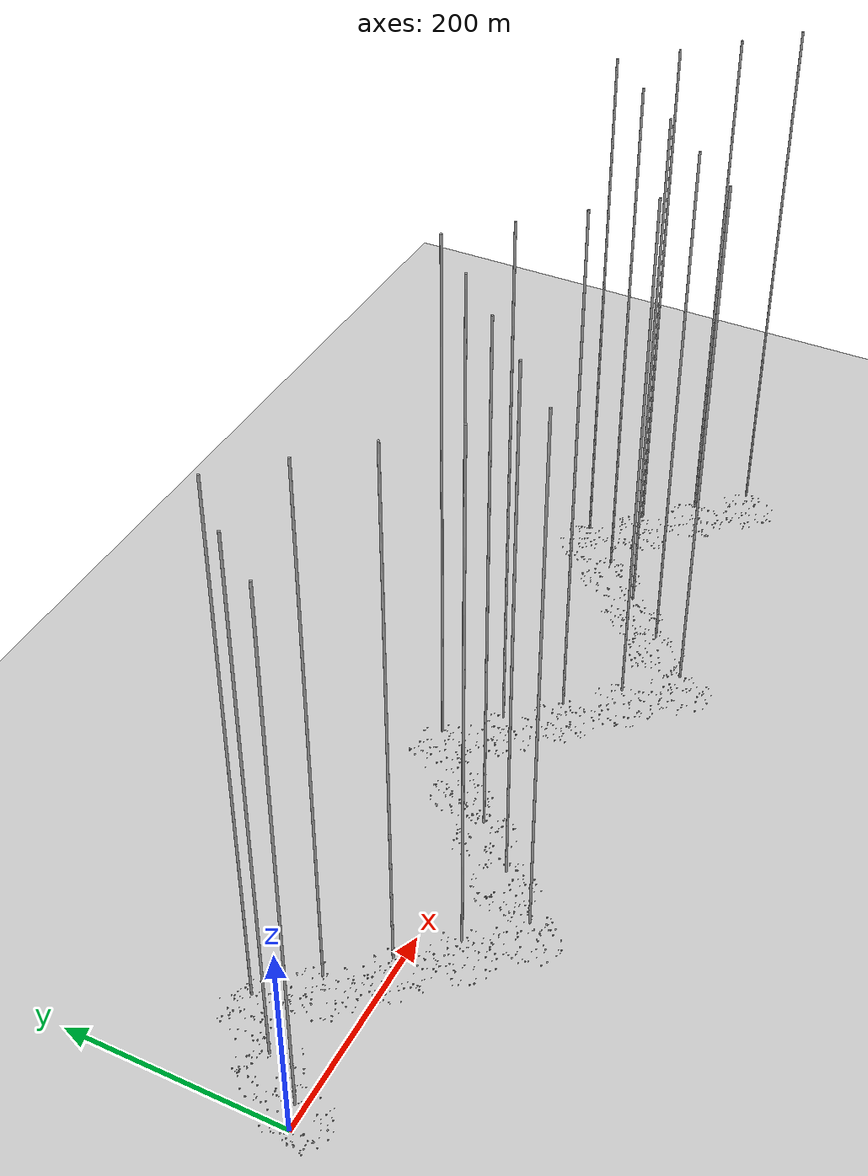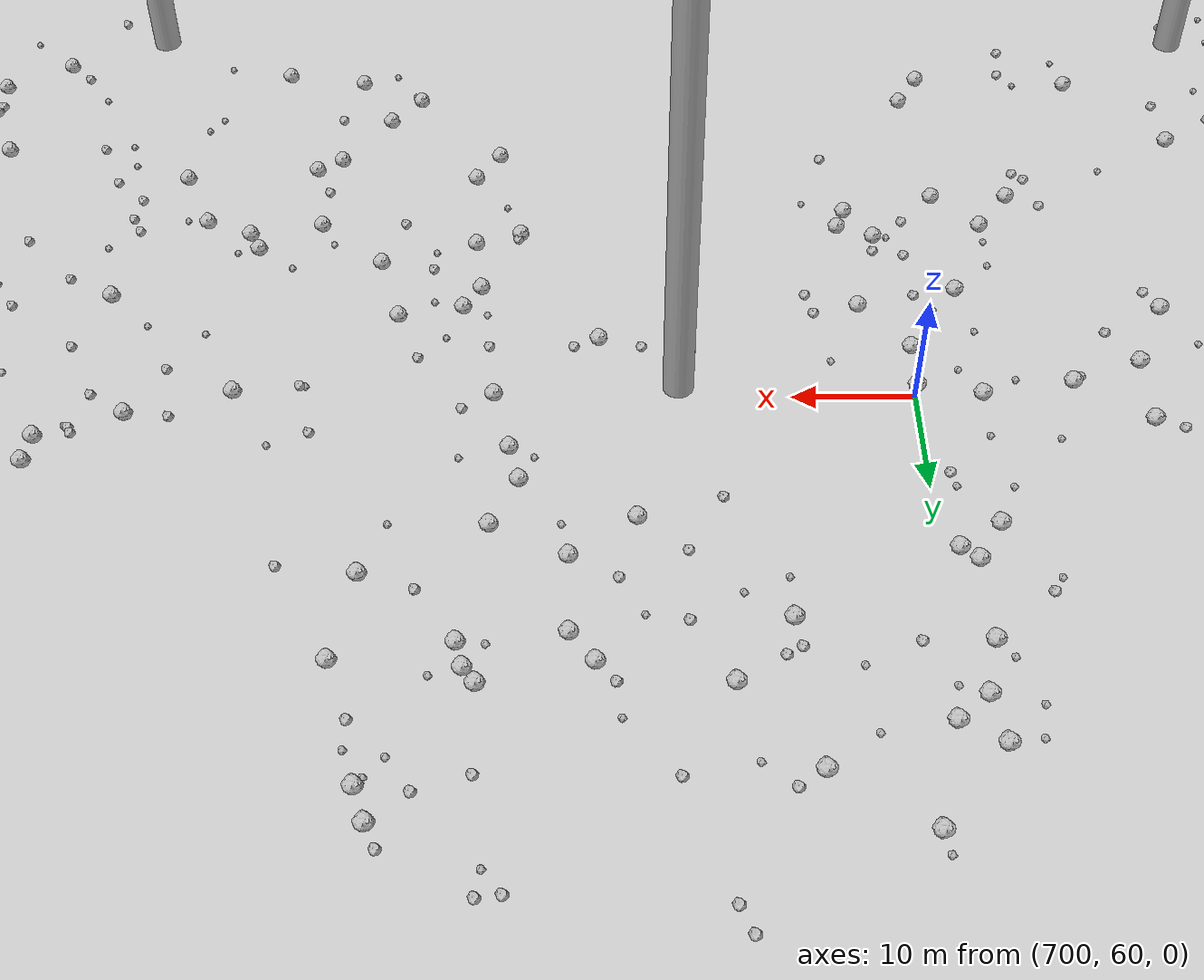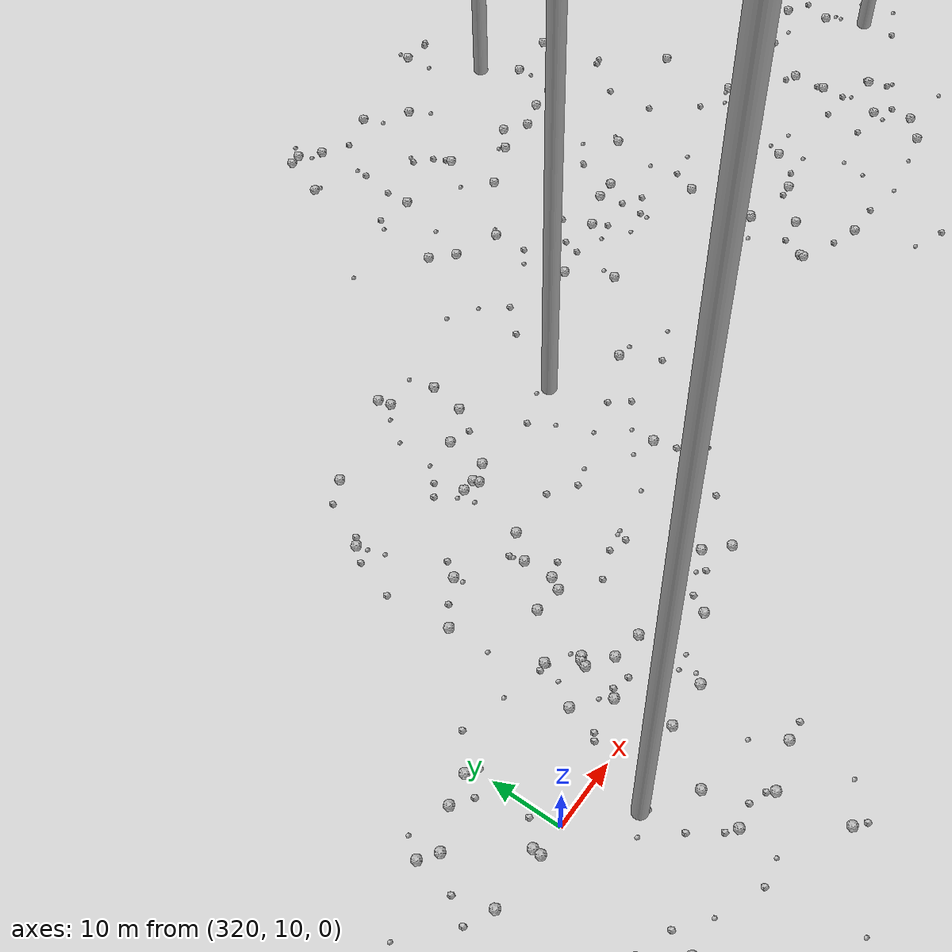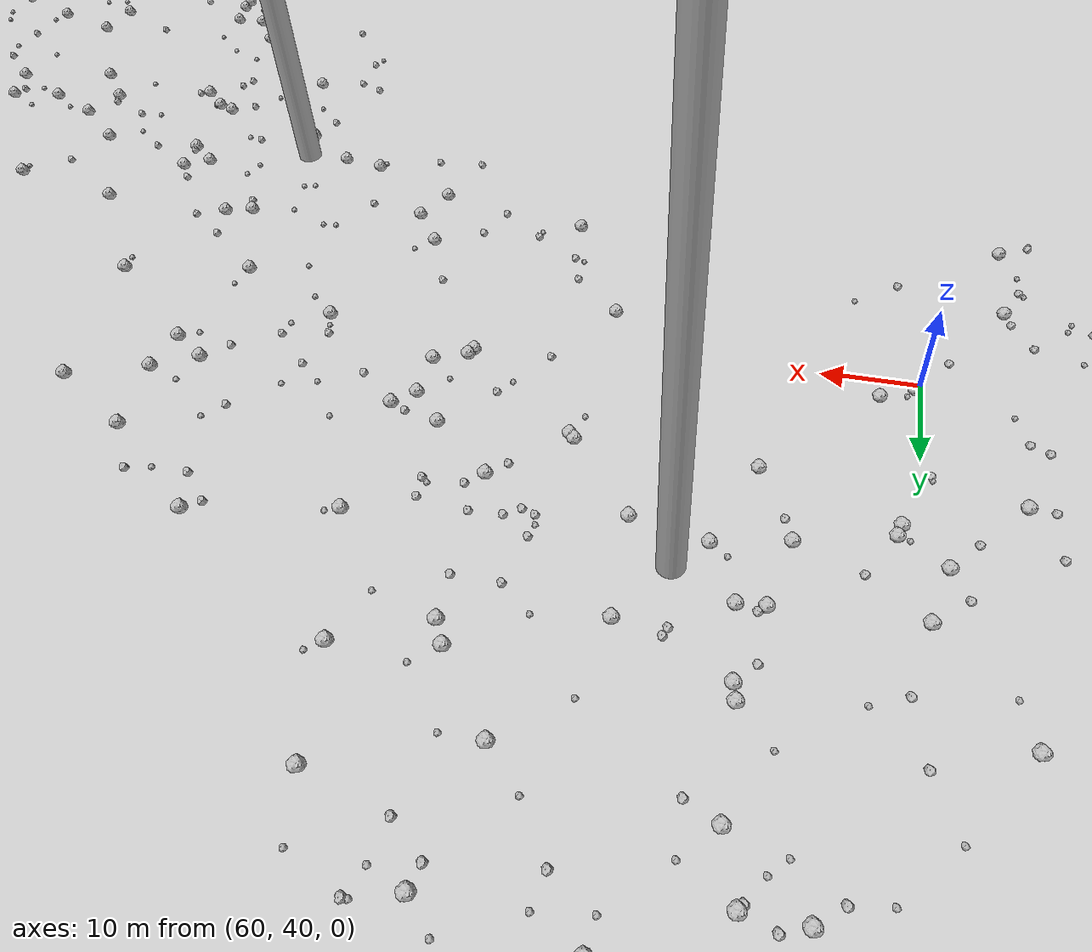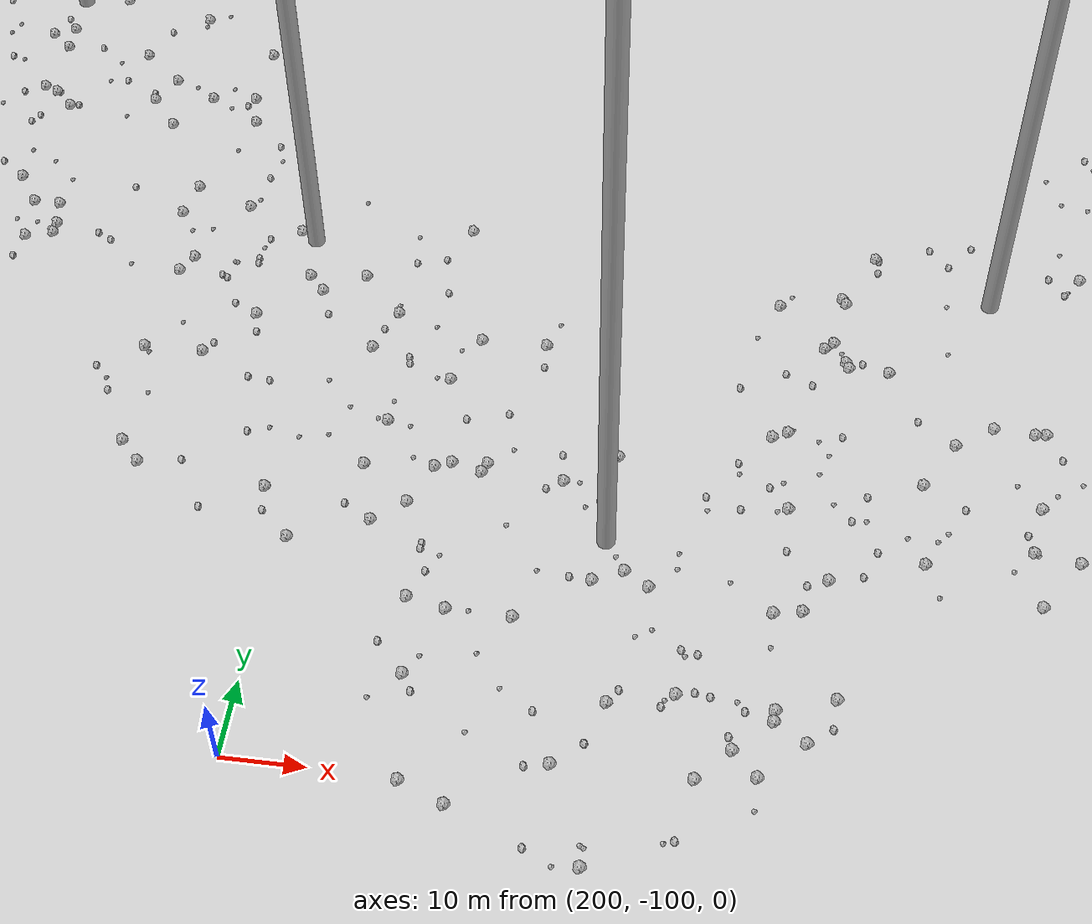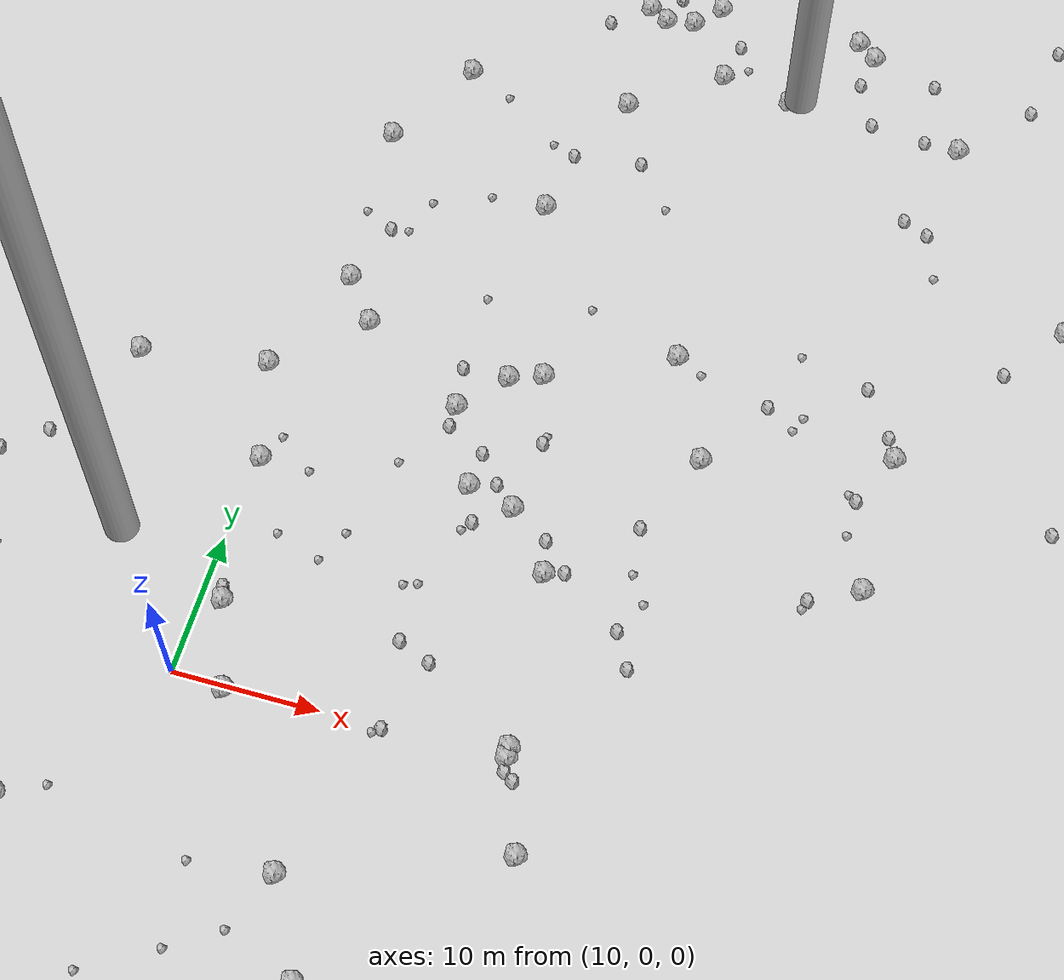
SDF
<sdf version="1.6">
 <world name="default">
  <include><uri>model://custom_ground</uri></include>
  <include><uri>model://sun</uri></include>
  <spherical_coordinates>
   <surface_model>EARTH_WGS84</surface_model>
   <latitude_deg>38.161479</latitude_deg>
   <longitude_deg>-122.454630</longitude_deg>
   <elevation>488.0</elevation>
   <heading_deg>90</heading_deg>
  </spherical_coordinates>
  <model name="rock1_0_0">
   <include><uri>model://rock1</uri><pose>13.650225989275278 -0.29930172950556155 0.5 0 0 0</pose></include>
  </model>
  <model name="rock1_0_1">
   <include><uri>model://rock1</uri><pose>6.470369877714106 -28.900130677339764 0.5 0 0 0</pose></include>
  </model>
  <model name="rock1_0_2">
   <include><uri>model://rock1</uri><pose>-6.051476671003007 21.98960825017882 0.5 0 0 0</pose></include>
  </model>
  <model name="rock1_0_3">
   <include><uri>model://rock1</uri><pose>1.4955313147005462 -10.707923523003139 0.5 0 0 0</pose></include>
  </model>
  <model name="rock1_0_4">
   <include><uri>model://rock1</uri><pose>14.025552593010815 28.62202430296899 0.5 0 0 0</pose></include>
  </model>
  <model name="rock1_0_5">
   <include><uri>model://rock1</uri><pose>-0.11234049763513099 -20.403298723354695 0.5 0 0 0</pose></include>
  </model>
  <model name="rock1_0_6">
   <include><uri>model://rock1</uri><pose>34.708040232423095 -5.846915377741627 0.5 0 0 0</pose></include>
  </model>
  <model name="rock1_0_7">
   <include><uri>model://rock1</uri><pose>2.384138095501207 -10.848121749738223 0.5 0 0 0</pose></include>
  </model>
  <model name="rock1_0_8">
   <include><uri>model://rock1</uri><pose>-10.769530515311272 -4.3188686333774235 0.5 0 0 0</pose></include>
  </model>
  <model name="rock1_0_9">
   <include><uri>model://rock1</uri><pose>-0.44071788945190704 22.142696653838613 0.5 0 0 0</pose></include>
  </model>
  <model name="rock1_0_10">
   <include><uri>model://rock1</uri><pose>22.256517643715185 -24.262866543432988 0.5 0 0 0</pose></include>
  </model>
  <model name="rock1_0_11">
   <include><uri>model://rock1</uri><pose>-9.742947296218086 -9.366962822070121 0.5 0 0 0</pose></include>
  </model>
  <model name="rock1_0_12">
   <include><uri>model://rock1</uri><pose>-3.4743447331686923 2.189372394943014 0.5 0 0 0</pose></include>
  </model>
  <model name="rock1_0_13">
   <include><uri>model://rock1</uri><pose>10.374239296926625 16.293325950683624 0.5 0 0 0</pose></include>
  </model>
  <model name="rock1_0_14">
   <include><uri>model://rock1</uri><pose>13.071100419773444 -24.562284802893195 0.5 0 0 0</pose></include>
  </model>
  <model name="rock1_0_15">
   <include><uri>model://rock1</uri><pose>-8.373188225046311 -16.680111939630002 0.5 0 0 0</pose></include>
  </model>
  <model name="rock1_0_16">
   <include><uri>model://rock1</uri><pose>24.13143797165131 -17.16184567884693 0.5 0 0 0</pose></include>
  </model>
  <model name="rock1_0_17">
   <include><uri>model://rock1</uri><pose>8.38158120607875 23.52682480736727 0.5 0 0 0</pose></include>
  </model>
  <model name="rock1_0_18">
   <include><uri>model://rock1</uri><pose>11.4785424422628 5.612082469860738 0.5 0 0 0</pose></include>
  </model>
  <model name="rock1_0_19">
   <include><uri>model://rock1</uri><pose>-4.6170047456006955 5.336666304115418 0.5 0 0 0</pose></include>
  </model>
  <model name="rock1_0_20">
   <include><uri>model://rock1</uri><pose>-13.443942399809446 -17.894186621624915 0.5 0 0 0</pose></include>
  </model>
  <model name="rock1_0_21">
   <include><uri>model://rock1</uri><pose>20.871020209037788 -11.008588797423013 0.5 0 0 0</pose></include>
  </model>
  <model name="rock1_0_22">
   <include><uri>model://rock1</uri><pose>-6.387882122399773 -1.1186908754700582 0.5 0 0 0</pose></include>
  </model>
  <model name="rock1_0_23">
   <include><uri>model://rock1</uri><pose>27.720332761892777 17.2699014581031 0.5 0 0 0</pose></include>
  </model>
  <model name="rock1_0_24">
   <include><uri>model://rock1</uri><pose>32.32307424697748 0.2212717875550041 0.5 0 0 0</pose></include>
  </model>
  <model name="rock1_0_25">
   <include><uri>model://rock1</uri><pose>32.29053552098189 0.8522179948327846 0.5 0 0 0</pose></include>
  </model>
  <model name="rock1_0_26">
   <include><uri>model://rock1</uri><pose>21.829298682119997 23.777914791164363 0.5 0 0 0</pose></include>
  </model>
  <model name="rock2_0_0">
   <include><uri>model://rock2</uri><pose>11.15725056519086 6.573646158386083 0.3 0 0 0</pose></include>
  </model>
  <model name="rock2_0_1">
   <include><uri>model://rock2</uri><pose>-3.222863522812599 -25.1655710220827 0.3 0 0 0</pose></include>
  </model>
  <model name="rock2_0_2">
   <include><uri>model://rock2</uri><pose>0.9783158574562236 -18.93700686355315 0.3 0 0 0</pose></include>
  </model>
  <model name="rock2_0_3">
   <include><uri>model://rock2</uri><pose>38.00971681282219 8.139461638219053 0.3 0 0 0</pose></include>
  </model>
  <model name="rock2_0_4">
   <include><uri>model://rock2</uri><pose>24.15222000325503 -0.08853542941266568 0.3 0 0 0</pose></include>
  </model>
  <model name="rock2_0_5">
   <include><uri>model://rock2</uri><pose>-10.47109525856207 -15.057918090574704 0.3 0 0 0</pose></include>
  </model>
  <model name="rock2_0_6">
   <include><uri>model://rock2</uri><pose>28.243783614300078 22.613781878632032 0.3 0 0 0</pose></include>
  </model>
  <model name="rock2_0_7">
   <include><uri>model://rock2</uri><pose>36.6998323081973 10.527822739566375 0.3 0 0 0</pose></include>
  </model>
  <model name="rock2_0_8">
   <include><uri>model://rock2</uri><pose>-6.702458598908255 9.691832003597426 0.3 0 0 0</pose></include>
  </model>
  <model name="rock2_0_9">
   <include><uri>model://rock2</uri><pose>32.43571590812177 -0.7322970435260174 0.3 0 0 0</pose></include>
  </model>
  <model name="rock2_0_10">
   <include><uri>model://rock2</uri><pose>25.697564200954133 5.054445118860322 0.3 0 0 0</pose></include>
  </model>
  <model name="rock2_0_11">
   <include><uri>model://rock2</uri><pose>26.18037392899447 18.727200074576174 0.3 0 0 0</pose></include>
  </model>
  <model name="rock2_0_12">
   <include><uri>model://rock2</uri><pose>-1.2503471601973573 -19.689552527334953 0.3 0 0 0</pose></include>
  </model>
  <model name="rock2_0_13">
   <include><uri>model://rock2</uri><pose>-8.532828960314083 -7.6289782098849805 0.3 0 0 0</pose></include>
  </model>
  <model name="rock2_0_14">
   <include><uri>model://rock2</uri><pose>23.436280552902097 6.015468812266036 0.3 0 0 0</pose></include>
  </model>
  <model name="rock2_0_15">
   <include><uri>model://rock2</uri><pose>32.311946615088885 13.636608952760142 0.3 0 0 0</pose></include>
  </model>
  <model name="rock2_0_16">
   <include><uri>model://rock2</uri><pose>0.31232989129467725 -9.233840314270775 0.3 0 0 0</pose></include>
  </model>
  <model name="rock2_0_17">
   <include><uri>model://rock2</uri><pose>-4.852559754392141 -16.28374734779837 0.3 0 0 0</pose></include>
  </model>
  <model name="rock2_0_18">
   <include><uri>model://rock2</uri><pose>30.48201620950713 15.57521886139319 0.3 0 0 0</pose></include>
  </model>
  <model name="rock2_0_19">
   <include><uri>model://rock2</uri><pose>-8.736168866903675 0.9776899936427199 0.3 0 0 0</pose></include>
  </model>
  <model name="rock2_0_20">
   <include><uri>model://rock2</uri><pose>21.358419325506247 26.839514266834108 0.3 0 0 0</pose></include>
  </model>
  <model name="rock2_0_21">
   <include><uri>model://rock2</uri><pose>-12.543234135138698 -15.619969791036201 0.3 0 0 0</pose></include>
  </model>
  <model name="rock2_0_22">
   <include><uri>model://rock2</uri><pose>24.56354880401007 20.747793100681157 0.3 0 0 0</pose></include>
  </model>
  <model name="rock2_0_23">
   <include><uri>model://rock2</uri><pose>-4.106004880353966 14.462857156208521 0.3 0 0 0</pose></include>
  </model>
  <model name="rock2_0_24">
   <include><uri>model://rock2</uri><pose>-6.80957345088639 12.2856267400808 0.3 0 0 0</pose></include>
  </model>
  <model name="rock2_0_25">
   <include><uri>model://rock2</uri><pose>33.10681632584372 -1.1975346319104716 0.3 0 0 0</pose></include>
  </model>
  <model name="rock2_0_26">
   <include><uri>model://rock2</uri><pose>-0.9646706073393432 -16.045129426712826 0.3 0 0 0</pose></include>
  </model>
  <model name="rock3_0_0">
   <include><uri>model://rock3</uri><pose>15.846105084855566 -17.302103248056017 0.2 0 0 0</pose></include>
  </model>
  <model name="rock3_0_1">
   <include><uri>model://rock3</uri><pose>13.365855963466672 -24.614964198928213 0.2 0 0 0</pose></include>
  </model>
  <model name="rock3_0_2">
   <include><uri>model://rock3</uri><pose>-0.9718041206249701 -3.645652307467774 0.2 0 0 0</pose></include>
  </model>
  <model name="rock3_0_3">
   <include><uri>model://rock3</uri><pose>4.81942082360257 -22.19877312199054 0.2 0 0 0</pose></include>
  </model>
  <model name="rock3_0_4">
   <include><uri>model://rock3</uri><pose>13.271844744510183 11.223396138383194 0.2 0 0 0</pose></include>
  </model>
  <model name="rock3_0_5">
   <include><uri>model://rock3</uri><pose>11.210654328867516 18.253583351971173 0.2 0 0 0</pose></include>
  </model>
  <model name="rock3_0_6">
   <include><uri>model://rock3</uri><pose>16.488252241089114 10.125997508964552 0.2 0 0 0</pose></include>
  </model>
  <model name="rock3_0_7">
   <include><uri>model://rock3</uri><pose>-6.85189503809756 -6.2919360396956066 0.2 0 0 0</pose></include>
  </model>
  <model name="rock3_0_8">
   <include><uri>model://rock3</uri><pose>22.370494133487348 9.936069347258218 0.2 0 0 0</pose></include>
  </model>
  <model name="rock3_0_9">
   <include><uri>model://rock3</uri><pose>-9.624029550051096 17.788567425545246 0.2 0 0 0</pose></include>
  </model>
  <model name="rock3_0_10">
   <include><uri>model://rock3</uri><pose>15.330598588793933 -11.684042572866463 0.2 0 0 0</pose></include>
  </model>
  <model name="rock3_0_11">
   <include><uri>model://rock3</uri><pose>31.819014413120414 -19.665189849653377 0.2 0 0 0</pose></include>
  </model>
  <model name="rock3_0_12">
   <include><uri>model://rock3</uri><pose>13.789902119356661 -28.875971101122758 0.2 0 0 0</pose></include>
  </model>
  <model name="rock3_0_13">
   <include><uri>model://rock3</uri><pose>28.24236455984662 -17.854655244785242 0.2 0 0 0</pose></include>
  </model>
  <model name="rock3_0_14">
   <include><uri>model://rock3</uri><pose>11.2295667136077 -20.031188516620844 0.2 0 0 0</pose></include>
  </model>
  <model name="rock3_0_15">
   <include><uri>model://rock3</uri><pose>-6.938550121847342 -5.337190982812604 0.2 0 0 0</pose></include>
  </model>
  <model name="rock3_0_16">
   <include><uri>model://rock3</uri><pose>23.62610807248668 -0.4985287624961998 0.2 0 0 0</pose></include>
  </model>
  <model name="rock3_0_17">
   <include><uri>model://rock3</uri><pose>19.103283188400468 -15.174085114153726 0.2 0 0 0</pose></include>
  </model>
  <model name="rock3_0_18">
   <include><uri>model://rock3</uri><pose>23.292619674444737 10.236052990018464 0.2 0 0 0</pose></include>
  </model>
  <model name="rock3_0_19">
   <include><uri>model://rock3</uri><pose>13.76579513182827 16.230964328443463 0.2 0 0 0</pose></include>
  </model>
  <model name="rock3_0_20">
   <include><uri>model://rock3</uri><pose>17.17244121625162 -22.322497369798093 0.2 0 0 0</pose></include>
  </model>
  <model name="rock3_0_21">
   <include><uri>model://rock3</uri><pose>19.327692437877175 18.565308032306397 0.2 0 0 0</pose></include>
  </model>
  <model name="rock3_0_22">
   <include><uri>model://rock3</uri><pose>17.627036643748497 12.483868494641264 0.2 0 0 0</pose></include>
  </model>
  <model name="rock3_0_23">
   <include><uri>model://rock3</uri><pose>5.294458865001623 -9.451165312153865 0.2 0 0 0</pose></include>
  </model>
  <model name="rock3_0_24">
   <include><uri>model://rock3</uri><pose>-9.34123579420293 -2.8743140724160163 0.2 0 0 0</pose></include>
  </model>
  <model name="rock3_0_25">
   <include><uri>model://rock3</uri><pose>1.6611255569897097 9.966191914198191 0.2 0 0 0</pose></include>
  </model>
  <model name="rock3_0_26">
   <include><uri>model://rock3</uri><pose>24.17597128430272 -22.030313968829006 0.2 0 0 0</pose></include>
  </model>
  <model name="rock1_1_0">
   <include><uri>model://rock1</uri><pose>29.20020667846905 60.599060210981335 0.5 0 0 0</pose></include>
  </model>
  <model name="rock1_1_1">
   <include><uri>model://rock1</uri><pose>25.715033608373293 61.11839405383981 0.5 0 0 0</pose></include>
  </model>
  <model name="rock1_1_2">
   <include><uri>model://rock1</uri><pose>14.54438474874343 51.641696780077346 0.5 0 0 0</pose></include>
  </model>
  <model name="rock1_1_3">
   <include><uri>model://rock1</uri><pose>26.86985507408274 27.729553776766927 0.5 0 0 0</pose></include>
  </model>
  <model name="rock1_1_4">
   <include><uri>model://rock1</uri><pose>61.77080020825423 58.30016915318922 0.5 0 0 0</pose></include>
  </model>
  <model name="rock1_1_5">
   <include><uri>model://rock1</uri><pose>23.106962350737213 41.3690379170517 0.5 0 0 0</pose></include>
  </model>
  <model name="rock1_1_6">
   <include><uri>model://rock1</uri><pose>51.29336139035689 27.927589968072247 0.5 0 0 0</pose></include>
  </model>
  <model name="rock1_1_7">
   <include><uri>model://rock1</uri><pose>35.311166788954495 31.72671198327293 0.5 0 0 0</pose></include>
  </model>
  <model name="rock1_1_8">
   <include><uri>model://rock1</uri><pose>27.155705980394966 60.2976200406338 0.5 0 0 0</pose></include>
  </model>
  <model name="rock1_1_9">
   <include><uri>model://rock1</uri><pose>38.808149093578386 24.27930497754988 0.5 0 0 0</pose></include>
  </model>
  <model name="rock1_1_10">
   <include><uri>model://rock1</uri><pose>62.14771616228296 59.58528887144457 0.5 0 0 0</pose></include>
  </model>
  <model name="rock1_1_11">
   <include><uri>model://rock1</uri><pose>31.03876038785011 13.189800858664793 0.5 0 0 0</pose></include>
  </model>
  <model name="rock1_1_12">
   <include><uri>model://rock1</uri><pose>26.396362879429297 51.818452401451694 0.5 0 0 0</pose></include>
  </model>
  <model name="rock1_1_13">
   <include><uri>model://rock1</uri><pose>24.430279649811226 18.121583181609317 0.5 0 0 0</pose></include>
  </model>
  <model name="rock1_1_14">
   <include><uri>model://rock1</uri><pose>37.68477650276756 55.257852332614874 0.5 0 0 0</pose></include>
  </model>
  <model name="rock1_1_15">
   <include><uri>model://rock1</uri><pose>64.04635642512056 42.538785300739995 0.5 0 0 0</pose></include>
  </model>
  <model name="rock1_1_16">
   <include><uri>model://rock1</uri><pose>27.043034672773032 66.36073023919047 0.5 0 0 0</pose></include>
  </model>
  <model name="rock1_1_17">
   <include><uri>model://rock1</uri><pose>42.908283379019664 61.01534959349323 0.5 0 0 0</pose></include>
  </model>
  <model name="rock1_1_18">
   <include><uri>model://rock1</uri><pose>32.546803149065276 56.319079838732804 0.5 0 0 0</pose></include>
  </model>
  <model name="rock1_1_19">
   <include><uri>model://rock1</uri><pose>41.50602038605127 62.127599289525406 0.5 0 0 0</pose></include>
  </model>
  <model name="rock1_1_20">
   <include><uri>model://rock1</uri><pose>50.490622055347025 54.37612529167972 0.5 0 0 0</pose></include>
  </model>
  <model name="rock1_1_21">
   <include><uri>model://rock1</uri><pose>51.30258650266187 17.71669150898473 0.5 0 0 0</pose></include>
  </model>
  <model name="rock1_1_22">
   <include><uri>model://rock1</uri><pose>11.60314040439081 31.808879040678057 0.5 0 0 0</pose></include>
  </model>
  <model name="rock1_1_23">
   <include><uri>model://rock1</uri><pose>24.591349232060622 26.897018916332193 0.5 0 0 0</pose></include>
  </model>
  <model name="rock1_1_24">
   <include><uri>model://rock1</uri><pose>30.886639392971308 62.50042580083389 0.5 0 0 0</pose></include>
  </model>
  <model name="rock1_1_25">
   <include><uri>model://rock1</uri><pose>60.60966067225563 40.960929037851 0.5 0 0 0</pose></include>
  </model>
  <model name="rock1_1_26">
   <include><uri>model://rock1</uri><pose>10.62857260845317 44.50578416707755 0.5 0 0 0</pose></include>
  </model>
  <model name="rock2_1_0">
   <include><uri>model://rock2</uri><pose>62.43952744205236 25.205823292052635 0.3 0 0 0</pose></include>
  </model>
  <model name="rock2_1_1">
   <include><uri>model://rock2</uri><pose>47.990102944878764 16.09085082959144 0.3 0 0 0</pose></include>
  </model>
  <model name="rock2_1_2">
   <include><uri>model://rock2</uri><pose>59.12231166174308 51.99892993571397 0.3 0 0 0</pose></include>
  </model>
  <model name="rock2_1_3">
   <include><uri>model://rock2</uri><pose>57.13503764109184 36.53242013104972 0.3 0 0 0</pose></include>
  </model>
  <model name="rock2_1_4">
   <include><uri>model://rock2</uri><pose>33.07846059343944 59.389413927426055 0.3 0 0 0</pose></include>
  </model>
  <model name="rock2_1_5">
   <include><uri>model://rock2</uri><pose>37.23599748697215 69.22294664650585 0.3 0 0 0</pose></include>
  </model>
  <model name="rock2_1_6">
   <include><uri>model://rock2</uri><pose>36.21714730047883 18.213297560666774 0.3 0 0 0</pose></include>
  </model>
  <model name="rock2_1_7">
   <include><uri>model://rock2</uri><pose>13.058075125689971 36.51689922719967 0.3 0 0 0</pose></include>
  </model>
  <model name="rock2_1_8">
   <include><uri>model://rock2</uri><pose>27.719988381454534 62.702610150710754 0.3 0 0 0</pose></include>
  </model>
  <model name="rock2_1_9">
   <include><uri>model://rock2</uri><pose>49.76434194283843 46.49359181622338 0.3 0 0 0</pose></include>
  </model>
  <model name="rock2_1_10">
   <include><uri>model://rock2</uri><pose>47.6961225320823 59.68426066234282 0.3 0 0 0</pose></include>
  </model>
  <model name="rock2_1_11">
   <include><uri>model://rock2</uri><pose>23.827917676917252 46.32270685622695 0.3 0 0 0</pose></include>
  </model>
  <model name="rock2_1_12">
   <include><uri>model://rock2</uri><pose>42.179553442163694 29.58226394582786 0.3 0 0 0</pose></include>
  </model>
  <model name="rock2_1_13">
   <include><uri>model://rock2</uri><pose>43.96115683204582 54.985839187107985 0.3 0 0 0</pose></include>
  </model>
  <model name="rock2_1_14">
   <include><uri>model://rock2</uri><pose>21.801918931539753 22.199566029653862 0.3 0 0 0</pose></include>
  </model>
  <model name="rock2_1_15">
   <include><uri>model://rock2</uri><pose>23.139936132349057 59.02166758903567 0.3 0 0 0</pose></include>
  </model>
  <model name="rock2_1_16">
   <include><uri>model://rock2</uri><pose>54.94253301118906 59.27217336053474 0.3 0 0 0</pose></include>
  </model>
  <model name="rock2_1_17">
   <include><uri>model://rock2</uri><pose>42.41104554787016 58.37228751881456 0.3 0 0 0</pose></include>
  </model>
  <model name="rock2_1_18">
   <include><uri>model://rock2</uri><pose>27.786909838162057 62.66538453046404 0.3 0 0 0</pose></include>
  </model>
  <model name="rock2_1_19">
   <include><uri>model://rock2</uri><pose>47.95974871533952 47.29511389400143 0.3 0 0 0</pose></include>
  </model>
  <model name="rock2_1_20">
   <include><uri>model://rock2</uri><pose>28.687227234163174 46.9272716791619 0.3 0 0 0</pose></include>
  </model>
  <model name="rock2_1_21">
   <include><uri>model://rock2</uri><pose>47.97362618898224 54.50059097986437 0.3 0 0 0</pose></include>
  </model>
  <model name="rock2_1_22">
   <include><uri>model://rock2</uri><pose>25.397525242162466 15.562739530497387 0.3 0 0 0</pose></include>
  </model>
  <model name="rock2_1_23">
   <include><uri>model://rock2</uri><pose>55.93917710082893 65.34015079226045 0.3 0 0 0</pose></include>
  </model>
  <model name="rock2_1_24">
   <include><uri>model://rock2</uri><pose>48.43106255736456 32.8522572524205 0.3 0 0 0</pose></include>
  </model>
  <model name="rock2_1_25">
   <include><uri>model://rock2</uri><pose>49.481471919773064 24.134367815888147 0.3 0 0 0</pose></include>
  </model>
  <model name="rock2_1_26">
   <include><uri>model://rock2</uri><pose>50.57958434102298 29.489452528976823 0.3 0 0 0</pose></include>
  </model>
  <model name="rock3_1_0">
   <include><uri>model://rock3</uri><pose>43.506449621866196 34.13155660869996 0.2 0 0 0</pose></include>
  </model>
  <model name="rock3_1_1">
   <include><uri>model://rock3</uri><pose>34.1101742427192 57.41757080123537 0.2 0 0 0</pose></include>
  </model>
  <model name="rock3_1_2">
   <include><uri>model://rock3</uri><pose>58.92471608863441 52.439618931842 0.2 0 0 0</pose></include>
  </model>
  <model name="rock3_1_3">
   <include><uri>model://rock3</uri><pose>14.273366049920178 36.70562547914247 0.2 0 0 0</pose></include>
  </model>
  <model name="rock3_1_4">
   <include><uri>model://rock3</uri><pose>49.42883899044545 21.441617060087204 0.2 0 0 0</pose></include>
  </model>
  <model name="rock3_1_5">
   <include><uri>model://rock3</uri><pose>17.80115617452072 50.09042555133229 0.2 0 0 0</pose></include>
  </model>
  <model name="rock3_1_6">
   <include><uri>model://rock3</uri><pose>44.67632751543435 29.39159809194468 0.2 0 0 0</pose></include>
  </model>
  <model name="rock3_1_7">
   <include><uri>model://rock3</uri><pose>47.765267512289654 15.36920135574767 0.2 0 0 0</pose></include>
  </model>
  <model name="rock3_1_8">
   <include><uri>model://rock3</uri><pose>25.77560107417711 63.04464394507603 0.2 0 0 0</pose></include>
  </model>
  <model name="rock3_1_9">
   <include><uri>model://rock3</uri><pose>19.128877507806713 41.18304596015864 0.2 0 0 0</pose></include>
  </model>
  <model name="rock3_1_10">
   <include><uri>model://rock3</uri><pose>21.313815222071547 32.73169388941577 0.2 0 0 0</pose></include>
  </model>
  <model name="rock3_1_11">
   <include><uri>model://rock3</uri><pose>24.840513131420494 14.828288802189837 0.2 0 0 0</pose></include>
  </model>
  <model name="rock3_1_12">
   <include><uri>model://rock3</uri><pose>50.93074113890063 43.00186098738033 0.2 0 0 0</pose></include>
  </model>
  <model name="rock3_1_13">
   <include><uri>model://rock3</uri><pose>48.909145291156506 24.47483702909075 0.2 0 0 0</pose></include>
  </model>
  <model name="rock3_1_14">
   <include><uri>model://rock3</uri><pose>44.190098722934245 28.23645350636528 0.2 0 0 0</pose></include>
  </model>
  <model name="rock3_1_15">
   <include><uri>model://rock3</uri><pose>37.829440484020395 12.834278922130625 0.2 0 0 0</pose></include>
  </model>
  <model name="rock3_1_16">
   <include><uri>model://rock3</uri><pose>61.28817362593569 41.83523803239099 0.2 0 0 0</pose></include>
  </model>
  <model name="rock3_1_17">
   <include><uri>model://rock3</uri><pose>66.91943726968675 28.323812356030604 0.2 0 0 0</pose></include>
  </model>
  <model name="rock3_1_18">
   <include><uri>model://rock3</uri><pose>28.581489478816778 33.8747128142503 0.2 0 0 0</pose></include>
  </model>
  <model name="rock3_1_19">
   <include><uri>model://rock3</uri><pose>10.898204388092072 37.554572493496885 0.2 0 0 0</pose></include>
  </model>
  <model name="rock3_1_20">
   <include><uri>model://rock3</uri><pose>60.941012885123776 59.784903478896226 0.2 0 0 0</pose></include>
  </model>
  <model name="rock3_1_21">
   <include><uri>model://rock3</uri><pose>31.345671332615154 43.52242928603406 0.2 0 0 0</pose></include>
  </model>
  <model name="rock3_1_22">
   <include><uri>model://rock3</uri><pose>22.09395498768268 46.89536370888274 0.2 0 0 0</pose></include>
  </model>
  <model name="rock3_1_23">
   <include><uri>model://rock3</uri><pose>37.18442102287862 30.782431319858865 0.2 0 0 0</pose></include>
  </model>
  <model name="rock3_1_24">
   <include><uri>model://rock3</uri><pose>36.60916345695381 14.768463214747353 0.2 0 0 0</pose></include>
  </model>
  <model name="rock3_1_25">
   <include><uri>model://rock3</uri><pose>15.202045772279627 39.52273043774175 0.2 0 0 0</pose></include>
  </model>
  <model name="rock3_1_26">
   <include><uri>model://rock3</uri><pose>28.369222158271356 23.192459133194816 0.2 0 0 0</pose></include>
  </model>
  <model name="rock1_2_0">
   <include><uri>model://rock1</uri><pose>98.69835988984596 77.28882615964935 0.5 0 0 0</pose></include>
  </model>
  <model name="rock1_2_1">
   <include><uri>model://rock1</uri><pose>85.9687129505505 61.541036974145634 0.5 0 0 0</pose></include>
  </model>
  <model name="rock1_2_2">
   <include><uri>model://rock1</uri><pose>75.50557991624626 69.09240441961873 0.5 0 0 0</pose></include>
  </model>
  <model name="rock1_2_3">
   <include><uri>model://rock1</uri><pose>85.37033893248068 100.15710019621353 0.5 0 0 0</pose></include>
  </model>
  <model name="rock1_2_4">
   <include><uri>model://rock1</uri><pose>74.44967013791218 88.13465358247838 0.5 0 0 0</pose></include>
  </model>
  <model name="rock1_2_5">
   <include><uri>model://rock1</uri><pose>108.28476608179209 78.54827181466928 0.5 0 0 0</pose></include>
  </model>
  <model name="rock1_2_6">
   <include><uri>model://rock1</uri><pose>82.49862020925337 98.7094796021825 0.5 0 0 0</pose></include>
  </model>
  <model name="rock1_2_7">
   <include><uri>model://rock1</uri><pose>71.25706772308553 61.779167924623124 0.5 0 0 0</pose></include>
  </model>
  <model name="rock1_2_8">
   <include><uri>model://rock1</uri><pose>74.87837481025592 76.49144240698931 0.5 0 0 0</pose></include>
  </model>
  <model name="rock1_2_9">
   <include><uri>model://rock1</uri><pose>74.98162873645498 53.828627236059866 0.5 0 0 0</pose></include>
  </model>
  <model name="rock1_2_10">
   <include><uri>model://rock1</uri><pose>78.44289187076555 63.170957892172936 0.5 0 0 0</pose></include>
  </model>
  <model name="rock1_2_11">
   <include><uri>model://rock1</uri><pose>57.65708232135803 62.34001525800411 0.5 0 0 0</pose></include>
  </model>
  <model name="rock1_2_12">
   <include><uri>model://rock1</uri><pose>85.5504033526165 72.27491552680911 0.5 0 0 0</pose></include>
  </model>
  <model name="rock1_2_13">
   <include><uri>model://rock1</uri><pose>72.6965766480984 93.89997616824667 0.5 0 0 0</pose></include>
  </model>
  <model name="rock1_2_14">
   <include><uri>model://rock1</uri><pose>59.257858699362146 68.17086907692422 0.5 0 0 0</pose></include>
  </model>
  <model name="rock1_2_15">
   <include><uri>model://rock1</uri><pose>99.89348647451189 74.97236436025187 0.5 0 0 0</pose></include>
  </model>
  <model name="rock1_2_16">
   <include><uri>model://rock1</uri><pose>92.74067136278705 53.293229988398494 0.5 0 0 0</pose></include>
  </model>
  <model name="rock1_2_17">
   <include><uri>model://rock1</uri><pose>106.51162316520288 89.19362115844015 0.5 0 0 0</pose></include>
  </model>
  <model name="rock1_2_18">
   <include><uri>model://rock1</uri><pose>64.31514364429196 98.51891074783194 0.5 0 0 0</pose></include>
  </model>
  <model name="rock1_2_19">
   <include><uri>model://rock1</uri><pose>72.6464711934282 98.59098522412457 0.5 0 0 0</pose></include>
  </model>
  <model name="rock1_2_20">
   <include><uri>model://rock1</uri><pose>95.50901483268528 96.7015574076465 0.5 0 0 0</pose></include>
  </model>
  <model name="rock1_2_21">
   <include><uri>model://rock1</uri><pose>74.50399388510631 78.11439846286807 0.5 0 0 0</pose></include>
  </model>
  <model name="rock1_2_22">
   <include><uri>model://rock1</uri><pose>67.50086626882 94.05158423855326 0.5 0 0 0</pose></include>
  </model>
  <model name="rock1_2_23">
   <include><uri>model://rock1</uri><pose>92.98277441363582 84.80605365225449 0.5 0 0 0</pose></include>
  </model>
  <model name="rock1_2_24">
   <include><uri>model://rock1</uri><pose>51.19968914072981 78.36706048772373 0.5 0 0 0</pose></include>
  </model>
  <model name="rock1_2_25">
   <include><uri>model://rock1</uri><pose>59.74660029264957 97.2682681385204 0.5 0 0 0</pose></include>
  </model>
  <model name="rock1_2_26">
   <include><uri>model://rock1</uri><pose>72.87533444483238 68.88761246024174 0.5 0 0 0</pose></include>
  </model>
  <model name="rock2_2_0">
   <include><uri>model://rock2</uri><pose>73.08298718675181 74.49138445435167 0.3 0 0 0</pose></include>
  </model>
  <model name="rock2_2_1">
   <include><uri>model://rock2</uri><pose>86.18392146635877 93.39785833408772 0.3 0 0 0</pose></include>
  </model>
  <model name="rock2_2_2">
   <include><uri>model://rock2</uri><pose>78.02732935892845 108.99050315563264 0.3 0 0 0</pose></include>
  </model>
  <model name="rock2_2_3">
   <include><uri>model://rock2</uri><pose>95.61996642842877 62.39142066416122 0.3 0 0 0</pose></include>
  </model>
  <model name="rock2_2_4">
   <include><uri>model://rock2</uri><pose>60.884406362334154 75.24349198981108 0.3 0 0 0</pose></include>
  </model>
  <model name="rock2_2_5">
   <include><uri>model://rock2</uri><pose>81.07484791479709 73.23261027476374 0.3 0 0 0</pose></include>
  </model>
  <model name="rock2_2_6">
   <include><uri>model://rock2</uri><pose>65.20844221904707 92.16096562504228 0.3 0 0 0</pose></include>
  </model>
  <model name="rock2_2_7">
   <include><uri>model://rock2</uri><pose>69.73841841610428 94.8279501070544 0.3 0 0 0</pose></include>
  </model>
  <model name="rock2_2_8">
   <include><uri>model://rock2</uri><pose>64.8180607825521 64.19648808599852 0.3 0 0 0</pose></include>
  </model>
  <model name="rock2_2_9">
   <include><uri>model://rock2</uri><pose>84.64198884915498 102.71243449746365 0.3 0 0 0</pose></include>
  </model>
  <model name="rock2_2_10">
   <include><uri>model://rock2</uri><pose>95.41748443529283 70.50395048128168 0.3 0 0 0</pose></include>
  </model>
  <model name="rock2_2_11">
   <include><uri>model://rock2</uri><pose>100.01509772600515 70.40547675900625 0.3 0 0 0</pose></include>
  </model>
  <model name="rock2_2_12">
   <include><uri>model://rock2</uri><pose>72.28489244234797 93.32680076198596 0.3 0 0 0</pose></include>
  </model>
  <model name="rock2_2_13">
   <include><uri>model://rock2</uri><pose>77.49725846227442 86.56920655696175 0.3 0 0 0</pose></include>
  </model>
  <model name="rock2_2_14">
   <include><uri>model://rock2</uri><pose>97.14860613447216 63.32217753611691 0.3 0 0 0</pose></include>
  </model>
  <model name="rock2_2_15">
   <include><uri>model://rock2</uri><pose>94.37396089429623 65.32236226145048 0.3 0 0 0</pose></include>
  </model>
  <model name="rock2_2_16">
   <include><uri>model://rock2</uri><pose>95.03178897333565 94.49961672188104 0.3 0 0 0</pose></include>
  </model>
  <model name="rock2_2_17">
   <include><uri>model://rock2</uri><pose>80.7625328819152 72.36663065560563 0.3 0 0 0</pose></include>
  </model>
  <model name="rock2_2_18">
   <include><uri>model://rock2</uri><pose>73.56953435468716 69.49701122273979 0.3 0 0 0</pose></include>
  </model>
  <model name="rock2_2_19">
   <include><uri>model://rock2</uri><pose>98.13129130907012 57.38204709074333 0.3 0 0 0</pose></include>
  </model>
  <model name="rock2_2_20">
   <include><uri>model://rock2</uri><pose>100.35881222502769 63.45477273201901 0.3 0 0 0</pose></include>
  </model>
  <model name="rock2_2_21">
   <include><uri>model://rock2</uri><pose>72.08409255715333 59.35267847958698 0.3 0 0 0</pose></include>
  </model>
  <model name="rock2_2_22">
   <include><uri>model://rock2</uri><pose>59.52499067186092 81.17567900421184 0.3 0 0 0</pose></include>
  </model>
  <model name="rock2_2_23">
   <include><uri>model://rock2</uri><pose>98.2805531724867 91.67771564855981 0.3 0 0 0</pose></include>
  </model>
  <model name="rock2_2_24">
   <include><uri>model://rock2</uri><pose>90.02082836010604 100.28740449152002 0.3 0 0 0</pose></include>
  </model>
  <model name="rock2_2_25">
   <include><uri>model://rock2</uri><pose>99.87153543152206 97.7916692190696 0.3 0 0 0</pose></include>
  </model>
  <model name="rock2_2_26">
   <include><uri>model://rock2</uri><pose>94.28590542346461 62.86288040908829 0.3 0 0 0</pose></include>
  </model>
  <model name="rock3_2_0">
   <include><uri>model://rock3</uri><pose>89.39812517138381 88.45262342140984 0.2 0 0 0</pose></include>
  </model>
  <model name="rock3_2_1">
   <include><uri>model://rock3</uri><pose>99.36789553755668 97.75633228798995 0.2 0 0 0</pose></include>
  </model>
  <model name="rock3_2_2">
   <include><uri>model://rock3</uri><pose>52.47404402010525 73.96383408581524 0.2 0 0 0</pose></include>
  </model>
  <model name="rock3_2_3">
   <include><uri>model://rock3</uri><pose>98.82780090218291 95.28169505448236 0.2 0 0 0</pose></include>
  </model>
  <model name="rock3_2_4">
   <include><uri>model://rock3</uri><pose>86.98366174527767 79.96248893449737 0.2 0 0 0</pose></include>
  </model>
  <model name="rock3_2_5">
   <include><uri>model://rock3</uri><pose>106.107764961106 73.1118593412144 0.2 0 0 0</pose></include>
  </model>
  <model name="rock3_2_6">
   <include><uri>model://rock3</uri><pose>92.99253838748996 99.276470683669 0.2 0 0 0</pose></include>
  </model>
  <model name="rock3_2_7">
   <include><uri>model://rock3</uri><pose>92.3109954152226 73.04543016399778 0.2 0 0 0</pose></include>
  </model>
  <model name="rock3_2_8">
   <include><uri>model://rock3</uri><pose>86.73414187811855 96.35222052398645 0.2 0 0 0</pose></include>
  </model>
  <model name="rock3_2_9">
   <include><uri>model://rock3</uri><pose>109.69743129128452 79.5981352652417 0.2 0 0 0</pose></include>
  </model>
  <model name="rock3_2_10">
   <include><uri>model://rock3</uri><pose>71.1211544510012 81.60322036816997 0.2 0 0 0</pose></include>
  </model>
  <model name="rock3_2_11">
   <include><uri>model://rock3</uri><pose>60.90036303302364 100.99101193385673 0.2 0 0 0</pose></include>
  </model>
  <model name="rock3_2_12">
   <include><uri>model://rock3</uri><pose>69.32650022942254 89.55962818651227 0.2 0 0 0</pose></include>
  </model>
  <model name="rock3_2_13">
   <include><uri>model://rock3</uri><pose>62.79851706876423 95.35557885440102 0.2 0 0 0</pose></include>
  </model>
  <model name="rock3_2_14">
   <include><uri>model://rock3</uri><pose>82.14307407513525 95.75555476109338 0.2 0 0 0</pose></include>
  </model>
  <model name="rock3_2_15">
   <include><uri>model://rock3</uri><pose>57.01839735540537 86.44149613092361 0.2 0 0 0</pose></include>
  </model>
  <model name="rock3_2_16">
   <include><uri>model://rock3</uri><pose>61.841825165443815 91.61729410810707 0.2 0 0 0</pose></include>
  </model>
  <model name="rock3_2_17">
   <include><uri>model://rock3</uri><pose>64.15684732914083 76.55997531724765 0.2 0 0 0</pose></include>
  </model>
  <model name="rock3_2_18">
   <include><uri>model://rock3</uri><pose>105.13274211381933 95.17247280311597 0.2 0 0 0</pose></include>
  </model>
  <model name="rock3_2_19">
   <include><uri>model://rock3</uri><pose>74.41693025431145 108.07034793225841 0.2 0 0 0</pose></include>
  </model>
  <model name="rock3_2_20">
   <include><uri>model://rock3</uri><pose>94.01902581056316 63.87493566270014 0.2 0 0 0</pose></include>
  </model>
  <model name="rock3_2_21">
   <include><uri>model://rock3</uri><pose>69.95531286654736 101.5571576440417 0.2 0 0 0</pose></include>
  </model>
  <model name="rock3_2_22">
   <include><uri>model://rock3</uri><pose>77.31210623619185 91.07351086986534 0.2 0 0 0</pose></include>
  </model>
  <model name="rock3_2_23">
   <include><uri>model://rock3</uri><pose>96.82705194061126 84.68678765791053 0.2 0 0 0</pose></include>
  </model>
  <model name="rock3_2_24">
   <include><uri>model://rock3</uri><pose>70.80227002531382 91.04013996315223 0.2 0 0 0</pose></include>
  </model>
  <model name="rock3_2_25">
   <include><uri>model://rock3</uri><pose>101.02309300008054 79.2051977807644 0.2 0 0 0</pose></include>
  </model>
  <model name="rock3_2_26">
   <include><uri>model://rock3</uri><pose>76.66201777346416 64.30586548856505 0.2 0 0 0</pose></include>
  </model>
  <model name="rock1_3_0">
   <include><uri>model://rock1</uri><pose>122.00765317461844 40.41955738855056 0.5 0 0 0</pose></include>
  </model>
  <model name="rock1_3_1">
   <include><uri>model://rock1</uri><pose>115.5964414281077 17.80719170994047 0.5 0 0 0</pose></include>
  </model>
  <model name="rock1_3_2">
   <include><uri>model://rock1</uri><pose>111.82643358872627 65.23520783099241 0.5 0 0 0</pose></include>
  </model>
  <model name="rock1_3_3">
   <include><uri>model://rock1</uri><pose>117.7643611327699 21.91780199137039 0.5 0 0 0</pose></include>
  </model>
  <model name="rock1_3_4">
   <include><uri>model://rock1</uri><pose>92.04746428561901 34.780767146635206 0.5 0 0 0</pose></include>
  </model>
  <model name="rock1_3_5">
   <include><uri>model://rock1</uri><pose>136.75879087970307 59.10989916234145 0.5 0 0 0</pose></include>
  </model>
  <model name="rock1_3_6">
   <include><uri>model://rock1</uri><pose>125.58701287562171 13.513090507263483 0.5 0 0 0</pose></include>
  </model>
  <model name="rock1_3_7">
   <include><uri>model://rock1</uri><pose>105.88357537535437 43.767186977022085 0.5 0 0 0</pose></include>
  </model>
  <model name="rock1_3_8">
   <include><uri>model://rock1</uri><pose>126.19419075874717 67.76202246372716 0.5 0 0 0</pose></include>
  </model>
  <model name="rock1_3_9">
   <include><uri>model://rock1</uri><pose>132.96471581071958 48.94974447811856 0.5 0 0 0</pose></include>
  </model>
  <model name="rock1_3_10">
   <include><uri>model://rock1</uri><pose>111.5270063358418 51.76642777172381 0.5 0 0 0</pose></include>
  </model>
  <model name="rock1_3_11">
   <include><uri>model://rock1</uri><pose>99.97779279660689 58.97214302684889 0.5 0 0 0</pose></include>
  </model>
  <model name="rock1_3_12">
   <include><uri>model://rock1</uri><pose>140.6777451066906 25.203751813680388 0.5 0 0 0</pose></include>
  </model>
  <model name="rock1_3_13">
   <include><uri>model://rock1</uri><pose>109.26917255593445 45.009538773864904 0.5 0 0 0</pose></include>
  </model>
  <model name="rock1_3_14">
   <include><uri>model://rock1</uri><pose>106.27316941523885 53.433356697086765 0.5 0 0 0</pose></include>
  </model>
  <model name="rock1_3_15">
   <include><uri>model://rock1</uri><pose>147.39348053060706 37.02146107816418 0.5 0 0 0</pose></include>
  </model>
  <model name="rock1_3_16">
   <include><uri>model://rock1</uri><pose>130.19598464863583 12.690518125959027 0.5 0 0 0</pose></include>
  </model>
  <model name="rock1_3_17">
   <include><uri>model://rock1</uri><pose>109.42069399710165 49.93363576773056 0.5 0 0 0</pose></include>
  </model>
  <model name="rock1_3_18">
   <include><uri>model://rock1</uri><pose>93.28094932563404 52.72205261176919 0.5 0 0 0</pose></include>
  </model>
  <model name="rock1_3_19">
   <include><uri>model://rock1</uri><pose>114.72631086404425 26.330423401071364 0.5 0 0 0</pose></include>
  </model>
  <model name="rock1_3_20">
   <include><uri>model://rock1</uri><pose>137.35254413776545 51.15057451790811 0.5 0 0 0</pose></include>
  </model>
  <model name="rock1_3_21">
   <include><uri>model://rock1</uri><pose>105.44762213133696 42.98180590464724 0.5 0 0 0</pose></include>
  </model>
  <model name="rock1_3_22">
   <include><uri>model://rock1</uri><pose>98.67736822934016 20.953392084349026 0.5 0 0 0</pose></include>
  </model>
  <model name="rock1_3_23">
   <include><uri>model://rock1</uri><pose>145.422802211455 53.704602061613386 0.5 0 0 0</pose></include>
  </model>
  <model name="rock1_3_24">
   <include><uri>model://rock1</uri><pose>137.6704272587657 24.439407530042367 0.5 0 0 0</pose></include>
  </model>
  <model name="rock1_3_25">
   <include><uri>model://rock1</uri><pose>136.5134473879506 46.44332896772062 0.5 0 0 0</pose></include>
  </model>
  <model name="rock1_3_26">
   <include><uri>model://rock1</uri><pose>133.61127755915365 34.76239194214837 0.5 0 0 0</pose></include>
  </model>
  <model name="rock2_3_0">
   <include><uri>model://rock2</uri><pose>139.87370568522073 29.410209530767236 0.3 0 0 0</pose></include>
  </model>
  <model name="rock2_3_1">
   <include><uri>model://rock2</uri><pose>124.5054758915195 66.66698773811648 0.3 0 0 0</pose></include>
  </model>
  <model name="rock2_3_2">
   <include><uri>model://rock2</uri><pose>105.63187450593855 60.40098276984168 0.3 0 0 0</pose></include>
  </model>
  <model name="rock2_3_3">
   <include><uri>model://rock2</uri><pose>127.44479243586744 54.876213262958046 0.3 0 0 0</pose></include>
  </model>
  <model name="rock2_3_4">
   <include><uri>model://rock2</uri><pose>98.16166348643289 26.64927146524142 0.3 0 0 0</pose></include>
  </model>
  <model name="rock2_3_5">
   <include><uri>model://rock2</uri><pose>97.0894367861724 30.1199909087549 0.3 0 0 0</pose></include>
  </model>
  <model name="rock2_3_6">
   <include><uri>model://rock2</uri><pose>115.54282863797694 48.24702840010575 0.3 0 0 0</pose></include>
  </model>
  <model name="rock2_3_7">
   <include><uri>model://rock2</uri><pose>97.32607302652676 42.65243689536523 0.3 0 0 0</pose></include>
  </model>
  <model name="rock2_3_8">
   <include><uri>model://rock2</uri><pose>122.18507963996797 48.060148211532415 0.3 0 0 0</pose></include>
  </model>
  <model name="rock2_3_9">
   <include><uri>model://rock2</uri><pose>138.35458523176877 22.746128509376874 0.3 0 0 0</pose></include>
  </model>
  <model name="rock2_3_10">
   <include><uri>model://rock2</uri><pose>111.81143892257111 32.884158225698286 0.3 0 0 0</pose></include>
  </model>
  <model name="rock2_3_11">
   <include><uri>model://rock2</uri><pose>125.93946233011785 44.210436760968 0.3 0 0 0</pose></include>
  </model>
  <model name="rock2_3_12">
   <include><uri>model://rock2</uri><pose>109.52736706705059 23.98161995024865 0.3 0 0 0</pose></include>
  </model>
  <model name="rock2_3_13">
   <include><uri>model://rock2</uri><pose>101.56882766976021 60.391435292679226 0.3 0 0 0</pose></include>
  </model>
  <model name="rock2_3_14">
   <include><uri>model://rock2</uri><pose>143.7570208108903 26.41108343484114 0.3 0 0 0</pose></include>
  </model>
  <model name="rock2_3_15">
   <include><uri>model://rock2</uri><pose>103.03719476951325 23.55884734486068 0.3 0 0 0</pose></include>
  </model>
  <model name="rock2_3_16">
   <include><uri>model://rock2</uri><pose>109.828720236908 52.54382737310125 0.3 0 0 0</pose></include>
  </model>
  <model name="rock2_3_17">
   <include><uri>model://rock2</uri><pose>107.7692140213704 20.018380803296843 0.3 0 0 0</pose></include>
  </model>
  <model name="rock2_3_18">
   <include><uri>model://rock2</uri><pose>133.42874698866237 64.20650729042262 0.3 0 0 0</pose></include>
  </model>
  <model name="rock2_3_19">
   <include><uri>model://rock2</uri><pose>101.55414403118091 48.507116091915485 0.3 0 0 0</pose></include>
  </model>
  <model name="rock2_3_20">
   <include><uri>model://rock2</uri><pose>121.1386072491847 43.258659097229064 0.3 0 0 0</pose></include>
  </model>
  <model name="rock2_3_21">
   <include><uri>model://rock2</uri><pose>127.31344817785495 63.69595141602365 0.3 0 0 0</pose></include>
  </model>
  <model name="rock2_3_22">
   <include><uri>model://rock2</uri><pose>113.27629012100124 10.895013038713756 0.3 0 0 0</pose></include>
  </model>
  <model name="rock2_3_23">
   <include><uri>model://rock2</uri><pose>130.51493599840597 46.77293526019695 0.3 0 0 0</pose></include>
  </model>
  <model name="rock2_3_24">
   <include><uri>model://rock2</uri><pose>123.8464075105947 20.856241023453645 0.3 0 0 0</pose></include>
  </model>
  <model name="rock2_3_25">
   <include><uri>model://rock2</uri><pose>105.4710611451692 62.68003924974774 0.3 0 0 0</pose></include>
  </model>
  <model name="rock2_3_26">
   <include><uri>model://rock2</uri><pose>118.48469271045066 11.322035297925623 0.3 0 0 0</pose></include>
  </model>
  <model name="rock3_3_0">
   <include><uri>model://rock3</uri><pose>121.48965943899651 41.96743937204489 0.2 0 0 0</pose></include>
  </model>
  <model name="rock3_3_1">
   <include><uri>model://rock3</uri><pose>130.96134187989193 63.592891530512965 0.2 0 0 0</pose></include>
  </model>
  <model name="rock3_3_2">
   <include><uri>model://rock3</uri><pose>105.02255301251685 60.837572088344466 0.2 0 0 0</pose></include>
  </model>
  <model name="rock3_3_3">
   <include><uri>model://rock3</uri><pose>97.07514453751658 26.959491602856126 0.2 0 0 0</pose></include>
  </model>
  <model name="rock3_3_4">
   <include><uri>model://rock3</uri><pose>119.7661086458394 50.1519498270689 0.2 0 0 0</pose></include>
  </model>
  <model name="rock3_3_5">
   <include><uri>model://rock3</uri><pose>133.89841288648972 52.39826466221312 0.2 0 0 0</pose></include>
  </model>
  <model name="rock3_3_6">
   <include><uri>model://rock3</uri><pose>123.23032708331864 51.066979312208005 0.2 0 0 0</pose></include>
  </model>
  <model name="rock3_3_7">
   <include><uri>model://rock3</uri><pose>129.2503467921993 56.660093976317796 0.2 0 0 0</pose></include>
  </model>
  <model name="rock3_3_8">
   <include><uri>model://rock3</uri><pose>100.30646616102919 46.76726619277507 0.2 0 0 0</pose></include>
  </model>
  <model name="rock3_3_9">
   <include><uri>model://rock3</uri><pose>134.55171968700998 45.462319619102054 0.2 0 0 0</pose></include>
  </model>
  <model name="rock3_3_10">
   <include><uri>model://rock3</uri><pose>124.68215445877091 37.90060626520618 0.2 0 0 0</pose></include>
  </model>
  <model name="rock3_3_11">
   <include><uri>model://rock3</uri><pose>132.78741491774804 23.53415357536248 0.2 0 0 0</pose></include>
  </model>
  <model name="rock3_3_12">
   <include><uri>model://rock3</uri><pose>125.62607106275216 42.37431201803859 0.2 0 0 0</pose></include>
  </model>
  <model name="rock3_3_13">
   <include><uri>model://rock3</uri><pose>102.83726931633055 22.533063727151134 0.2 0 0 0</pose></include>
  </model>
  <model name="rock3_3_14">
   <include><uri>model://rock3</uri><pose>127.26391566778972 33.09786064294798 0.2 0 0 0</pose></include>
  </model>
  <model name="rock3_3_15">
   <include><uri>model://rock3</uri><pose>147.4574654660151 35.141989466236026 0.2 0 0 0</pose></include>
  </model>
  <model name="rock3_3_16">
   <include><uri>model://rock3</uri><pose>133.37934733198563 18.82550609927415 0.2 0 0 0</pose></include>
  </model>
  <model name="rock3_3_17">
   <include><uri>model://rock3</uri><pose>113.1792086135147 65.63608938801843 0.2 0 0 0</pose></include>
  </model>
  <model name="rock3_3_18">
   <include><uri>model://rock3</uri><pose>116.85931370187078 54.44811088908765 0.2 0 0 0</pose></include>
  </model>
  <model name="rock3_3_19">
   <include><uri>model://rock3</uri><pose>116.58028368030054 27.996992248965142 0.2 0 0 0</pose></include>
  </model>
  <model name="rock3_3_20">
   <include><uri>model://rock3</uri><pose>126.91897979090996 25.453194392454797 0.2 0 0 0</pose></include>
  </model>
  <model name="rock3_3_21">
   <include><uri>model://rock3</uri><pose>128.3880564762215 25.572462483321665 0.2 0 0 0</pose></include>
  </model>
  <model name="rock3_3_22">
   <include><uri>model://rock3</uri><pose>92.22781088063874 50.16623656009581 0.2 0 0 0</pose></include>
  </model>
  <model name="rock3_3_23">
   <include><uri>model://rock3</uri><pose>132.09184123743003 18.505146191236413 0.2 0 0 0</pose></include>
  </model>
  <model name="rock3_3_24">
   <include><uri>model://rock3</uri><pose>125.01784499142994 12.600631111464562 0.2 0 0 0</pose></include>
  </model>
  <model name="rock3_3_25">
   <include><uri>model://rock3</uri><pose>106.70974111297497 47.45077414875133 0.2 0 0 0</pose></include>
  </model>
  <model name="rock3_3_26">
   <include><uri>model://rock3</uri><pose>134.21228180826245 37.38839688216838 0.2 0 0 0</pose></include>
  </model>
  <model name="rock1_4_0">
   <include><uri>model://rock1</uri><pose>169.0883987568082 -0.8564324199051541 0.5 0 0 0</pose></include>
  </model>
  <model name="rock1_4_1">
   <include><uri>model://rock1</uri><pose>180.53778612247402 1.1495634916922874 0.5 0 0 0</pose></include>
  </model>
  <model name="rock1_4_2">
   <include><uri>model://rock1</uri><pose>158.6550012631584 -22.2031380628884 0.5 0 0 0</pose></include>
  </model>
  <model name="rock1_4_3">
   <include><uri>model://rock1</uri><pose>173.3884005571448 5.204731684961274 0.5 0 0 0</pose></include>
  </model>
  <model name="rock1_4_4">
   <include><uri>model://rock1</uri><pose>150.9680054812359 3.686070891277218 0.5 0 0 0</pose></include>
  </model>
  <model name="rock1_4_5">
   <include><uri>model://rock1</uri><pose>136.01094713105903 8.377948889508957 0.5 0 0 0</pose></include>
  </model>
  <model name="rock1_4_6">
   <include><uri>model://rock1</uri><pose>155.12261176317534 -25.036456938575398 0.5 0 0 0</pose></include>
  </model>
  <model name="rock1_4_7">
   <include><uri>model://rock1</uri><pose>168.64064733642255 22.067451605080265 0.5 0 0 0</pose></include>
  </model>
  <model name="rock1_4_8">
   <include><uri>model://rock1</uri><pose>161.87478738523365 13.073514545352381 0.5 0 0 0</pose></include>
  </model>
  <model name="rock1_4_9">
   <include><uri>model://rock1</uri><pose>146.89282343516626 15.921397377291704 0.5 0 0 0</pose></include>
  </model>
  <model name="rock1_4_10">
   <include><uri>model://rock1</uri><pose>149.84639573108683 13.353756489468232 0.5 0 0 0</pose></include>
  </model>
  <model name="rock1_4_11">
   <include><uri>model://rock1</uri><pose>151.36430572928924 -13.974076011532215 0.5 0 0 0</pose></include>
  </model>
  <model name="rock1_4_12">
   <include><uri>model://rock1</uri><pose>157.96194273167603 -18.517885646405766 0.5 0 0 0</pose></include>
  </model>
  <model name="rock1_4_13">
   <include><uri>model://rock1</uri><pose>167.40805707027272 8.206272618997694 0.5 0 0 0</pose></include>
  </model>
  <model name="rock1_4_14">
   <include><uri>model://rock1</uri><pose>175.9444007005435 -12.776272116919081 0.5 0 0 0</pose></include>
  </model>
  <model name="rock1_4_15">
   <include><uri>model://rock1</uri><pose>154.44785664794952 -18.49552232557981 0.5 0 0 0</pose></include>
  </model>
  <model name="rock1_4_16">
   <include><uri>model://rock1</uri><pose>153.6245475364784 1.0583879797606883 0.5 0 0 0</pose></include>
  </model>
  <model name="rock1_4_17">
   <include><uri>model://rock1</uri><pose>165.29491256864608 3.8737519667300333 0.5 0 0 0</pose></include>
  </model>
  <model name="rock1_4_18">
   <include><uri>model://rock1</uri><pose>179.39332287069084 5.88210864074253 0.5 0 0 0</pose></include>
  </model>
  <model name="rock1_4_19">
   <include><uri>model://rock1</uri><pose>149.00294308046665 4.554871492030081 0.5 0 0 0</pose></include>
  </model>
  <model name="rock1_4_20">
   <include><uri>model://rock1</uri><pose>155.70747124528143 24.811401314754775 0.5 0 0 0</pose></include>
  </model>
  <model name="rock1_4_21">
   <include><uri>model://rock1</uri><pose>183.7455686944809 -15.622626113186541 0.5 0 0 0</pose></include>
  </model>
  <model name="rock1_4_22">
   <include><uri>model://rock1</uri><pose>149.68270767620845 17.375319937507058 0.5 0 0 0</pose></include>
  </model>
  <model name="rock1_4_23">
   <include><uri>model://rock1</uri><pose>179.7398213982105 15.538054796876317 0.5 0 0 0</pose></include>
  </model>
  <model name="rock1_4_24">
   <include><uri>model://rock1</uri><pose>158.59573517016605 -23.958571477610487 0.5 0 0 0</pose></include>
  </model>
  <model name="rock1_4_25">
   <include><uri>model://rock1</uri><pose>174.93570689900434 -17.910401313295427 0.5 0 0 0</pose></include>
  </model>
  <model name="rock1_4_26">
   <include><uri>model://rock1</uri><pose>139.56417773912491 -3.6200156017915397 0.5 0 0 0</pose></include>
  </model>
  <model name="rock2_4_0">
   <include><uri>model://rock2</uri><pose>164.66923261570895 -23.06890113905434 0.3 0 0 0</pose></include>
  </model>
  <model name="rock2_4_1">
   <include><uri>model://rock2</uri><pose>151.37704728467804 3.776587715280968 0.3 0 0 0</pose></include>
  </model>
  <model name="rock2_4_2">
   <include><uri>model://rock2</uri><pose>164.85723548409885 5.270170432731057 0.3 0 0 0</pose></include>
  </model>
  <model name="rock2_4_3">
   <include><uri>model://rock2</uri><pose>149.98478172543054 -1.3564913827487537 0.3 0 0 0</pose></include>
  </model>
  <model name="rock2_4_4">
   <include><uri>model://rock2</uri><pose>143.9143993008623 -5.715794958489141 0.3 0 0 0</pose></include>
  </model>
  <model name="rock2_4_5">
   <include><uri>model://rock2</uri><pose>131.4544935587424 -3.549836740279993 0.3 0 0 0</pose></include>
  </model>
  <model name="rock2_4_6">
   <include><uri>model://rock2</uri><pose>163.95111803575432 18.784169793181967 0.3 0 0 0</pose></include>
  </model>
  <model name="rock2_4_7">
   <include><uri>model://rock2</uri><pose>185.06066080901292 -9.580091142397855 0.3 0 0 0</pose></include>
  </model>
  <model name="rock2_4_8">
   <include><uri>model://rock2</uri><pose>154.78223507634556 1.4191512680226168 0.3 0 0 0</pose></include>
  </model>
  <model name="rock2_4_9">
   <include><uri>model://rock2</uri><pose>160.2730878568544 7.479662082123248 0.3 0 0 0</pose></include>
  </model>
  <model name="rock2_4_10">
   <include><uri>model://rock2</uri><pose>134.41462060548142 5.080957476373648 0.3 0 0 0</pose></include>
  </model>
  <model name="rock2_4_11">
   <include><uri>model://rock2</uri><pose>178.5974757969309 4.4832939791375 0.3 0 0 0</pose></include>
  </model>
  <model name="rock2_4_12">
   <include><uri>model://rock2</uri><pose>166.62470221775712 -24.16418374147863 0.3 0 0 0</pose></include>
  </model>
  <model name="rock2_4_13">
   <include><uri>model://rock2</uri><pose>138.86527458199612 -17.78320124216649 0.3 0 0 0</pose></include>
  </model>
  <model name="rock2_4_14">
   <include><uri>model://rock2</uri><pose>134.1444743429582 -4.677356692839002 0.3 0 0 0</pose></include>
  </model>
  <model name="rock2_4_15">
   <include><uri>model://rock2</uri><pose>149.15085211053557 -2.7541636487303904 0.3 0 0 0</pose></include>
  </model>
  <model name="rock2_4_16">
   <include><uri>model://rock2</uri><pose>147.8387414971969 -11.240613477512372 0.3 0 0 0</pose></include>
  </model>
  <model name="rock2_4_17">
   <include><uri>model://rock2</uri><pose>185.04384160019453 -3.252712887755294 0.3 0 0 0</pose></include>
  </model>
  <model name="rock2_4_18">
   <include><uri>model://rock2</uri><pose>149.74342431170356 14.046693272420079 0.3 0 0 0</pose></include>
  </model>
  <model name="rock2_4_19">
   <include><uri>model://rock2</uri><pose>154.55380363839546 -28.760490978310592 0.3 0 0 0</pose></include>
  </model>
  <model name="rock2_4_20">
   <include><uri>model://rock2</uri><pose>167.25814806901607 -13.844917534552362 0.3 0 0 0</pose></include>
  </model>
  <model name="rock2_4_21">
   <include><uri>model://rock2</uri><pose>182.9029033016297 12.00649366052005 0.3 0 0 0</pose></include>
  </model>
  <model name="rock2_4_22">
   <include><uri>model://rock2</uri><pose>134.12958248347397 -9.746159274968832 0.3 0 0 0</pose></include>
  </model>
  <model name="rock2_4_23">
   <include><uri>model://rock2</uri><pose>142.38888297608503 10.488113500420745 0.3 0 0 0</pose></include>
  </model>
  <model name="rock2_4_24">
   <include><uri>model://rock2</uri><pose>146.31661576681643 3.2351544432951584 0.3 0 0 0</pose></include>
  </model>
  <model name="rock2_4_25">
   <include><uri>model://rock2</uri><pose>148.16231129136133 19.649639453260704 0.3 0 0 0</pose></include>
  </model>
  <model name="rock2_4_26">
   <include><uri>model://rock2</uri><pose>154.83053888108142 13.954280764055163 0.3 0 0 0</pose></include>
  </model>
  <model name="rock3_4_0">
   <include><uri>model://rock3</uri><pose>152.96932481092585 -21.957636756479804 0.2 0 0 0</pose></include>
  </model>
  <model name="rock3_4_1">
   <include><uri>model://rock3</uri><pose>185.93752551084754 -6.049501346216854 0.2 0 0 0</pose></include>
  </model>
  <model name="rock3_4_2">
   <include><uri>model://rock3</uri><pose>168.4982458563105 20.77645434971476 0.2 0 0 0</pose></include>
  </model>
  <model name="rock3_4_3">
   <include><uri>model://rock3</uri><pose>157.72134492648507 7.147191332773758 0.2 0 0 0</pose></include>
  </model>
  <model name="rock3_4_4">
   <include><uri>model://rock3</uri><pose>139.24334600610445 5.367977541321345 0.2 0 0 0</pose></include>
  </model>
  <model name="rock3_4_5">
   <include><uri>model://rock3</uri><pose>141.22067060968146 17.653489695557944 0.2 0 0 0</pose></include>
  </model>
  <model name="rock3_4_6">
   <include><uri>model://rock3</uri><pose>179.2821249479383 -4.725492044127236 0.2 0 0 0</pose></include>
  </model>
  <model name="rock3_4_7">
   <include><uri>model://rock3</uri><pose>170.49480841804626 7.395626658985918 0.2 0 0 0</pose></include>
  </model>
  <model name="rock3_4_8">
   <include><uri>model://rock3</uri><pose>144.0474760782911 10.045453317263487 0.2 0 0 0</pose></include>
  </model>
  <model name="rock3_4_9">
   <include><uri>model://rock3</uri><pose>158.23714845016715 11.181551905965492 0.2 0 0 0</pose></include>
  </model>
  <model name="rock3_4_10">
   <include><uri>model://rock3</uri><pose>133.5047449924541 -11.266188372252962 0.2 0 0 0</pose></include>
  </model>
  <model name="rock3_4_11">
   <include><uri>model://rock3</uri><pose>142.36665381769114 0.0022575716832271553 0.2 0 0 0</pose></include>
  </model>
  <model name="rock3_4_12">
   <include><uri>model://rock3</uri><pose>171.30051905138671 23.546849083909677 0.2 0 0 0</pose></include>
  </model>
  <model name="rock3_4_13">
   <include><uri>model://rock3</uri><pose>140.41233561676043 15.625448200246524 0.2 0 0 0</pose></include>
  </model>
  <model name="rock3_4_14">
   <include><uri>model://rock3</uri><pose>143.8797059704662 0.5028972066466224 0.2 0 0 0</pose></include>
  </model>
  <model name="rock3_4_15">
   <include><uri>model://rock3</uri><pose>184.65055269703828 -13.975641968822394 0.2 0 0 0</pose></include>
  </model>
  <model name="rock3_4_16">
   <include><uri>model://rock3</uri><pose>137.30943081918622 2.0172517210454686 0.2 0 0 0</pose></include>
  </model>
  <model name="rock3_4_17">
   <include><uri>model://rock3</uri><pose>176.9543727331039 -20.91325745826834 0.2 0 0 0</pose></include>
  </model>
  <model name="rock3_4_18">
   <include><uri>model://rock3</uri><pose>154.8083618738919 -10.22759222413444 0.2 0 0 0</pose></include>
  </model>
  <model name="rock3_4_19">
   <include><uri>model://rock3</uri><pose>155.82788570366344 -22.13226022671162 0.2 0 0 0</pose></include>
  </model>
  <model name="rock3_4_20">
   <include><uri>model://rock3</uri><pose>179.61313127797138 -20.261539289827482 0.2 0 0 0</pose></include>
  </model>
  <model name="rock3_4_21">
   <include><uri>model://rock3</uri><pose>158.2082106888763 -13.50354855702722 0.2 0 0 0</pose></include>
  </model>
  <model name="rock3_4_22">
   <include><uri>model://rock3</uri><pose>176.31342124266143 3.768394660718279 0.2 0 0 0</pose></include>
  </model>
  <model name="rock3_4_23">
   <include><uri>model://rock3</uri><pose>170.48523604066108 -28.07210385145759 0.2 0 0 0</pose></include>
  </model>
  <model name="rock3_4_24">
   <include><uri>model://rock3</uri><pose>162.01036126458138 0.11930119134483164 0.2 0 0 0</pose></include>
  </model>
  <model name="rock3_4_25">
   <include><uri>model://rock3</uri><pose>175.8100593409372 7.784812376363355 0.2 0 0 0</pose></include>
  </model>
  <model name="rock3_4_26">
   <include><uri>model://rock3</uri><pose>151.08391181131844 -8.476107398969305 0.2 0 0 0</pose></include>
  </model>
  <model name="rock1_5_0">
   <include><uri>model://rock1</uri><pose>176.2565363038783 -42.31985697722014 0.5 0 0 0</pose></include>
  </model>
  <model name="rock1_5_1">
   <include><uri>model://rock1</uri><pose>207.8066230619035 -57.53458237009658 0.5 0 0 0</pose></include>
  </model>
  <model name="rock1_5_2">
   <include><uri>model://rock1</uri><pose>183.76187334593112 -42.189915167732764 0.5 0 0 0</pose></include>
  </model>
  <model name="rock1_5_3">
   <include><uri>model://rock1</uri><pose>200.9211264226626 -69.69580366479802 0.5 0 0 0</pose></include>
  </model>
  <model name="rock1_5_4">
   <include><uri>model://rock1</uri><pose>214.03763034289432 -62.58076560068395 0.5 0 0 0</pose></include>
  </model>
  <model name="rock1_5_5">
   <include><uri>model://rock1</uri><pose>209.3841792122762 -50.3336654172073 0.5 0 0 0</pose></include>
  </model>
  <model name="rock1_5_6">
   <include><uri>model://rock1</uri><pose>191.73632398385504 -19.30814437903652 0.5 0 0 0</pose></include>
  </model>
  <model name="rock1_5_7">
   <include><uri>model://rock1</uri><pose>207.34294914795063 -32.289077449646655 0.5 0 0 0</pose></include>
  </model>
  <model name="rock1_5_8">
   <include><uri>model://rock1</uri><pose>227.04915980764315 -35.276542198239575 0.5 0 0 0</pose></include>
  </model>
  <model name="rock1_5_9">
   <include><uri>model://rock1</uri><pose>210.21427145680713 -65.8357750760591 0.5 0 0 0</pose></include>
  </model>
  <model name="rock1_5_10">
   <include><uri>model://rock1</uri><pose>222.697698130707 -55.46863627164357 0.5 0 0 0</pose></include>
  </model>
  <model name="rock1_5_11">
   <include><uri>model://rock1</uri><pose>215.88550976401098 -42.61626184807052 0.5 0 0 0</pose></include>
  </model>
  <model name="rock1_5_12">
   <include><uri>model://rock1</uri><pose>205.08818916604497 -38.56354652594143 0.5 0 0 0</pose></include>
  </model>
  <model name="rock1_5_13">
   <include><uri>model://rock1</uri><pose>201.9097179824177 -26.351782719085485 0.5 0 0 0</pose></include>
  </model>
  <model name="rock1_5_14">
   <include><uri>model://rock1</uri><pose>222.1646017344106 -56.89183951469894 0.5 0 0 0</pose></include>
  </model>
  <model name="rock1_5_15">
   <include><uri>model://rock1</uri><pose>214.35935024559387 -16.203275252093334 0.5 0 0 0</pose></include>
  </model>
  <model name="rock1_5_16">
   <include><uri>model://rock1</uri><pose>196.6292690852042 -62.636935514562325 0.5 0 0 0</pose></include>
  </model>
  <model name="rock1_5_17">
   <include><uri>model://rock1</uri><pose>194.59300393683978 -27.18844842535355 0.5 0 0 0</pose></include>
  </model>
  <model name="rock1_5_18">
   <include><uri>model://rock1</uri><pose>218.76051265640066 -35.52749709864039 0.5 0 0 0</pose></include>
  </model>
  <model name="rock1_5_19">
   <include><uri>model://rock1</uri><pose>180.33795325480008 -60.88209029922994 0.5 0 0 0</pose></include>
  </model>
  <model name="rock1_5_20">
   <include><uri>model://rock1</uri><pose>177.25107629318416 -28.56570344382373 0.5 0 0 0</pose></include>
  </model>
  <model name="rock1_5_21">
   <include><uri>model://rock1</uri><pose>178.62681504206617 -25.919670358177818 0.5 0 0 0</pose></include>
  </model>
  <model name="rock1_5_22">
   <include><uri>model://rock1</uri><pose>177.65115453100464 -57.91196484016193 0.5 0 0 0</pose></include>
  </model>
  <model name="rock1_5_23">
   <include><uri>model://rock1</uri><pose>216.38155936659675 -56.769936862063005 0.5 0 0 0</pose></include>
  </model>
  <model name="rock1_5_24">
   <include><uri>model://rock1</uri><pose>196.73923396153666 -29.619715669939865 0.5 0 0 0</pose></include>
  </model>
  <model name="rock1_5_25">
   <include><uri>model://rock1</uri><pose>189.05547905969908 -34.865987618808994 0.5 0 0 0</pose></include>
  </model>
  <model name="rock1_5_26">
   <include><uri>model://rock1</uri><pose>218.39144516072292 -55.8911567317177 0.5 0 0 0</pose></include>
  </model>
  <model name="rock2_5_0">
   <include><uri>model://rock2</uri><pose>211.799918976809 -21.778537258026333 0.3 0 0 0</pose></include>
  </model>
  <model name="rock2_5_1">
   <include><uri>model://rock2</uri><pose>218.96613174698314 -48.693759631677324 0.3 0 0 0</pose></include>
  </model>
  <model name="rock2_5_2">
   <include><uri>model://rock2</uri><pose>182.97837452710016 -28.458597125385197 0.3 0 0 0</pose></include>
  </model>
  <model name="rock2_5_3">
   <include><uri>model://rock2</uri><pose>224.0866484509702 -47.180002535238785 0.3 0 0 0</pose></include>
  </model>
  <model name="rock2_5_4">
   <include><uri>model://rock2</uri><pose>192.4602841557016 -54.27411435271128 0.3 0 0 0</pose></include>
  </model>
  <model name="rock2_5_5">
   <include><uri>model://rock2</uri><pose>208.00372772682536 -22.910607953804877 0.3 0 0 0</pose></include>
  </model>
  <model name="rock2_5_6">
   <include><uri>model://rock2</uri><pose>187.80235647928853 -21.142225522766637 0.3 0 0 0</pose></include>
  </model>
  <model name="rock2_5_7">
   <include><uri>model://rock2</uri><pose>183.74651236313215 -28.885147984590198 0.3 0 0 0</pose></include>
  </model>
  <model name="rock2_5_8">
   <include><uri>model://rock2</uri><pose>210.28146568774935 -40.51505791021104 0.3 0 0 0</pose></include>
  </model>
  <model name="rock2_5_9">
   <include><uri>model://rock2</uri><pose>193.31448065487473 -45.75461358457869 0.3 0 0 0</pose></include>
  </model>
  <model name="rock2_5_10">
   <include><uri>model://rock2</uri><pose>184.8119059464234 -40.4348725777579 0.3 0 0 0</pose></include>
  </model>
  <model name="rock2_5_11">
   <include><uri>model://rock2</uri><pose>189.38493496229412 -66.59174532407822 0.3 0 0 0</pose></include>
  </model>
  <model name="rock2_5_12">
   <include><uri>model://rock2</uri><pose>189.7568773636922 -37.80247780353528 0.3 0 0 0</pose></include>
  </model>
  <model name="rock2_5_13">
   <include><uri>model://rock2</uri><pose>185.60324753683477 -59.831142622052674 0.3 0 0 0</pose></include>
  </model>
  <model name="rock2_5_14">
   <include><uri>model://rock2</uri><pose>185.88688727154474 -33.22865119004755 0.3 0 0 0</pose></include>
  </model>
  <model name="rock2_5_15">
   <include><uri>model://rock2</uri><pose>187.181472617488 -25.72511092415361 0.3 0 0 0</pose></include>
  </model>
  <model name="rock2_5_16">
   <include><uri>model://rock2</uri><pose>171.03983007173494 -46.23184525026747 0.3 0 0 0</pose></include>
  </model>
  <model name="rock2_5_17">
   <include><uri>model://rock2</uri><pose>187.12386372125664 -24.871052222339358 0.3 0 0 0</pose></include>
  </model>
  <model name="rock2_5_18">
   <include><uri>model://rock2</uri><pose>197.09478326529026 -66.0846775123129 0.3 0 0 0</pose></include>
  </model>
  <model name="rock2_5_19">
   <include><uri>model://rock2</uri><pose>227.26344799871418 -38.8822085345258 0.3 0 0 0</pose></include>
  </model>
  <model name="rock2_5_20">
   <include><uri>model://rock2</uri><pose>205.9927103115448 -35.12776639321637 0.3 0 0 0</pose></include>
  </model>
  <model name="rock2_5_21">
   <include><uri>model://rock2</uri><pose>173.56818129102354 -50.064835013457056 0.3 0 0 0</pose></include>
  </model>
  <model name="rock2_5_22">
   <include><uri>model://rock2</uri><pose>210.03324796722973 -39.49122932129869 0.3 0 0 0</pose></include>
  </model>
  <model name="rock2_5_23">
   <include><uri>model://rock2</uri><pose>206.67006529644246 -63.70039307415206 0.3 0 0 0</pose></include>
  </model>
  <model name="rock2_5_24">
   <include><uri>model://rock2</uri><pose>190.45534813351549 -45.47137131409694 0.3 0 0 0</pose></include>
  </model>
  <model name="rock2_5_25">
   <include><uri>model://rock2</uri><pose>198.27213498803934 -33.5519272769981 0.3 0 0 0</pose></include>
  </model>
  <model name="rock2_5_26">
   <include><uri>model://rock2</uri><pose>213.05680309884278 -27.74378568644927 0.3 0 0 0</pose></include>
  </model>
  <model name="rock3_5_0">
   <include><uri>model://rock3</uri><pose>184.35794775504118 -25.916937586832546 0.2 0 0 0</pose></include>
  </model>
  <model name="rock3_5_1">
   <include><uri>model://rock3</uri><pose>199.2047738386148 -12.578939530834212 0.2 0 0 0</pose></include>
  </model>
  <model name="rock3_5_2">
   <include><uri>model://rock3</uri><pose>187.2810277266991 -22.803799365392337 0.2 0 0 0</pose></include>
  </model>
  <model name="rock3_5_3">
   <include><uri>model://rock3</uri><pose>195.02001082408233 -53.30509847074999 0.2 0 0 0</pose></include>
  </model>
  <model name="rock3_5_4">
   <include><uri>model://rock3</uri><pose>209.46761777712186 -47.00203808913927 0.2 0 0 0</pose></include>
  </model>
  <model name="rock3_5_5">
   <include><uri>model://rock3</uri><pose>184.0305435786936 -25.82750947279122 0.2 0 0 0</pose></include>
  </model>
  <model name="rock3_5_6">
   <include><uri>model://rock3</uri><pose>198.94791998309978 -54.28326071795193 0.2 0 0 0</pose></include>
  </model>
  <model name="rock3_5_7">
   <include><uri>model://rock3</uri><pose>179.9509735968054 -37.464542111362654 0.2 0 0 0</pose></include>
  </model>
  <model name="rock3_5_8">
   <include><uri>model://rock3</uri><pose>225.49536167530295 -52.76671458677194 0.2 0 0 0</pose></include>
  </model>
  <model name="rock3_5_9">
   <include><uri>model://rock3</uri><pose>192.20859544121623 -15.03346531423091 0.2 0 0 0</pose></include>
  </model>
  <model name="rock3_5_10">
   <include><uri>model://rock3</uri><pose>176.93152020081064 -43.06847711889698 0.2 0 0 0</pose></include>
  </model>
  <model name="rock3_5_11">
   <include><uri>model://rock3</uri><pose>212.52994830065342 -33.83684994494569 0.2 0 0 0</pose></include>
  </model>
  <model name="rock3_5_12">
   <include><uri>model://rock3</uri><pose>202.4991564510578 -53.423319131217134 0.2 0 0 0</pose></include>
  </model>
  <model name="rock3_5_13">
   <include><uri>model://rock3</uri><pose>213.5015137376343 -55.588822794107884 0.2 0 0 0</pose></include>
  </model>
  <model name="rock3_5_14">
   <include><uri>model://rock3</uri><pose>212.21988964800212 -50.71635995954669 0.2 0 0 0</pose></include>
  </model>
  <model name="rock3_5_15">
   <include><uri>model://rock3</uri><pose>214.0895714394165 -42.448251139624276 0.2 0 0 0</pose></include>
  </model>
  <model name="rock3_5_16">
   <include><uri>model://rock3</uri><pose>227.4304406542209 -35.32857024890483 0.2 0 0 0</pose></include>
  </model>
  <model name="rock3_5_17">
   <include><uri>model://rock3</uri><pose>216.41054024243624 -37.43903197225747 0.2 0 0 0</pose></include>
  </model>
  <model name="rock3_5_18">
   <include><uri>model://rock3</uri><pose>208.02671007848795 -50.00648346900775 0.2 0 0 0</pose></include>
  </model>
  <model name="rock3_5_19">
   <include><uri>model://rock3</uri><pose>200.70137719195648 -44.674383957912966 0.2 0 0 0</pose></include>
  </model>
  <model name="rock3_5_20">
   <include><uri>model://rock3</uri><pose>207.41110597763833 -18.131770370171907 0.2 0 0 0</pose></include>
  </model>
  <model name="rock3_5_21">
   <include><uri>model://rock3</uri><pose>191.2629897840073 -12.847514579208578 0.2 0 0 0</pose></include>
  </model>
  <model name="rock3_5_22">
   <include><uri>model://rock3</uri><pose>204.22002006333807 -48.637027256724885 0.2 0 0 0</pose></include>
  </model>
  <model name="rock3_5_23">
   <include><uri>model://rock3</uri><pose>172.7591992010979 -48.07526011876555 0.2 0 0 0</pose></include>
  </model>
  <model name="rock3_5_24">
   <include><uri>model://rock3</uri><pose>207.15666921935212 -30.807188973791405 0.2 0 0 0</pose></include>
  </model>
  <model name="rock3_5_25">
   <include><uri>model://rock3</uri><pose>228.28946218866713 -31.37276469837525 0.2 0 0 0</pose></include>
  </model>
  <model name="rock3_5_26">
   <include><uri>model://rock3</uri><pose>178.62473694373864 -49.78814449950903 0.2 0 0 0</pose></include>
  </model>
  <model name="rock1_6_0">
   <include><uri>model://rock1</uri><pose>264.8322796685022 -67.3990106943877 0.5 0 0 0</pose></include>
  </model>
  <model name="rock1_6_1">
   <include><uri>model://rock1</uri><pose>238.0227285175407 -61.190122732992975 0.5 0 0 0</pose></include>
  </model>
  <model name="rock1_6_2">
   <include><uri>model://rock1</uri><pose>259.9429541032234 -87.48380180138999 0.5 0 0 0</pose></include>
  </model>
  <model name="rock1_6_3">
   <include><uri>model://rock1</uri><pose>262.0975433200504 -72.21785005080383 0.5 0 0 0</pose></include>
  </model>
  <model name="rock1_6_4">
   <include><uri>model://rock1</uri><pose>218.06518720760573 -86.81417624219335 0.5 0 0 0</pose></include>
  </model>
  <model name="rock1_6_5">
   <include><uri>model://rock1</uri><pose>266.714881582383 -83.68686521260324 0.5 0 0 0</pose></include>
  </model>
  <model name="rock1_6_6">
   <include><uri>model://rock1</uri><pose>259.4293300987882 -57.49081790578833 0.5 0 0 0</pose></include>
  </model>
  <model name="rock1_6_7">
   <include><uri>model://rock1</uri><pose>255.6579945475316 -91.76600952143981 0.5 0 0 0</pose></include>
  </model>
  <model name="rock1_6_8">
   <include><uri>model://rock1</uri><pose>237.5022465915691 -71.07696348042377 0.5 0 0 0</pose></include>
  </model>
  <model name="rock1_6_9">
   <include><uri>model://rock1</uri><pose>220.13236091812607 -100.39266203923317 0.5 0 0 0</pose></include>
  </model>
  <model name="rock1_6_10">
   <include><uri>model://rock1</uri><pose>244.16543595173397 -71.19605066786897 0.5 0 0 0</pose></include>
  </model>
  <model name="rock1_6_11">
   <include><uri>model://rock1</uri><pose>236.17494243308317 -96.17966347778733 0.5 0 0 0</pose></include>
  </model>
  <model name="rock1_6_12">
   <include><uri>model://rock1</uri><pose>229.14270202890623 -77.49192029530926 0.5 0 0 0</pose></include>
  </model>
  <model name="rock1_6_13">
   <include><uri>model://rock1</uri><pose>258.6943752185944 -94.83662943197697 0.5 0 0 0</pose></include>
  </model>
  <model name="rock1_6_14">
   <include><uri>model://rock1</uri><pose>259.99399206525567 -86.01470442300345 0.5 0 0 0</pose></include>
  </model>
  <model name="rock1_6_15">
   <include><uri>model://rock1</uri><pose>238.34770176612508 -52.24813880873576 0.5 0 0 0</pose></include>
  </model>
  <model name="rock1_6_16">
   <include><uri>model://rock1</uri><pose>263.7578756087961 -89.82563494904784 0.5 0 0 0</pose></include>
  </model>
  <model name="rock1_6_17">
   <include><uri>model://rock1</uri><pose>258.75481527078784 -72.88942867249222 0.5 0 0 0</pose></include>
  </model>
  <model name="rock1_6_18">
   <include><uri>model://rock1</uri><pose>216.56993699237867 -76.32199320842405 0.5 0 0 0</pose></include>
  </model>
  <model name="rock1_6_19">
   <include><uri>model://rock1</uri><pose>251.946943800584 -95.9539068419671 0.5 0 0 0</pose></include>
  </model>
  <model name="rock1_6_20">
   <include><uri>model://rock1</uri><pose>221.31007529737792 -77.40600919501492 0.5 0 0 0</pose></include>
  </model>
  <model name="rock1_6_21">
   <include><uri>model://rock1</uri><pose>241.08095381922686 -108.17744573762924 0.5 0 0 0</pose></include>
  </model>
  <model name="rock1_6_22">
   <include><uri>model://rock1</uri><pose>232.23730831490727 -56.91290710154327 0.5 0 0 0</pose></include>
  </model>
  <model name="rock1_6_23">
   <include><uri>model://rock1</uri><pose>241.10604513050058 -69.25912390077414 0.5 0 0 0</pose></include>
  </model>
  <model name="rock1_6_24">
   <include><uri>model://rock1</uri><pose>225.60477771323644 -102.67809938100574 0.5 0 0 0</pose></include>
  </model>
  <model name="rock1_6_25">
   <include><uri>model://rock1</uri><pose>248.8215247777801 -85.41117990945338 0.5 0 0 0</pose></include>
  </model>
  <model name="rock1_6_26">
   <include><uri>model://rock1</uri><pose>241.28192771870027 -87.53983296349556 0.5 0 0 0</pose></include>
  </model>
  <model name="rock2_6_0">
   <include><uri>model://rock2</uri><pose>249.4927880692626 -56.883903526750565 0.3 0 0 0</pose></include>
  </model>
  <model name="rock2_6_1">
   <include><uri>model://rock2</uri><pose>218.0293601936391 -72.33800006043806 0.3 0 0 0</pose></include>
  </model>
  <model name="rock2_6_2">
   <include><uri>model://rock2</uri><pose>250.903833353784 -84.79778249027244 0.3 0 0 0</pose></include>
  </model>
  <model name="rock2_6_3">
   <include><uri>model://rock2</uri><pose>259.637319067119 -63.67233477529719 0.3 0 0 0</pose></include>
  </model>
  <model name="rock2_6_4">
   <include><uri>model://rock2</uri><pose>236.97474061834868 -59.203886018786726 0.3 0 0 0</pose></include>
  </model>
  <model name="rock2_6_5">
   <include><uri>model://rock2</uri><pose>234.792969591075 -70.81981710480218 0.3 0 0 0</pose></include>
  </model>
  <model name="rock2_6_6">
   <include><uri>model://rock2</uri><pose>219.36403352530684 -88.91324645319787 0.3 0 0 0</pose></include>
  </model>
  <model name="rock2_6_7">
   <include><uri>model://rock2</uri><pose>255.13336823968694 -90.00415382987612 0.3 0 0 0</pose></include>
  </model>
  <model name="rock2_6_8">
   <include><uri>model://rock2</uri><pose>247.33011509263045 -87.11829026479735 0.3 0 0 0</pose></include>
  </model>
  <model name="rock2_6_9">
   <include><uri>model://rock2</uri><pose>250.60932375578912 -103.64497013402972 0.3 0 0 0</pose></include>
  </model>
  <model name="rock2_6_10">
   <include><uri>model://rock2</uri><pose>266.52397308215495 -87.5018170571584 0.3 0 0 0</pose></include>
  </model>
  <model name="rock2_6_11">
   <include><uri>model://rock2</uri><pose>242.430795458582 -85.585776086575 0.3 0 0 0</pose></include>
  </model>
  <model name="rock2_6_12">
   <include><uri>model://rock2</uri><pose>216.85186355548862 -69.12653306494484 0.3 0 0 0</pose></include>
  </model>
  <model name="rock2_6_13">
   <include><uri>model://rock2</uri><pose>248.78890271098248 -79.28211137398002 0.3 0 0 0</pose></include>
  </model>
  <model name="rock2_6_14">
   <include><uri>model://rock2</uri><pose>230.25338681947466 -58.18252780841707 0.3 0 0 0</pose></include>
  </model>
  <model name="rock2_6_15">
   <include><uri>model://rock2</uri><pose>231.56604388874064 -52.82339391376047 0.3 0 0 0</pose></include>
  </model>
  <model name="rock2_6_16">
   <include><uri>model://rock2</uri><pose>239.49759655480923 -92.9942745226704 0.3 0 0 0</pose></include>
  </model>
  <model name="rock2_6_17">
   <include><uri>model://rock2</uri><pose>256.6463456161962 -86.49928257480576 0.3 0 0 0</pose></include>
  </model>
  <model name="rock2_6_18">
   <include><uri>model://rock2</uri><pose>233.30276603583673 -89.65369049682751 0.3 0 0 0</pose></include>
  </model>
  <model name="rock2_6_19">
   <include><uri>model://rock2</uri><pose>234.69002735056628 -106.6376407870244 0.3 0 0 0</pose></include>
  </model>
  <model name="rock2_6_20">
   <include><uri>model://rock2</uri><pose>253.7627787786462 -58.19405169401788 0.3 0 0 0</pose></include>
  </model>
  <model name="rock2_6_21">
   <include><uri>model://rock2</uri><pose>216.8711767205382 -68.35671127836748 0.3 0 0 0</pose></include>
  </model>
  <model name="rock2_6_22">
   <include><uri>model://rock2</uri><pose>250.72015360517133 -79.65000244283031 0.3 0 0 0</pose></include>
  </model>
  <model name="rock2_6_23">
   <include><uri>model://rock2</uri><pose>262.37842540201575 -68.37236264360048 0.3 0 0 0</pose></include>
  </model>
  <model name="rock2_6_24">
   <include><uri>model://rock2</uri><pose>214.4302826966167 -82.75624812144775 0.3 0 0 0</pose></include>
  </model>
  <model name="rock2_6_25">
   <include><uri>model://rock2</uri><pose>233.3444405973458 -96.70838011584677 0.3 0 0 0</pose></include>
  </model>
  <model name="rock2_6_26">
   <include><uri>model://rock2</uri><pose>252.66660871154707 -85.12472903347205 0.3 0 0 0</pose></include>
  </model>
  <model name="rock3_6_0">
   <include><uri>model://rock3</uri><pose>253.4677304556016 -69.1124801811097 0.2 0 0 0</pose></include>
  </model>
  <model name="rock3_6_1">
   <include><uri>model://rock3</uri><pose>247.18309614019483 -68.04644027104138 0.2 0 0 0</pose></include>
  </model>
  <model name="rock3_6_2">
   <include><uri>model://rock3</uri><pose>249.82801321185164 -58.89518095970197 0.2 0 0 0</pose></include>
  </model>
  <model name="rock3_6_3">
   <include><uri>model://rock3</uri><pose>247.14842734452333 -65.76560177202566 0.2 0 0 0</pose></include>
  </model>
  <model name="rock3_6_4">
   <include><uri>model://rock3</uri><pose>230.9191827115542 -70.46995783977378 0.2 0 0 0</pose></include>
  </model>
  <model name="rock3_6_5">
   <include><uri>model://rock3</uri><pose>255.69768199983503 -85.36521734477304 0.2 0 0 0</pose></include>
  </model>
  <model name="rock3_6_6">
   <include><uri>model://rock3</uri><pose>238.06201114844174 -108.40254188054392 0.2 0 0 0</pose></include>
  </model>
  <model name="rock3_6_7">
   <include><uri>model://rock3</uri><pose>240.70165996974762 -105.50843553857152 0.2 0 0 0</pose></include>
  </model>
  <model name="rock3_6_8">
   <include><uri>model://rock3</uri><pose>241.12921234740855 -105.75429225921462 0.2 0 0 0</pose></include>
  </model>
  <model name="rock3_6_9">
   <include><uri>model://rock3</uri><pose>247.6443420312406 -86.22475003816925 0.2 0 0 0</pose></include>
  </model>
  <model name="rock3_6_10">
   <include><uri>model://rock3</uri><pose>245.19959436610566 -76.9728075796161 0.2 0 0 0</pose></include>
  </model>
  <model name="rock3_6_11">
   <include><uri>model://rock3</uri><pose>223.97001553086335 -77.21073008283443 0.2 0 0 0</pose></include>
  </model>
  <model name="rock3_6_12">
   <include><uri>model://rock3</uri><pose>214.67962261574704 -90.3490243410218 0.2 0 0 0</pose></include>
  </model>
  <model name="rock3_6_13">
   <include><uri>model://rock3</uri><pose>225.85330518101597 -82.90691176935493 0.2 0 0 0</pose></include>
  </model>
  <model name="rock3_6_14">
   <include><uri>model://rock3</uri><pose>243.36804173799212 -78.14402259033817 0.2 0 0 0</pose></include>
  </model>
  <model name="rock3_6_15">
   <include><uri>model://rock3</uri><pose>258.82952222982715 -77.57436146108518 0.2 0 0 0</pose></include>
  </model>
  <model name="rock3_6_16">
   <include><uri>model://rock3</uri><pose>226.27336397235686 -93.33925415307456 0.2 0 0 0</pose></include>
  </model>
  <model name="rock3_6_17">
   <include><uri>model://rock3</uri><pose>249.43079137382213 -104.06539231611625 0.2 0 0 0</pose></include>
  </model>
  <model name="rock3_6_18">
   <include><uri>model://rock3</uri><pose>235.30142901180238 -60.35526992681563 0.2 0 0 0</pose></include>
  </model>
  <model name="rock3_6_19">
   <include><uri>model://rock3</uri><pose>258.7010224805905 -98.89438627989128 0.2 0 0 0</pose></include>
  </model>
  <model name="rock3_6_20">
   <include><uri>model://rock3</uri><pose>219.50273891187146 -84.0968808419014 0.2 0 0 0</pose></include>
  </model>
  <model name="rock3_6_21">
   <include><uri>model://rock3</uri><pose>239.85135554960542 -67.21224488255055 0.2 0 0 0</pose></include>
  </model>
  <model name="rock3_6_22">
   <include><uri>model://rock3</uri><pose>234.16754581152193 -56.75782130958184 0.2 0 0 0</pose></include>
  </model>
  <model name="rock3_6_23">
   <include><uri>model://rock3</uri><pose>249.29252691888033 -80.08476072442402 0.2 0 0 0</pose></include>
  </model>
  <model name="rock3_6_24">
   <include><uri>model://rock3</uri><pose>226.35943199945044 -64.3413629080431 0.2 0 0 0</pose></include>
  </model>
  <model name="rock3_6_25">
   <include><uri>model://rock3</uri><pose>229.16551864770324 -87.18071781324153 0.2 0 0 0</pose></include>
  </model>
  <model name="rock3_6_26">
   <include><uri>model://rock3</uri><pose>219.2672733582859 -69.8348396700242 0.2 0 0 0</pose></include>
  </model>
  <model name="rock1_7_0">
   <include><uri>model://rock1</uri><pose>275.31747605147666 -51.65808673650238 0.5 0 0 0</pose></include>
  </model>
  <model name="rock1_7_1">
   <include><uri>model://rock1</uri><pose>297.64822359658547 -47.77037015524792 0.5 0 0 0</pose></include>
  </model>
  <model name="rock1_7_2">
   <include><uri>model://rock1</uri><pose>264.46544929466035 -22.83340867615987 0.5 0 0 0</pose></include>
  </model>
  <model name="rock1_7_3">
   <include><uri>model://rock1</uri><pose>293.9923913719355 -60.9626634653101 0.5 0 0 0</pose></include>
  </model>
  <model name="rock1_7_4">
   <include><uri>model://rock1</uri><pose>262.18779980938706 -31.029841044423527 0.5 0 0 0</pose></include>
  </model>
  <model name="rock1_7_5">
   <include><uri>model://rock1</uri><pose>263.9589309329145 -22.036204920891755 0.5 0 0 0</pose></include>
  </model>
  <model name="rock1_7_6">
   <include><uri>model://rock1</uri><pose>263.3129714700233 -29.900347417326728 0.5 0 0 0</pose></include>
  </model>
  <model name="rock1_7_7">
   <include><uri>model://rock1</uri><pose>265.0121028890998 -33.023957184803336 0.5 0 0 0</pose></include>
  </model>
  <model name="rock1_7_8">
   <include><uri>model://rock1</uri><pose>288.7200570585435 -41.861004763895764 0.5 0 0 0</pose></include>
  </model>
  <model name="rock1_7_9">
   <include><uri>model://rock1</uri><pose>302.68165609488085 -32.79049254270608 0.5 0 0 0</pose></include>
  </model>
  <model name="rock1_7_10">
   <include><uri>model://rock1</uri><pose>270.463655447884 -34.082392276526654 0.5 0 0 0</pose></include>
  </model>
  <model name="rock1_7_11">
   <include><uri>model://rock1</uri><pose>300.1861825278225 -39.66329115083278 0.5 0 0 0</pose></include>
  </model>
  <model name="rock1_7_12">
   <include><uri>model://rock1</uri><pose>283.65406156529383 -41.58395923236323 0.5 0 0 0</pose></include>
  </model>
  <model name="rock1_7_13">
   <include><uri>model://rock1</uri><pose>256.026571342971 -24.35423875523371 0.5 0 0 0</pose></include>
  </model>
  <model name="rock1_7_14">
   <include><uri>model://rock1</uri><pose>289.5517674807227 -67.89101888779516 0.5 0 0 0</pose></include>
  </model>
  <model name="rock1_7_15">
   <include><uri>model://rock1</uri><pose>267.9111523965702 -14.13786160272577 0.5 0 0 0</pose></include>
  </model>
  <model name="rock1_7_16">
   <include><uri>model://rock1</uri><pose>288.54749060978725 -60.121773987198374 0.5 0 0 0</pose></include>
  </model>
  <model name="rock1_7_17">
   <include><uri>model://rock1</uri><pose>275.89144800180804 -63.53840850560503 0.5 0 0 0</pose></include>
  </model>
  <model name="rock1_7_18">
   <include><uri>model://rock1</uri><pose>256.6884846798741 -46.583583589514916 0.5 0 0 0</pose></include>
  </model>
  <model name="rock1_7_19">
   <include><uri>model://rock1</uri><pose>300.2986918773252 -41.05931332275095 0.5 0 0 0</pose></include>
  </model>
  <model name="rock1_7_20">
   <include><uri>model://rock1</uri><pose>297.9568496464952 -58.03844124585016 0.5 0 0 0</pose></include>
  </model>
  <model name="rock1_7_21">
   <include><uri>model://rock1</uri><pose>289.4905637165491 -53.45207026839236 0.5 0 0 0</pose></include>
  </model>
  <model name="rock1_7_22">
   <include><uri>model://rock1</uri><pose>279.03348460644827 -44.91011815424352 0.5 0 0 0</pose></include>
  </model>
  <model name="rock1_7_23">
   <include><uri>model://rock1</uri><pose>290.0774920186708 -41.679585342631924 0.5 0 0 0</pose></include>
  </model>
  <model name="rock1_7_24">
   <include><uri>model://rock1</uri><pose>258.53567121873164 -45.584390068859996 0.5 0 0 0</pose></include>
  </model>
  <model name="rock1_7_25">
   <include><uri>model://rock1</uri><pose>304.64062908514495 -29.062371163934507 0.5 0 0 0</pose></include>
  </model>
  <model name="rock1_7_26">
   <include><uri>model://rock1</uri><pose>265.43151201478696 -33.91072704953437 0.5 0 0 0</pose></include>
  </model>
  <model name="rock2_7_0">
   <include><uri>model://rock2</uri><pose>280.4333252711618 -54.64985492316541 0.3 0 0 0</pose></include>
  </model>
  <model name="rock2_7_1">
   <include><uri>model://rock2</uri><pose>267.0155999938182 -58.20613600948872 0.3 0 0 0</pose></include>
  </model>
  <model name="rock2_7_2">
   <include><uri>model://rock2</uri><pose>252.05958604356562 -38.94573703558225 0.3 0 0 0</pose></include>
  </model>
  <model name="rock2_7_3">
   <include><uri>model://rock2</uri><pose>274.9111290946448 -11.41590867061133 0.3 0 0 0</pose></include>
  </model>
  <model name="rock2_7_4">
   <include><uri>model://rock2</uri><pose>292.5242343605468 -17.25571580764388 0.3 0 0 0</pose></include>
  </model>
  <model name="rock2_7_5">
   <include><uri>model://rock2</uri><pose>277.46649336786817 -14.21114271389736 0.3 0 0 0</pose></include>
  </model>
  <model name="rock2_7_6">
   <include><uri>model://rock2</uri><pose>287.8263705946209 -57.51511973623671 0.3 0 0 0</pose></include>
  </model>
  <model name="rock2_7_7">
   <include><uri>model://rock2</uri><pose>304.9463222042548 -32.08864365056132 0.3 0 0 0</pose></include>
  </model>
  <model name="rock2_7_8">
   <include><uri>model://rock2</uri><pose>290.51882813346987 -14.595208770852466 0.3 0 0 0</pose></include>
  </model>
  <model name="rock2_7_9">
   <include><uri>model://rock2</uri><pose>292.00724794495716 -45.37483131880804 0.3 0 0 0</pose></include>
  </model>
  <model name="rock2_7_10">
   <include><uri>model://rock2</uri><pose>256.9641714695763 -54.399506645327584 0.3 0 0 0</pose></include>
  </model>
  <model name="rock2_7_11">
   <include><uri>model://rock2</uri><pose>252.90855894185037 -51.15314283707005 0.3 0 0 0</pose></include>
  </model>
  <model name="rock2_7_12">
   <include><uri>model://rock2</uri><pose>303.50235785188534 -37.81942214468339 0.3 0 0 0</pose></include>
  </model>
  <model name="rock2_7_13">
   <include><uri>model://rock2</uri><pose>268.29477515412856 -16.460464053928625 0.3 0 0 0</pose></include>
  </model>
  <model name="rock2_7_14">
   <include><uri>model://rock2</uri><pose>301.53409674427064 -28.29887021574787 0.3 0 0 0</pose></include>
  </model>
  <model name="rock2_7_15">
   <include><uri>model://rock2</uri><pose>307.06906040836805 -38.67105138329812 0.3 0 0 0</pose></include>
  </model>
  <model name="rock2_7_16">
   <include><uri>model://rock2</uri><pose>280.3584780154151 -10.361290943757155 0.3 0 0 0</pose></include>
  </model>
  <model name="rock2_7_17">
   <include><uri>model://rock2</uri><pose>268.69907930530906 -54.29786772587302 0.3 0 0 0</pose></include>
  </model>
  <model name="rock2_7_18">
   <include><uri>model://rock2</uri><pose>267.099774637741 -32.88306049812851 0.3 0 0 0</pose></include>
  </model>
  <model name="rock2_7_19">
   <include><uri>model://rock2</uri><pose>257.60996667384063 -35.86490827289323 0.3 0 0 0</pose></include>
  </model>
  <model name="rock2_7_20">
   <include><uri>model://rock2</uri><pose>268.3135365673263 -14.326748343743972 0.3 0 0 0</pose></include>
  </model>
  <model name="rock2_7_21">
   <include><uri>model://rock2</uri><pose>301.62662871497514 -27.95436904264585 0.3 0 0 0</pose></include>
  </model>
  <model name="rock2_7_22">
   <include><uri>model://rock2</uri><pose>261.0267799482667 -37.30619348690952 0.3 0 0 0</pose></include>
  </model>
  <model name="rock2_7_23">
   <include><uri>model://rock2</uri><pose>270.2819780019694 -62.4415232288163 0.3 0 0 0</pose></include>
  </model>
  <model name="rock2_7_24">
   <include><uri>model://rock2</uri><pose>265.20535282050855 -45.29734244841612 0.3 0 0 0</pose></include>
  </model>
  <model name="rock2_7_25">
   <include><uri>model://rock2</uri><pose>274.32789901026115 -41.507438644755396 0.3 0 0 0</pose></include>
  </model>
  <model name="rock2_7_26">
   <include><uri>model://rock2</uri><pose>268.80666013209185 -66.26625310357228 0.3 0 0 0</pose></include>
  </model>
  <model name="rock3_7_0">
   <include><uri>model://rock3</uri><pose>277.4068764482607 -21.36726975058309 0.2 0 0 0</pose></include>
  </model>
  <model name="rock3_7_1">
   <include><uri>model://rock3</uri><pose>262.87570187778385 -29.24791022727249 0.2 0 0 0</pose></include>
  </model>
  <model name="rock3_7_2">
   <include><uri>model://rock3</uri><pose>262.76992036280706 -51.5006703871763 0.2 0 0 0</pose></include>
  </model>
  <model name="rock3_7_3">
   <include><uri>model://rock3</uri><pose>262.37681793569436 -46.36392450175647 0.2 0 0 0</pose></include>
  </model>
  <model name="rock3_7_4">
   <include><uri>model://rock3</uri><pose>286.53590676148855 -50.04619799285302 0.2 0 0 0</pose></include>
  </model>
  <model name="rock3_7_5">
   <include><uri>model://rock3</uri><pose>263.74153380905386 -48.4358006058419 0.2 0 0 0</pose></include>
  </model>
  <model name="rock3_7_6">
   <include><uri>model://rock3</uri><pose>277.6622230519249 -67.99548351158025 0.2 0 0 0</pose></include>
  </model>
  <model name="rock3_7_7">
   <include><uri>model://rock3</uri><pose>264.7546630955367 -55.93074001677295 0.2 0 0 0</pose></include>
  </model>
  <model name="rock3_7_8">
   <include><uri>model://rock3</uri><pose>268.74954356802806 -57.98731140771448 0.2 0 0 0</pose></include>
  </model>
  <model name="rock3_7_9">
   <include><uri>model://rock3</uri><pose>253.54877600370008 -30.058985356257253 0.2 0 0 0</pose></include>
  </model>
  <model name="rock3_7_10">
   <include><uri>model://rock3</uri><pose>308.42144260640583 -42.22088186166815 0.2 0 0 0</pose></include>
  </model>
  <model name="rock3_7_11">
   <include><uri>model://rock3</uri><pose>273.7035510925819 -59.83176424595048 0.2 0 0 0</pose></include>
  </model>
  <model name="rock3_7_12">
   <include><uri>model://rock3</uri><pose>257.45021078647966 -22.387474237313597 0.2 0 0 0</pose></include>
  </model>
  <model name="rock3_7_13">
   <include><uri>model://rock3</uri><pose>291.377944792528 -51.00490825260292 0.2 0 0 0</pose></include>
  </model>
  <model name="rock3_7_14">
   <include><uri>model://rock3</uri><pose>258.13240347150287 -57.89577530961212 0.2 0 0 0</pose></include>
  </model>
  <model name="rock3_7_15">
   <include><uri>model://rock3</uri><pose>259.1331966028873 -45.01222351394688 0.2 0 0 0</pose></include>
  </model>
  <model name="rock3_7_16">
   <include><uri>model://rock3</uri><pose>300.92494778410884 -28.038891247373236 0.2 0 0 0</pose></include>
  </model>
  <model name="rock3_7_17">
   <include><uri>model://rock3</uri><pose>253.1313514578907 -52.76771175314124 0.2 0 0 0</pose></include>
  </model>
  <model name="rock3_7_18">
   <include><uri>model://rock3</uri><pose>294.4440771208283 -48.91012778680752 0.2 0 0 0</pose></include>
  </model>
  <model name="rock3_7_19">
   <include><uri>model://rock3</uri><pose>292.981375434071 -16.684909283677776 0.2 0 0 0</pose></include>
  </model>
  <model name="rock3_7_20">
   <include><uri>model://rock3</uri><pose>277.2853448480546 -59.868788015478515 0.2 0 0 0</pose></include>
  </model>
  <model name="rock3_7_21">
   <include><uri>model://rock3</uri><pose>258.5555714461343 -53.439929200481366 0.2 0 0 0</pose></include>
  </model>
  <model name="rock3_7_22">
   <include><uri>model://rock3</uri><pose>289.08264005584533 -60.33834580551663 0.2 0 0 0</pose></include>
  </model>
  <model name="rock3_7_23">
   <include><uri>model://rock3</uri><pose>277.7252809268913 -29.69059102514376 0.2 0 0 0</pose></include>
  </model>
  <model name="rock3_7_24">
   <include><uri>model://rock3</uri><pose>278.4764609663763 -58.505547933515174 0.2 0 0 0</pose></include>
  </model>
  <model name="rock3_7_25">
   <include><uri>model://rock3</uri><pose>286.2003603560054 -63.06415289536118 0.2 0 0 0</pose></include>
  </model>
  <model name="rock3_7_26">
   <include><uri>model://rock3</uri><pose>264.3444264918906 -31.35568697737714 0.2 0 0 0</pose></include>
  </model>
  <model name="rock1_8_0">
   <include><uri>model://rock1</uri><pose>345.4560644502948 6.382192006672 0.5 0 0 0</pose></include>
  </model>
  <model name="rock1_8_1">
   <include><uri>model://rock1</uri><pose>339.13601333488634 19.48848505637681 0.5 0 0 0</pose></include>
  </model>
  <model name="rock1_8_2">
   <include><uri>model://rock1</uri><pose>308.4225428307732 -12.388581195719198 0.5 0 0 0</pose></include>
  </model>
  <model name="rock1_8_3">
   <include><uri>model://rock1</uri><pose>318.7757568598004 23.28437504423281 0.5 0 0 0</pose></include>
  </model>
  <model name="rock1_8_4">
   <include><uri>model://rock1</uri><pose>338.6808811876296 6.18847226156506 0.5 0 0 0</pose></include>
  </model>
  <model name="rock1_8_5">
   <include><uri>model://rock1</uri><pose>315.9675963432971 -11.134021184540973 0.5 0 0 0</pose></include>
  </model>
  <model name="rock1_8_6">
   <include><uri>model://rock1</uri><pose>338.72309137357973 -8.628606693581414 0.5 0 0 0</pose></include>
  </model>
  <model name="rock1_8_7">
   <include><uri>model://rock1</uri><pose>308.50104352352184 -26.676733495208346 0.5 0 0 0</pose></include>
  </model>
  <model name="rock1_8_8">
   <include><uri>model://rock1</uri><pose>314.40831440547595 22.36083500076979 0.5 0 0 0</pose></include>
  </model>
  <model name="rock1_8_9">
   <include><uri>model://rock1</uri><pose>333.2984260417622 17.918407116618944 0.5 0 0 0</pose></include>
  </model>
  <model name="rock1_8_10">
   <include><uri>model://rock1</uri><pose>308.42277807576045 -6.641517182637298 0.5 0 0 0</pose></include>
  </model>
  <model name="rock1_8_11">
   <include><uri>model://rock1</uri><pose>340.2347119071711 -18.28526490983169 0.5 0 0 0</pose></include>
  </model>
  <model name="rock1_8_12">
   <include><uri>model://rock1</uri><pose>345.3913116923825 -6.533258199208234 0.5 0 0 0</pose></include>
  </model>
  <model name="rock1_8_13">
   <include><uri>model://rock1</uri><pose>307.4672368485878 -8.856676204022992 0.5 0 0 0</pose></include>
  </model>
  <model name="rock1_8_14">
   <include><uri>model://rock1</uri><pose>315.7815906832523 9.852822588881757 0.5 0 0 0</pose></include>
  </model>
  <model name="rock1_8_15">
   <include><uri>model://rock1</uri><pose>309.1248048289554 19.701991646459078 0.5 0 0 0</pose></include>
  </model>
  <model name="rock1_8_16">
   <include><uri>model://rock1</uri><pose>337.5492328920947 14.06913604780344 0.5 0 0 0</pose></include>
  </model>
  <model name="rock1_8_17">
   <include><uri>model://rock1</uri><pose>340.00811959680493 20.68041391281224 0.5 0 0 0</pose></include>
  </model>
  <model name="rock1_8_18">
   <include><uri>model://rock1</uri><pose>315.874788268368 11.065002026704981 0.5 0 0 0</pose></include>
  </model>
  <model name="rock1_8_19">
   <include><uri>model://rock1</uri><pose>332.17166095021423 -7.448832313529458 0.5 0 0 0</pose></include>
  </model>
  <model name="rock1_8_20">
   <include><uri>model://rock1</uri><pose>307.37881515999845 10.419829924681643 0.5 0 0 0</pose></include>
  </model>
  <model name="rock1_8_21">
   <include><uri>model://rock1</uri><pose>312.0172239082052 -5.921945636129344 0.5 0 0 0</pose></include>
  </model>
  <model name="rock1_8_22">
   <include><uri>model://rock1</uri><pose>294.53545321785566 -14.432014913531045 0.5 0 0 0</pose></include>
  </model>
  <model name="rock1_8_23">
   <include><uri>model://rock1</uri><pose>333.65509030437573 -1.1614307665831625 0.5 0 0 0</pose></include>
  </model>
  <model name="rock1_8_24">
   <include><uri>model://rock1</uri><pose>336.5232864060995 23.95498868831136 0.5 0 0 0</pose></include>
  </model>
  <model name="rock1_8_25">
   <include><uri>model://rock1</uri><pose>306.7677256426468 21.41070202268169 0.5 0 0 0</pose></include>
  </model>
  <model name="rock1_8_26">
   <include><uri>model://rock1</uri><pose>305.49184237793895 -21.514937797220774 0.5 0 0 0</pose></include>
  </model>
  <model name="rock2_8_0">
   <include><uri>model://rock2</uri><pose>331.4328481759642 12.879748188487177 0.3 0 0 0</pose></include>
  </model>
  <model name="rock2_8_1">
   <include><uri>model://rock2</uri><pose>307.69259958126787 -12.886401089149338 0.3 0 0 0</pose></include>
  </model>
  <model name="rock2_8_2">
   <include><uri>model://rock2</uri><pose>332.3283508272951 13.55125110597622 0.3 0 0 0</pose></include>
  </model>
  <model name="rock2_8_3">
   <include><uri>model://rock2</uri><pose>321.6727723382732 -25.082867534015033 0.3 0 0 0</pose></include>
  </model>
  <model name="rock2_8_4">
   <include><uri>model://rock2</uri><pose>341.7080300174545 -19.579580110463514 0.3 0 0 0</pose></include>
  </model>
  <model name="rock2_8_5">
   <include><uri>model://rock2</uri><pose>318.76917102354844 13.719671715177114 0.3 0 0 0</pose></include>
  </model>
  <model name="rock2_8_6">
   <include><uri>model://rock2</uri><pose>337.96452956071255 -7.6786231559725024 0.3 0 0 0</pose></include>
  </model>
  <model name="rock2_8_7">
   <include><uri>model://rock2</uri><pose>297.4518501180062 2.3829534263134917 0.3 0 0 0</pose></include>
  </model>
  <model name="rock2_8_8">
   <include><uri>model://rock2</uri><pose>330.7564669953912 -6.323617864250387 0.3 0 0 0</pose></include>
  </model>
  <model name="rock2_8_9">
   <include><uri>model://rock2</uri><pose>327.8166817898334 -13.646444556443313 0.3 0 0 0</pose></include>
  </model>
  <model name="rock2_8_10">
   <include><uri>model://rock2</uri><pose>335.34697053731225 23.836316659440598 0.3 0 0 0</pose></include>
  </model>
  <model name="rock2_8_11">
   <include><uri>model://rock2</uri><pose>335.5598708589397 -6.785104447559473 0.3 0 0 0</pose></include>
  </model>
  <model name="rock2_8_12">
   <include><uri>model://rock2</uri><pose>341.0072853072554 14.243735863428405 0.3 0 0 0</pose></include>
  </model>
  <model name="rock2_8_13">
   <include><uri>model://rock2</uri><pose>327.99973959736 -2.5506308685625214 0.3 0 0 0</pose></include>
  </model>
  <model name="rock2_8_14">
   <include><uri>model://rock2</uri><pose>348.27217062503235 -6.330820536569419 0.3 0 0 0</pose></include>
  </model>
  <model name="rock2_8_15">
   <include><uri>model://rock2</uri><pose>305.7603722826989 15.60211139458631 0.3 0 0 0</pose></include>
  </model>
  <model name="rock2_8_16">
   <include><uri>model://rock2</uri><pose>305.3072856188204 -22.574648403133928 0.3 0 0 0</pose></include>
  </model>
  <model name="rock2_8_17">
   <include><uri>model://rock2</uri><pose>298.27596994013584 -17.939383407417576 0.3 0 0 0</pose></include>
  </model>
  <model name="rock2_8_18">
   <include><uri>model://rock2</uri><pose>323.16926817141643 26.921739345908854 0.3 0 0 0</pose></include>
  </model>
  <model name="rock2_8_19">
   <include><uri>model://rock2</uri><pose>338.66390382397384 14.956850126512862 0.3 0 0 0</pose></include>
  </model>
  <model name="rock2_8_20">
   <include><uri>model://rock2</uri><pose>320.35166630508843 22.22972128879797 0.3 0 0 0</pose></include>
  </model>
  <model name="rock2_8_21">
   <include><uri>model://rock2</uri><pose>303.5975450703153 12.274497981421767 0.3 0 0 0</pose></include>
  </model>
  <model name="rock2_8_22">
   <include><uri>model://rock2</uri><pose>317.0082607144404 20.47532761138212 0.3 0 0 0</pose></include>
  </model>
  <model name="rock2_8_23">
   <include><uri>model://rock2</uri><pose>317.2022144068608 -7.543069026387048 0.3 0 0 0</pose></include>
  </model>
  <model name="rock2_8_24">
   <include><uri>model://rock2</uri><pose>327.8264744771744 2.6982607095151607 0.3 0 0 0</pose></include>
  </model>
  <model name="rock2_8_25">
   <include><uri>model://rock2</uri><pose>301.4274919826024 6.227570621101776 0.3 0 0 0</pose></include>
  </model>
  <model name="rock2_8_26">
   <include><uri>model://rock2</uri><pose>295.5860135099469 9.058856647460566 0.3 0 0 0</pose></include>
  </model>
  <model name="rock3_8_0">
   <include><uri>model://rock3</uri><pose>339.5227892337617 22.015346017655034 0.2 0 0 0</pose></include>
  </model>
  <model name="rock3_8_1">
   <include><uri>model://rock3</uri><pose>304.3629304397828 -3.421708384394666 0.2 0 0 0</pose></include>
  </model>
  <model name="rock3_8_2">
   <include><uri>model://rock3</uri><pose>316.5789847577921 -23.398571969850217 0.2 0 0 0</pose></include>
  </model>
  <model name="rock3_8_3">
   <include><uri>model://rock3</uri><pose>296.7678725355144 7.318357320132506 0.2 0 0 0</pose></include>
  </model>
  <model name="rock3_8_4">
   <include><uri>model://rock3</uri><pose>307.6934248353866 -26.34941070778652 0.2 0 0 0</pose></include>
  </model>
  <model name="rock3_8_5">
   <include><uri>model://rock3</uri><pose>346.4669293431051 7.63562586998728 0.2 0 0 0</pose></include>
  </model>
  <model name="rock3_8_6">
   <include><uri>model://rock3</uri><pose>336.5955839853781 23.398739590303137 0.2 0 0 0</pose></include>
  </model>
  <model name="rock3_8_7">
   <include><uri>model://rock3</uri><pose>321.2753668214549 -10.839293206310817 0.2 0 0 0</pose></include>
  </model>
  <model name="rock3_8_8">
   <include><uri>model://rock3</uri><pose>336.4427683057617 15.609584427016102 0.2 0 0 0</pose></include>
  </model>
  <model name="rock3_8_9">
   <include><uri>model://rock3</uri><pose>347.91783487762797 10.074721096066753 0.2 0 0 0</pose></include>
  </model>
  <model name="rock3_8_10">
   <include><uri>model://rock3</uri><pose>345.60477629679184 9.656740807203398 0.2 0 0 0</pose></include>
  </model>
  <model name="rock3_8_11">
   <include><uri>model://rock3</uri><pose>329.7189553921698 25.314006477089713 0.2 0 0 0</pose></include>
  </model>
  <model name="rock3_8_12">
   <include><uri>model://rock3</uri><pose>308.64645757467287 24.068515981526545 0.2 0 0 0</pose></include>
  </model>
  <model name="rock3_8_13">
   <include><uri>model://rock3</uri><pose>342.55846762030205 -2.3542952548874077 0.2 0 0 0</pose></include>
  </model>
  <model name="rock3_8_14">
   <include><uri>model://rock3</uri><pose>300.449959759909 -14.69751016143485 0.2 0 0 0</pose></include>
  </model>
  <model name="rock3_8_15">
   <include><uri>model://rock3</uri><pose>324.21435887397706 1.8087855544620055 0.2 0 0 0</pose></include>
  </model>
  <model name="rock3_8_16">
   <include><uri>model://rock3</uri><pose>295.8370507246562 -0.8009992615412251 0.2 0 0 0</pose></include>
  </model>
  <model name="rock3_8_17">
   <include><uri>model://rock3</uri><pose>335.478024488691 21.09660968253049 0.2 0 0 0</pose></include>
  </model>
  <model name="rock3_8_18">
   <include><uri>model://rock3</uri><pose>316.1373249317702 -26.096559532888687 0.2 0 0 0</pose></include>
  </model>
  <model name="rock3_8_19">
   <include><uri>model://rock3</uri><pose>345.62022640431377 -15.560928128584631 0.2 0 0 0</pose></include>
  </model>
  <model name="rock3_8_20">
   <include><uri>model://rock3</uri><pose>331.63584828845273 -12.986782252165778 0.2 0 0 0</pose></include>
  </model>
  <model name="rock3_8_21">
   <include><uri>model://rock3</uri><pose>292.351619336583 -0.173840540365525 0.2 0 0 0</pose></include>
  </model>
  <model name="rock3_8_22">
   <include><uri>model://rock3</uri><pose>312.2826720847329 -9.313794408727833 0.2 0 0 0</pose></include>
  </model>
  <model name="rock3_8_23">
   <include><uri>model://rock3</uri><pose>297.27931646057505 18.0135170197173 0.2 0 0 0</pose></include>
  </model>
  <model name="rock3_8_24">
   <include><uri>model://rock3</uri><pose>290.3528543697179 4.212552463104039 0.2 0 0 0</pose></include>
  </model>
  <model name="rock3_8_25">
   <include><uri>model://rock3</uri><pose>291.97163808791055 -9.826484361560876 0.2 0 0 0</pose></include>
  </model>
  <model name="rock3_8_26">
   <include><uri>model://rock3</uri><pose>329.4959210765958 -26.28213782750141 0.2 0 0 0</pose></include>
  </model>
  <model name="rock1_9_0">
   <include><uri>model://rock1</uri><pose>347.1373440871818 30.2259036451792 0.5 0 0 0</pose></include>
  </model>
  <model name="rock1_9_1">
   <include><uri>model://rock1</uri><pose>356.0818943106455 65.88196052367218 0.5 0 0 0</pose></include>
  </model>
  <model name="rock1_9_2">
   <include><uri>model://rock1</uri><pose>361.90742048176514 16.624255161691146 0.5 0 0 0</pose></include>
  </model>
  <model name="rock1_9_3">
   <include><uri>model://rock1</uri><pose>356.0366038089037 47.979646918443144 0.5 0 0 0</pose></include>
  </model>
  <model name="rock1_9_4">
   <include><uri>model://rock1</uri><pose>353.4505563437018 46.552257842047425 0.5 0 0 0</pose></include>
  </model>
  <model name="rock1_9_5">
   <include><uri>model://rock1</uri><pose>356.342131865132 53.58971644796466 0.5 0 0 0</pose></include>
  </model>
  <model name="rock1_9_6">
   <include><uri>model://rock1</uri><pose>336.0791128354026 53.83929546268089 0.5 0 0 0</pose></include>
  </model>
  <model name="rock1_9_7">
   <include><uri>model://rock1</uri><pose>349.89891961293284 37.913427012515854 0.5 0 0 0</pose></include>
  </model>
  <model name="rock1_9_8">
   <include><uri>model://rock1</uri><pose>347.04033373146825 34.53336888296214 0.5 0 0 0</pose></include>
  </model>
  <model name="rock1_9_9">
   <include><uri>model://rock1</uri><pose>339.5321760911587 20.417771514222967 0.5 0 0 0</pose></include>
  </model>
  <model name="rock1_9_10">
   <include><uri>model://rock1</uri><pose>351.22679474877884 47.478347696964725 0.5 0 0 0</pose></include>
  </model>
  <model name="rock1_9_11">
   <include><uri>model://rock1</uri><pose>361.45043837918433 55.89170336149407 0.5 0 0 0</pose></include>
  </model>
  <model name="rock1_9_12">
   <include><uri>model://rock1</uri><pose>354.22485500956543 11.366128414383503 0.5 0 0 0</pose></include>
  </model>
  <model name="rock1_9_13">
   <include><uri>model://rock1</uri><pose>372.6310425149511 31.167807307562388 0.5 0 0 0</pose></include>
  </model>
  <model name="rock1_9_14">
   <include><uri>model://rock1</uri><pose>381.9283397965957 42.99302018712298 0.5 0 0 0</pose></include>
  </model>
  <model name="rock1_9_15">
   <include><uri>model://rock1</uri><pose>342.42109969405783 17.17798306160383 0.5 0 0 0</pose></include>
  </model>
  <model name="rock1_9_16">
   <include><uri>model://rock1</uri><pose>346.1280685873236 28.50101542780928 0.5 0 0 0</pose></include>
  </model>
  <model name="rock1_9_17">
   <include><uri>model://rock1</uri><pose>362.31157300344444 60.921929583998825 0.5 0 0 0</pose></include>
  </model>
  <model name="rock1_9_18">
   <include><uri>model://rock1</uri><pose>353.13125652226876 47.370448499379414 0.5 0 0 0</pose></include>
  </model>
  <model name="rock1_9_19">
   <include><uri>model://rock1</uri><pose>333.50202150053997 36.68745021709343 0.5 0 0 0</pose></include>
  </model>
  <model name="rock1_9_20">
   <include><uri>model://rock1</uri><pose>342.8167880688425 62.025379197735646 0.5 0 0 0</pose></include>
  </model>
  <model name="rock1_9_21">
   <include><uri>model://rock1</uri><pose>356.53953025613237 64.0378955545545 0.5 0 0 0</pose></include>
  </model>
  <model name="rock1_9_22">
   <include><uri>model://rock1</uri><pose>342.1374238131742 29.00687893695579 0.5 0 0 0</pose></include>
  </model>
  <model name="rock1_9_23">
   <include><uri>model://rock1</uri><pose>346.7209761241283 16.469954266097954 0.5 0 0 0</pose></include>
  </model>
  <model name="rock1_9_24">
   <include><uri>model://rock1</uri><pose>364.78992391235226 13.690679745016734 0.5 0 0 0</pose></include>
  </model>
  <model name="rock1_9_25">
   <include><uri>model://rock1</uri><pose>379.1426660596668 28.132721182136443 0.5 0 0 0</pose></include>
  </model>
  <model name="rock1_9_26">
   <include><uri>model://rock1</uri><pose>339.72835336453807 40.590015560789766 0.5 0 0 0</pose></include>
  </model>
  <model name="rock2_9_0">
   <include><uri>model://rock2</uri><pose>364.9832715240368 46.93548759911689 0.3 0 0 0</pose></include>
  </model>
  <model name="rock2_9_1">
   <include><uri>model://rock2</uri><pose>384.7701769323227 37.63125150598377 0.3 0 0 0</pose></include>
  </model>
  <model name="rock2_9_2">
   <include><uri>model://rock2</uri><pose>376.40404767681713 37.26830455241473 0.3 0 0 0</pose></include>
  </model>
  <model name="rock2_9_3">
   <include><uri>model://rock2</uri><pose>360.7764918209146 35.53333788050716 0.3 0 0 0</pose></include>
  </model>
  <model name="rock2_9_4">
   <include><uri>model://rock2</uri><pose>339.3117027418674 60.46890548990149 0.3 0 0 0</pose></include>
  </model>
  <model name="rock2_9_5">
   <include><uri>model://rock2</uri><pose>354.877014598934 26.433048796432324 0.3 0 0 0</pose></include>
  </model>
  <model name="rock2_9_6">
   <include><uri>model://rock2</uri><pose>373.48030861840766 27.98289879413585 0.3 0 0 0</pose></include>
  </model>
  <model name="rock2_9_7">
   <include><uri>model://rock2</uri><pose>337.1166421481246 54.753086399028405 0.3 0 0 0</pose></include>
  </model>
  <model name="rock2_9_8">
   <include><uri>model://rock2</uri><pose>334.436616699709 51.825309054561586 0.3 0 0 0</pose></include>
  </model>
  <model name="rock2_9_9">
   <include><uri>model://rock2</uri><pose>348.0455907980136 50.163856811173616 0.3 0 0 0</pose></include>
  </model>
  <model name="rock2_9_10">
   <include><uri>model://rock2</uri><pose>332.5985741906928 46.05643679136765 0.3 0 0 0</pose></include>
  </model>
  <model name="rock2_9_11">
   <include><uri>model://rock2</uri><pose>336.19437882471044 38.846123527657326 0.3 0 0 0</pose></include>
  </model>
  <model name="rock2_9_12">
   <include><uri>model://rock2</uri><pose>370.1467998907197 19.535482608456782 0.3 0 0 0</pose></include>
  </model>
  <model name="rock2_9_13">
   <include><uri>model://rock2</uri><pose>379.99947599611903 60.654476595727104 0.3 0 0 0</pose></include>
  </model>
  <model name="rock2_9_14">
   <include><uri>model://rock2</uri><pose>376.82805613182273 26.996137946161042 0.3 0 0 0</pose></include>
  </model>
  <model name="rock2_9_15">
   <include><uri>model://rock2</uri><pose>357.4221440907556 25.601393426496493 0.3 0 0 0</pose></include>
  </model>
  <model name="rock2_9_16">
   <include><uri>model://rock2</uri><pose>346.5424828658447 36.63058677272967 0.3 0 0 0</pose></include>
  </model>
  <model name="rock2_9_17">
   <include><uri>model://rock2</uri><pose>374.3105162717497 39.864418524567945 0.3 0 0 0</pose></include>
  </model>
  <model name="rock2_9_18">
   <include><uri>model://rock2</uri><pose>359.6427910689269 14.50159471735115 0.3 0 0 0</pose></include>
  </model>
  <model name="rock2_9_19">
   <include><uri>model://rock2</uri><pose>355.6002734138818 13.872963461173036 0.3 0 0 0</pose></include>
  </model>
  <model name="rock2_9_20">
   <include><uri>model://rock2</uri><pose>359.30067565549166 52.65161109020694 0.3 0 0 0</pose></include>
  </model>
  <model name="rock2_9_21">
   <include><uri>model://rock2</uri><pose>376.5776289373598 57.1055433369327 0.3 0 0 0</pose></include>
  </model>
  <model name="rock2_9_22">
   <include><uri>model://rock2</uri><pose>341.16828511547965 42.74835413359948 0.3 0 0 0</pose></include>
  </model>
  <model name="rock2_9_23">
   <include><uri>model://rock2</uri><pose>349.7890747209516 51.47004707787217 0.3 0 0 0</pose></include>
  </model>
  <model name="rock2_9_24">
   <include><uri>model://rock2</uri><pose>349.44038593888354 30.986545239341105 0.3 0 0 0</pose></include>
  </model>
  <model name="rock2_9_25">
   <include><uri>model://rock2</uri><pose>350.7427878008998 24.744244034814585 0.3 0 0 0</pose></include>
  </model>
  <model name="rock2_9_26">
   <include><uri>model://rock2</uri><pose>357.17545121157957 38.157133856367096 0.3 0 0 0</pose></include>
  </model>
  <model name="rock3_9_0">
   <include><uri>model://rock3</uri><pose>357.5161952786819 26.88448713402426 0.2 0 0 0</pose></include>
  </model>
  <model name="rock3_9_1">
   <include><uri>model://rock3</uri><pose>358.147426989667 26.99345453900819 0.2 0 0 0</pose></include>
  </model>
  <model name="rock3_9_2">
   <include><uri>model://rock3</uri><pose>346.5893799859629 15.974646993661587 0.2 0 0 0</pose></include>
  </model>
  <model name="rock3_9_3">
   <include><uri>model://rock3</uri><pose>361.4393917819808 64.62947024449966 0.2 0 0 0</pose></include>
  </model>
  <model name="rock3_9_4">
   <include><uri>model://rock3</uri><pose>352.28314431519203 59.205597718705704 0.2 0 0 0</pose></include>
  </model>
  <model name="rock3_9_5">
   <include><uri>model://rock3</uri><pose>358.73907067035606 15.424149480034572 0.2 0 0 0</pose></include>
  </model>
  <model name="rock3_9_6">
   <include><uri>model://rock3</uri><pose>365.011485161495 28.10173456857853 0.2 0 0 0</pose></include>
  </model>
  <model name="rock3_9_7">
   <include><uri>model://rock3</uri><pose>369.08403571560495 38.56985042209621 0.2 0 0 0</pose></include>
  </model>
  <model name="rock3_9_8">
   <include><uri>model://rock3</uri><pose>384.11496278468564 42.70811753980372 0.2 0 0 0</pose></include>
  </model>
  <model name="rock3_9_9">
   <include><uri>model://rock3</uri><pose>376.0548992236389 24.435169993965633 0.2 0 0 0</pose></include>
  </model>
  <model name="rock3_9_10">
   <include><uri>model://rock3</uri><pose>337.29532647263323 49.995128801401655 0.2 0 0 0</pose></include>
  </model>
  <model name="rock3_9_11">
   <include><uri>model://rock3</uri><pose>346.6799942437517 36.088591122787584 0.2 0 0 0</pose></include>
  </model>
  <model name="rock3_9_12">
   <include><uri>model://rock3</uri><pose>367.08345603141055 43.52432160458379 0.2 0 0 0</pose></include>
  </model>
  <model name="rock3_9_13">
   <include><uri>model://rock3</uri><pose>369.26828858823984 32.17108920615135 0.2 0 0 0</pose></include>
  </model>
  <model name="rock3_9_14">
   <include><uri>model://rock3</uri><pose>333.626427539695 30.67169608913576 0.2 0 0 0</pose></include>
  </model>
  <model name="rock3_9_15">
   <include><uri>model://rock3</uri><pose>387.0975167235483 30.41543120551314 0.2 0 0 0</pose></include>
  </model>
  <model name="rock3_9_16">
   <include><uri>model://rock3</uri><pose>372.4929275836769 34.58869855982133 0.2 0 0 0</pose></include>
  </model>
  <model name="rock3_9_17">
   <include><uri>model://rock3</uri><pose>369.91850261948645 48.780944318094036 0.2 0 0 0</pose></include>
  </model>
  <model name="rock3_9_18">
   <include><uri>model://rock3</uri><pose>354.524685042859 62.59952490505187 0.2 0 0 0</pose></include>
  </model>
  <model name="rock3_9_19">
   <include><uri>model://rock3</uri><pose>349.7624162423558 47.49957333751721 0.2 0 0 0</pose></include>
  </model>
  <model name="rock3_9_20">
   <include><uri>model://rock3</uri><pose>336.5008877354236 52.31803855961824 0.2 0 0 0</pose></include>
  </model>
  <model name="rock3_9_21">
   <include><uri>model://rock3</uri><pose>389.58343569677237 39.796215151291165 0.2 0 0 0</pose></include>
  </model>
  <model name="rock3_9_22">
   <include><uri>model://rock3</uri><pose>339.93901489978975 39.28047026079268 0.2 0 0 0</pose></include>
  </model>
  <model name="rock3_9_23">
   <include><uri>model://rock3</uri><pose>350.5604581734152 45.232132124707626 0.2 0 0 0</pose></include>
  </model>
  <model name="rock3_9_24">
   <include><uri>model://rock3</uri><pose>351.69188606739675 53.597086642586156 0.2 0 0 0</pose></include>
  </model>
  <model name="rock3_9_25">
   <include><uri>model://rock3</uri><pose>377.1975684454116 64.20441083983617 0.2 0 0 0</pose></include>
  </model>
  <model name="rock3_9_26">
   <include><uri>model://rock3</uri><pose>363.4410799972525 36.29249038169124 0.2 0 0 0</pose></include>
  </model>
  <model name="rock1_10_0">
   <include><uri>model://rock1</uri><pose>405.018296645025 61.8926830796438 0.5 0 0 0</pose></include>
  </model>
  <model name="rock1_10_1">
   <include><uri>model://rock1</uri><pose>397.9643445816799 76.49624054492115 0.5 0 0 0</pose></include>
  </model>
  <model name="rock1_10_2">
   <include><uri>model://rock1</uri><pose>414.8333209285225 80.62935604675702 0.5 0 0 0</pose></include>
  </model>
  <model name="rock1_10_3">
   <include><uri>model://rock1</uri><pose>380.4615179734086 75.63255480413106 0.5 0 0 0</pose></include>
  </model>
  <model name="rock1_10_4">
   <include><uri>model://rock1</uri><pose>384.8723314677057 104.00455026378786 0.5 0 0 0</pose></include>
  </model>
  <model name="rock1_10_5">
   <include><uri>model://rock1</uri><pose>407.9666514626112 61.98039347298324 0.5 0 0 0</pose></include>
  </model>
  <model name="rock1_10_6">
   <include><uri>model://rock1</uri><pose>404.7111712514983 79.27612329258565 0.5 0 0 0</pose></include>
  </model>
  <model name="rock1_10_7">
   <include><uri>model://rock1</uri><pose>426.8075423307458 87.68185159604505 0.5 0 0 0</pose></include>
  </model>
  <model name="rock1_10_8">
   <include><uri>model://rock1</uri><pose>402.07583766563255 95.93647273346451 0.5 0 0 0</pose></include>
  </model>
  <model name="rock1_10_9">
   <include><uri>model://rock1</uri><pose>410.68932671306254 79.33084854683744 0.5 0 0 0</pose></include>
  </model>
  <model name="rock1_10_10">
   <include><uri>model://rock1</uri><pose>383.2036441278416 103.86361701219374 0.5 0 0 0</pose></include>
  </model>
  <model name="rock1_10_11">
   <include><uri>model://rock1</uri><pose>415.889962777743 65.88761022139676 0.5 0 0 0</pose></include>
  </model>
  <model name="rock1_10_12">
   <include><uri>model://rock1</uri><pose>389.87314031666904 57.902973684714944 0.5 0 0 0</pose></include>
  </model>
  <model name="rock1_10_13">
   <include><uri>model://rock1</uri><pose>387.16248825986463 84.77736031419234 0.5 0 0 0</pose></include>
  </model>
  <model name="rock1_10_14">
   <include><uri>model://rock1</uri><pose>407.6206442359745 81.71013698409465 0.5 0 0 0</pose></include>
  </model>
  <model name="rock1_10_15">
   <include><uri>model://rock1</uri><pose>393.2860661288075 51.43128462236298 0.5 0 0 0</pose></include>
  </model>
  <model name="rock1_10_16">
   <include><uri>model://rock1</uri><pose>383.36601276482133 72.74638678061422 0.5 0 0 0</pose></include>
  </model>
  <model name="rock1_10_17">
   <include><uri>model://rock1</uri><pose>419.5847641796034 87.28971245262497 0.5 0 0 0</pose></include>
  </model>
  <model name="rock1_10_18">
   <include><uri>model://rock1</uri><pose>387.55381671979035 101.56882304750631 0.5 0 0 0</pose></include>
  </model>
  <model name="rock1_10_19">
   <include><uri>model://rock1</uri><pose>389.71760471353997 70.13313691522528 0.5 0 0 0</pose></include>
  </model>
  <model name="rock1_10_20">
   <include><uri>model://rock1</uri><pose>399.7760870433452 59.78530560593704 0.5 0 0 0</pose></include>
  </model>
  <model name="rock1_10_21">
   <include><uri>model://rock1</uri><pose>397.66395929637054 84.38846860549215 0.5 0 0 0</pose></include>
  </model>
  <model name="rock1_10_22">
   <include><uri>model://rock1</uri><pose>396.70373977709613 100.6884399415558 0.5 0 0 0</pose></include>
  </model>
  <model name="rock1_10_23">
   <include><uri>model://rock1</uri><pose>393.09775085126466 61.73131728581712 0.5 0 0 0</pose></include>
  </model>
  <model name="rock1_10_24">
   <include><uri>model://rock1</uri><pose>411.4016085551573 103.29624449447087 0.5 0 0 0</pose></include>
  </model>
  <model name="rock1_10_25">
   <include><uri>model://rock1</uri><pose>381.0196612594352 97.61638390329992 0.5 0 0 0</pose></include>
  </model>
  <model name="rock1_10_26">
   <include><uri>model://rock1</uri><pose>383.5297636919358 56.37619099138571 0.5 0 0 0</pose></include>
  </model>
  <model name="rock2_10_0">
   <include><uri>model://rock2</uri><pose>405.78493132961904 58.434929828032324 0.3 0 0 0</pose></include>
  </model>
  <model name="rock2_10_1">
   <include><uri>model://rock2</uri><pose>391.2210114922754 99.31986269150704 0.3 0 0 0</pose></include>
  </model>
  <model name="rock2_10_2">
   <include><uri>model://rock2</uri><pose>394.0683611705915 58.65423467804737 0.3 0 0 0</pose></include>
  </model>
  <model name="rock2_10_3">
   <include><uri>model://rock2</uri><pose>386.9790095237373 88.37641293306008 0.3 0 0 0</pose></include>
  </model>
  <model name="rock2_10_4">
   <include><uri>model://rock2</uri><pose>412.3771496336543 75.47173023736676 0.3 0 0 0</pose></include>
  </model>
  <model name="rock2_10_5">
   <include><uri>model://rock2</uri><pose>419.85959547083576 79.69514894061487 0.3 0 0 0</pose></include>
  </model>
  <model name="rock2_10_6">
   <include><uri>model://rock2</uri><pose>415.5764422011061 54.928300769518884 0.3 0 0 0</pose></include>
  </model>
  <model name="rock2_10_7">
   <include><uri>model://rock2</uri><pose>387.81171619862687 93.25739155892559 0.3 0 0 0</pose></include>
  </model>
  <model name="rock2_10_8">
   <include><uri>model://rock2</uri><pose>397.34898480293884 85.28928285533839 0.3 0 0 0</pose></include>
  </model>
  <model name="rock2_10_9">
   <include><uri>model://rock2</uri><pose>415.19225401818676 102.97260385075919 0.3 0 0 0</pose></include>
  </model>
  <model name="rock2_10_10">
   <include><uri>model://rock2</uri><pose>415.72030111843526 103.21926593394525 0.3 0 0 0</pose></include>
  </model>
  <model name="rock2_10_11">
   <include><uri>model://rock2</uri><pose>428.8359873418134 78.33574185470344 0.3 0 0 0</pose></include>
  </model>
  <model name="rock2_10_12">
   <include><uri>model://rock2</uri><pose>408.44690412827003 56.685260600490075 0.3 0 0 0</pose></include>
  </model>
  <model name="rock2_10_13">
   <include><uri>model://rock2</uri><pose>418.4900957520624 81.08988007692615 0.3 0 0 0</pose></include>
  </model>
  <model name="rock2_10_14">
   <include><uri>model://rock2</uri><pose>382.09753022351595 85.93699316941616 0.3 0 0 0</pose></include>
  </model>
  <model name="rock2_10_15">
   <include><uri>model://rock2</uri><pose>394.7153682940311 61.05456208707993 0.3 0 0 0</pose></include>
  </model>
  <model name="rock2_10_16">
   <include><uri>model://rock2</uri><pose>394.20018877094503 89.11284482576268 0.3 0 0 0</pose></include>
  </model>
  <model name="rock2_10_17">
   <include><uri>model://rock2</uri><pose>424.10777814826235 72.93222478142751 0.3 0 0 0</pose></include>
  </model>
  <model name="rock2_10_18">
   <include><uri>model://rock2</uri><pose>389.86859334671067 65.235160607415 0.3 0 0 0</pose></include>
  </model>
  <model name="rock2_10_19">
   <include><uri>model://rock2</uri><pose>427.9259944013135 78.12563725803037 0.3 0 0 0</pose></include>
  </model>
  <model name="rock2_10_20">
   <include><uri>model://rock2</uri><pose>405.6964831388295 55.112890494446205 0.3 0 0 0</pose></include>
  </model>
  <model name="rock2_10_21">
   <include><uri>model://rock2</uri><pose>408.8609940182544 67.57388608407243 0.3 0 0 0</pose></include>
  </model>
  <model name="rock2_10_22">
   <include><uri>model://rock2</uri><pose>399.88920689899624 66.44838587218565 0.3 0 0 0</pose></include>
  </model>
  <model name="rock2_10_23">
   <include><uri>model://rock2</uri><pose>400.9336102807622 57.80687119462577 0.3 0 0 0</pose></include>
  </model>
  <model name="rock2_10_24">
   <include><uri>model://rock2</uri><pose>398.0009207853939 63.95918437798049 0.3 0 0 0</pose></include>
  </model>
  <model name="rock2_10_25">
   <include><uri>model://rock2</uri><pose>396.47714691111423 86.97862196360614 0.3 0 0 0</pose></include>
  </model>
  <model name="rock2_10_26">
   <include><uri>model://rock2</uri><pose>424.5470000772364 65.91793949974883 0.3 0 0 0</pose></include>
  </model>
  <model name="rock3_10_0">
   <include><uri>model://rock3</uri><pose>393.51845649308484 53.43791365074147 0.2 0 0 0</pose></include>
  </model>
  <model name="rock3_10_1">
   <include><uri>model://rock3</uri><pose>403.94792954982626 93.11546782412327 0.2 0 0 0</pose></include>
  </model>
  <model name="rock3_10_2">
   <include><uri>model://rock3</uri><pose>419.8091843017155 85.20878728174183 0.2 0 0 0</pose></include>
  </model>
  <model name="rock3_10_3">
   <include><uri>model://rock3</uri><pose>385.1763129386034 77.91909561675145 0.2 0 0 0</pose></include>
  </model>
  <model name="rock3_10_4">
   <include><uri>model://rock3</uri><pose>404.06676878029276 80.04310956660939 0.2 0 0 0</pose></include>
  </model>
  <model name="rock3_10_5">
   <include><uri>model://rock3</uri><pose>401.9277772325009 54.29852012208153 0.2 0 0 0</pose></include>
  </model>
  <model name="rock3_10_6">
   <include><uri>model://rock3</uri><pose>411.4415648529848 104.84030774577766 0.2 0 0 0</pose></include>
  </model>
  <model name="rock3_10_7">
   <include><uri>model://rock3</uri><pose>394.738263983863 89.96141978755378 0.2 0 0 0</pose></include>
  </model>
  <model name="rock3_10_8">
   <include><uri>model://rock3</uri><pose>398.32162977737397 57.08228735511173 0.2 0 0 0</pose></include>
  </model>
  <model name="rock3_10_9">
   <include><uri>model://rock3</uri><pose>381.9174177961965 97.3284901598211 0.2 0 0 0</pose></include>
  </model>
  <model name="rock3_10_10">
   <include><uri>model://rock3</uri><pose>409.23046218505056 67.98632542806223 0.2 0 0 0</pose></include>
  </model>
  <model name="rock3_10_11">
   <include><uri>model://rock3</uri><pose>412.41080277428915 70.09344695949238 0.2 0 0 0</pose></include>
  </model>
  <model name="rock3_10_12">
   <include><uri>model://rock3</uri><pose>390.58556980167384 71.01436164179776 0.2 0 0 0</pose></include>
  </model>
  <model name="rock3_10_13">
   <include><uri>model://rock3</uri><pose>373.0854490894141 66.82583844975782 0.2 0 0 0</pose></include>
  </model>
  <model name="rock3_10_14">
   <include><uri>model://rock3</uri><pose>411.6625142092253 99.33314341433109 0.2 0 0 0</pose></include>
  </model>
  <model name="rock3_10_15">
   <include><uri>model://rock3</uri><pose>385.8743645384738 102.24602395432402 0.2 0 0 0</pose></include>
  </model>
  <model name="rock3_10_16">
   <include><uri>model://rock3</uri><pose>414.6883413047384 59.15038896436629 0.2 0 0 0</pose></include>
  </model>
  <model name="rock3_10_17">
   <include><uri>model://rock3</uri><pose>371.1995176982339 82.36053317295057 0.2 0 0 0</pose></include>
  </model>
  <model name="rock3_10_18">
   <include><uri>model://rock3</uri><pose>405.6693153599864 53.93186784557339 0.2 0 0 0</pose></include>
  </model>
  <model name="rock3_10_19">
   <include><uri>model://rock3</uri><pose>396.9506413494006 101.08213986053997 0.2 0 0 0</pose></include>
  </model>
  <model name="rock3_10_20">
   <include><uri>model://rock3</uri><pose>387.91243954795124 94.94486410027872 0.2 0 0 0</pose></include>
  </model>
  <model name="rock3_10_21">
   <include><uri>model://rock3</uri><pose>397.96848084262047 97.88318011182523 0.2 0 0 0</pose></include>
  </model>
  <model name="rock3_10_22">
   <include><uri>model://rock3</uri><pose>416.58615885120037 66.9174292048992 0.2 0 0 0</pose></include>
  </model>
  <model name="rock3_10_23">
   <include><uri>model://rock3</uri><pose>386.01178990530946 105.64313106681509 0.2 0 0 0</pose></include>
  </model>
  <model name="rock3_10_24">
   <include><uri>model://rock3</uri><pose>387.75534306973805 63.7024593047394 0.2 0 0 0</pose></include>
  </model>
  <model name="rock3_10_25">
   <include><uri>model://rock3</uri><pose>394.35102987460135 80.16853229627631 0.2 0 0 0</pose></include>
  </model>
  <model name="rock3_10_26">
   <include><uri>model://rock3</uri><pose>381.074484519303 84.46802719104882 0.2 0 0 0</pose></include>
  </model>
  <model name="rock1_11_0">
   <include><uri>model://rock1</uri><pose>421.36432120915345 27.338623660250253 0.5 0 0 0</pose></include>
  </model>
  <model name="rock1_11_1">
   <include><uri>model://rock1</uri><pose>444.12400552124734 36.82360912595469 0.5 0 0 0</pose></include>
  </model>
  <model name="rock1_11_2">
   <include><uri>model://rock1</uri><pose>428.7917140569154 13.083865818895646 0.5 0 0 0</pose></include>
  </model>
  <model name="rock1_11_3">
   <include><uri>model://rock1</uri><pose>443.15717781061556 28.678452162186087 0.5 0 0 0</pose></include>
  </model>
  <model name="rock1_11_4">
   <include><uri>model://rock1</uri><pose>414.86970893482084 41.47597609916353 0.5 0 0 0</pose></include>
  </model>
  <model name="rock1_11_5">
   <include><uri>model://rock1</uri><pose>443.9554872090127 58.746710605823495 0.5 0 0 0</pose></include>
  </model>
  <model name="rock1_11_6">
   <include><uri>model://rock1</uri><pose>414.19873584959265 51.41942913803813 0.5 0 0 0</pose></include>
  </model>
  <model name="rock1_11_7">
   <include><uri>model://rock1</uri><pose>456.0629633321232 59.391609394655596 0.5 0 0 0</pose></include>
  </model>
  <model name="rock1_11_8">
   <include><uri>model://rock1</uri><pose>444.1888643897096 45.91726624173119 0.5 0 0 0</pose></include>
  </model>
  <model name="rock1_11_9">
   <include><uri>model://rock1</uri><pose>435.4489646468155 57.98715368326512 0.5 0 0 0</pose></include>
  </model>
  <model name="rock1_11_10">
   <include><uri>model://rock1</uri><pose>452.9973328120572 25.96062365534129 0.5 0 0 0</pose></include>
  </model>
  <model name="rock1_11_11">
   <include><uri>model://rock1</uri><pose>443.9380202328754 50.809569888047925 0.5 0 0 0</pose></include>
  </model>
  <model name="rock1_11_12">
   <include><uri>model://rock1</uri><pose>428.0087711687513 44.385429951633256 0.5 0 0 0</pose></include>
  </model>
  <model name="rock1_11_13">
   <include><uri>model://rock1</uri><pose>412.6208192011219 31.570410481194916 0.5 0 0 0</pose></include>
  </model>
  <model name="rock1_11_14">
   <include><uri>model://rock1</uri><pose>458.09982061540677 53.49919641362642 0.5 0 0 0</pose></include>
  </model>
  <model name="rock1_11_15">
   <include><uri>model://rock1</uri><pose>425.8819110066978 47.77559015700553 0.5 0 0 0</pose></include>
  </model>
  <model name="rock1_11_16">
   <include><uri>model://rock1</uri><pose>465.87194831357397 27.21323678163692 0.5 0 0 0</pose></include>
  </model>
  <model name="rock1_11_17">
   <include><uri>model://rock1</uri><pose>412.6353247470843 31.028981272902143 0.5 0 0 0</pose></include>
  </model>
  <model name="rock1_11_18">
   <include><uri>model://rock1</uri><pose>435.3073924733717 69.55162128683223 0.5 0 0 0</pose></include>
  </model>
  <model name="rock1_11_19">
   <include><uri>model://rock1</uri><pose>418.07886827758523 47.803240217915445 0.5 0 0 0</pose></include>
  </model>
  <model name="rock1_11_20">
   <include><uri>model://rock1</uri><pose>414.65365659703787 41.241187003054705 0.5 0 0 0</pose></include>
  </model>
  <model name="rock1_11_21">
   <include><uri>model://rock1</uri><pose>465.8003270713083 30.060327933588532 0.5 0 0 0</pose></include>
  </model>
  <model name="rock1_11_22">
   <include><uri>model://rock1</uri><pose>417.7048752245254 35.29467507378955 0.5 0 0 0</pose></include>
  </model>
  <model name="rock1_11_23">
   <include><uri>model://rock1</uri><pose>423.1166913525875 39.73979096970609 0.5 0 0 0</pose></include>
  </model>
  <model name="rock1_11_24">
   <include><uri>model://rock1</uri><pose>446.46703024168124 16.286084363019423 0.5 0 0 0</pose></include>
  </model>
  <model name="rock1_11_25">
   <include><uri>model://rock1</uri><pose>446.2951570069475 31.546837503280585 0.5 0 0 0</pose></include>
  </model>
  <model name="rock1_11_26">
   <include><uri>model://rock1</uri><pose>449.46863764138755 40.714109034638774 0.5 0 0 0</pose></include>
  </model>
  <model name="rock2_11_0">
   <include><uri>model://rock2</uri><pose>436.28226820308595 12.952030387952089 0.3 0 0 0</pose></include>
  </model>
  <model name="rock2_11_1">
   <include><uri>model://rock2</uri><pose>464.3485819423937 50.16640002540173 0.3 0 0 0</pose></include>
  </model>
  <model name="rock2_11_2">
   <include><uri>model://rock2</uri><pose>425.6784704489718 40.904885645480405 0.3 0 0 0</pose></include>
  </model>
  <model name="rock2_11_3">
   <include><uri>model://rock2</uri><pose>447.3834230123214 58.7261131903825 0.3 0 0 0</pose></include>
  </model>
  <model name="rock2_11_4">
   <include><uri>model://rock2</uri><pose>426.19790446746555 27.43388383968073 0.3 0 0 0</pose></include>
  </model>
  <model name="rock2_11_5">
   <include><uri>model://rock2</uri><pose>454.24024471009335 14.138933499528667 0.3 0 0 0</pose></include>
  </model>
  <model name="rock2_11_6">
   <include><uri>model://rock2</uri><pose>421.24536500418463 39.60674838245088 0.3 0 0 0</pose></include>
  </model>
  <model name="rock2_11_7">
   <include><uri>model://rock2</uri><pose>457.62900542850724 24.69501102520951 0.3 0 0 0</pose></include>
  </model>
  <model name="rock2_11_8">
   <include><uri>model://rock2</uri><pose>444.2805868896588 42.518331470614974 0.3 0 0 0</pose></include>
  </model>
  <model name="rock2_11_9">
   <include><uri>model://rock2</uri><pose>443.8927452475394 46.890883321659494 0.3 0 0 0</pose></include>
  </model>
  <model name="rock2_11_10">
   <include><uri>model://rock2</uri><pose>429.5560510735567 59.62736895275354 0.3 0 0 0</pose></include>
  </model>
  <model name="rock2_11_11">
   <include><uri>model://rock2</uri><pose>413.82967437083596 34.773405181807206 0.3 0 0 0</pose></include>
  </model>
  <model name="rock2_11_12">
   <include><uri>model://rock2</uri><pose>446.4438577246301 34.87875555870909 0.3 0 0 0</pose></include>
  </model>
  <model name="rock2_11_13">
   <include><uri>model://rock2</uri><pose>442.3790925969447 51.69528753526932 0.3 0 0 0</pose></include>
  </model>
  <model name="rock2_11_14">
   <include><uri>model://rock2</uri><pose>449.5251048145536 41.181984151313415 0.3 0 0 0</pose></include>
  </model>
  <model name="rock2_11_15">
   <include><uri>model://rock2</uri><pose>439.0346785934135 36.838922947990724 0.3 0 0 0</pose></include>
  </model>
  <model name="rock2_11_16">
   <include><uri>model://rock2</uri><pose>439.69204872833063 42.467308275322296 0.3 0 0 0</pose></include>
  </model>
  <model name="rock2_11_17">
   <include><uri>model://rock2</uri><pose>429.9746145247132 14.29723579835207 0.3 0 0 0</pose></include>
  </model>
  <model name="rock2_11_18">
   <include><uri>model://rock2</uri><pose>458.38557325941736 20.51659581186554 0.3 0 0 0</pose></include>
  </model>
  <model name="rock2_11_19">
   <include><uri>model://rock2</uri><pose>448.5066313121368 57.327641839136156 0.3 0 0 0</pose></include>
  </model>
  <model name="rock2_11_20">
   <include><uri>model://rock2</uri><pose>459.229894262682 57.44522861800393 0.3 0 0 0</pose></include>
  </model>
  <model name="rock2_11_21">
   <include><uri>model://rock2</uri><pose>428.5474840426771 16.67334346834231 0.3 0 0 0</pose></include>
  </model>
  <model name="rock2_11_22">
   <include><uri>model://rock2</uri><pose>460.87088874412143 42.866276917549065 0.3 0 0 0</pose></include>
  </model>
  <model name="rock2_11_23">
   <include><uri>model://rock2</uri><pose>428.981838041918 51.69570392618783 0.3 0 0 0</pose></include>
  </model>
  <model name="rock2_11_24">
   <include><uri>model://rock2</uri><pose>450.3908087297311 37.971970132661575 0.3 0 0 0</pose></include>
  </model>
  <model name="rock2_11_25">
   <include><uri>model://rock2</uri><pose>465.4748804189416 32.99829874330409 0.3 0 0 0</pose></include>
  </model>
  <model name="rock2_11_26">
   <include><uri>model://rock2</uri><pose>417.5533601009245 28.723879341243123 0.3 0 0 0</pose></include>
  </model>
  <model name="rock3_11_0">
   <include><uri>model://rock3</uri><pose>411.0125553259825 39.50364077284743 0.2 0 0 0</pose></include>
  </model>
  <model name="rock3_11_1">
   <include><uri>model://rock3</uri><pose>445.1233031189064 15.552458261228672 0.2 0 0 0</pose></include>
  </model>
  <model name="rock3_11_2">
   <include><uri>model://rock3</uri><pose>465.66926367732424 45.21551477589198 0.2 0 0 0</pose></include>
  </model>
  <model name="rock3_11_3">
   <include><uri>model://rock3</uri><pose>439.02789342237196 19.57970392854348 0.2 0 0 0</pose></include>
  </model>
  <model name="rock3_11_4">
   <include><uri>model://rock3</uri><pose>445.08697928788445 41.32769343734684 0.2 0 0 0</pose></include>
  </model>
  <model name="rock3_11_5">
   <include><uri>model://rock3</uri><pose>459.53290977672236 51.45455348434241 0.2 0 0 0</pose></include>
  </model>
  <model name="rock3_11_6">
   <include><uri>model://rock3</uri><pose>432.2917496481709 45.2045541461004 0.2 0 0 0</pose></include>
  </model>
  <model name="rock3_11_7">
   <include><uri>model://rock3</uri><pose>447.5569868161495 16.670041395129857 0.2 0 0 0</pose></include>
  </model>
  <model name="rock3_11_8">
   <include><uri>model://rock3</uri><pose>424.02448279881526 18.552798354866965 0.2 0 0 0</pose></include>
  </model>
  <model name="rock3_11_9">
   <include><uri>model://rock3</uri><pose>447.1947375940411 59.01350698093597 0.2 0 0 0</pose></include>
  </model>
  <model name="rock3_11_10">
   <include><uri>model://rock3</uri><pose>429.4369971818876 40.900673905302 0.2 0 0 0</pose></include>
  </model>
  <model name="rock3_11_11">
   <include><uri>model://rock3</uri><pose>453.37916782739563 30.30304593885581 0.2 0 0 0</pose></include>
  </model>
  <model name="rock3_11_12">
   <include><uri>model://rock3</uri><pose>431.79693476869994 31.828430714576765 0.2 0 0 0</pose></include>
  </model>
  <model name="rock3_11_13">
   <include><uri>model://rock3</uri><pose>451.8582533337255 56.80779062261656 0.2 0 0 0</pose></include>
  </model>
  <model name="rock3_11_14">
   <include><uri>model://rock3</uri><pose>428.93001024718797 46.31908045667198 0.2 0 0 0</pose></include>
  </model>
  <model name="rock3_11_15">
   <include><uri>model://rock3</uri><pose>451.2858122435383 37.448280189451964 0.2 0 0 0</pose></include>
  </model>
  <model name="rock3_11_16">
   <include><uri>model://rock3</uri><pose>420.48865584387704 48.13507913227996 0.2 0 0 0</pose></include>
  </model>
  <model name="rock3_11_17">
   <include><uri>model://rock3</uri><pose>451.51830480656577 14.085197805149143 0.2 0 0 0</pose></include>
  </model>
  <model name="rock3_11_18">
   <include><uri>model://rock3</uri><pose>431.8022133239959 26.405249739281572 0.2 0 0 0</pose></include>
  </model>
  <model name="rock3_11_19">
   <include><uri>model://rock3</uri><pose>438.43246248075405 27.541958462360046 0.2 0 0 0</pose></include>
  </model>
  <model name="rock3_11_20">
   <include><uri>model://rock3</uri><pose>438.61364221999554 19.413919310342674 0.2 0 0 0</pose></include>
  </model>
  <model name="rock3_11_21">
   <include><uri>model://rock3</uri><pose>443.71256244464087 34.98810691106601 0.2 0 0 0</pose></include>
  </model>
  <model name="rock3_11_22">
   <include><uri>model://rock3</uri><pose>459.4785341853846 52.40005962139136 0.2 0 0 0</pose></include>
  </model>
  <model name="rock3_11_23">
   <include><uri>model://rock3</uri><pose>419.49162126891844 55.557106171418965 0.2 0 0 0</pose></include>
  </model>
  <model name="rock3_11_24">
   <include><uri>model://rock3</uri><pose>432.38747216942716 35.39966808352885 0.2 0 0 0</pose></include>
  </model>
  <model name="rock3_11_25">
   <include><uri>model://rock3</uri><pose>432.5274772670906 56.94263802972342 0.2 0 0 0</pose></include>
  </model>
  <model name="rock3_11_26">
   <include><uri>model://rock3</uri><pose>434.48325271002415 57.99267076662595 0.2 0 0 0</pose></include>
  </model>
  <model name="rock1_12_0">
   <include><uri>model://rock1</uri><pose>454.6774283997152 -13.9744552001805 0.5 0 0 0</pose></include>
  </model>
  <model name="rock1_12_1">
   <include><uri>model://rock1</uri><pose>492.2013799840406 -4.536963926823812 0.5 0 0 0</pose></include>
  </model>
  <model name="rock1_12_2">
   <include><uri>model://rock1</uri><pose>455.1963426080009 -9.355463692551133 0.5 0 0 0</pose></include>
  </model>
  <model name="rock1_12_3">
   <include><uri>model://rock1</uri><pose>452.2294791318455 -5.105113836513219 0.5 0 0 0</pose></include>
  </model>
  <model name="rock1_12_4">
   <include><uri>model://rock1</uri><pose>472.2573137410717 -21.419214505663998 0.5 0 0 0</pose></include>
  </model>
  <model name="rock1_12_5">
   <include><uri>model://rock1</uri><pose>473.4146690189265 -7.528972343135692 0.5 0 0 0</pose></include>
  </model>
  <model name="rock1_12_6">
   <include><uri>model://rock1</uri><pose>489.72542316161883 1.013141077101622 0.5 0 0 0</pose></include>
  </model>
  <model name="rock1_12_7">
   <include><uri>model://rock1</uri><pose>476.9829679849034 -9.203507646456437 0.5 0 0 0</pose></include>
  </model>
  <model name="rock1_12_8">
   <include><uri>model://rock1</uri><pose>469.3855876440374 4.445551245465943 0.5 0 0 0</pose></include>
  </model>
  <model name="rock1_12_9">
   <include><uri>model://rock1</uri><pose>473.59314934399504 -9.579928350936129 0.5 0 0 0</pose></include>
  </model>
  <model name="rock1_12_10">
   <include><uri>model://rock1</uri><pose>483.53764823522977 11.43358600244811 0.5 0 0 0</pose></include>
  </model>
  <model name="rock1_12_11">
   <include><uri>model://rock1</uri><pose>454.33678342081475 4.300732684565602 0.5 0 0 0</pose></include>
  </model>
  <model name="rock1_12_12">
   <include><uri>model://rock1</uri><pose>469.84441386321976 9.62083753899315 0.5 0 0 0</pose></include>
  </model>
  <model name="rock1_12_13">
   <include><uri>model://rock1</uri><pose>493.1731420564867 -7.813608488217334 0.5 0 0 0</pose></include>
  </model>
  <model name="rock1_12_14">
   <include><uri>model://rock1</uri><pose>481.8755818067414 -29.608089578063577 0.5 0 0 0</pose></include>
  </model>
  <model name="rock1_12_15">
   <include><uri>model://rock1</uri><pose>490.9488961409282 -25.64850027285195 0.5 0 0 0</pose></include>
  </model>
  <model name="rock1_12_16">
   <include><uri>model://rock1</uri><pose>496.9905582678865 11.074827921372908 0.5 0 0 0</pose></include>
  </model>
  <model name="rock1_12_17">
   <include><uri>model://rock1</uri><pose>463.84552300761106 -8.241316272881598 0.5 0 0 0</pose></include>
  </model>
  <model name="rock1_12_18">
   <include><uri>model://rock1</uri><pose>497.8352150582271 0.6727057492773909 0.5 0 0 0</pose></include>
  </model>
  <model name="rock1_12_19">
   <include><uri>model://rock1</uri><pose>478.92086594148356 3.9751101383854746 0.5 0 0 0</pose></include>
  </model>
  <model name="rock1_12_20">
   <include><uri>model://rock1</uri><pose>487.8336034693055 21.116866880587864 0.5 0 0 0</pose></include>
  </model>
  <model name="rock1_12_21">
   <include><uri>model://rock1</uri><pose>480.0658388320797 -7.799750647385665 0.5 0 0 0</pose></include>
  </model>
  <model name="rock1_12_22">
   <include><uri>model://rock1</uri><pose>469.55894198458003 -18.23106593339554 0.5 0 0 0</pose></include>
  </model>
  <model name="rock1_12_23">
   <include><uri>model://rock1</uri><pose>499.93664997637336 -12.363081694647256 0.5 0 0 0</pose></include>
  </model>
  <model name="rock1_12_24">
   <include><uri>model://rock1</uri><pose>497.67215723486703 -14.121135952856982 0.5 0 0 0</pose></include>
  </model>
  <model name="rock1_12_25">
   <include><uri>model://rock1</uri><pose>487.3194002231327 12.88781484996887 0.5 0 0 0</pose></include>
  </model>
  <model name="rock1_12_26">
   <include><uri>model://rock1</uri><pose>485.7586920721754 25.247401558798686 0.5 0 0 0</pose></include>
  </model>
  <model name="rock2_12_0">
   <include><uri>model://rock2</uri><pose>488.9898200251493 23.10879115923816 0.3 0 0 0</pose></include>
  </model>
  <model name="rock2_12_1">
   <include><uri>model://rock2</uri><pose>483.2831216160079 27.146601434580404 0.3 0 0 0</pose></include>
  </model>
  <model name="rock2_12_2">
   <include><uri>model://rock2</uri><pose>487.063687714339 -0.34830399836538106 0.3 0 0 0</pose></include>
  </model>
  <model name="rock2_12_3">
   <include><uri>model://rock2</uri><pose>487.99584540284593 26.005949093321178 0.3 0 0 0</pose></include>
  </model>
  <model name="rock2_12_4">
   <include><uri>model://rock2</uri><pose>491.5568310360284 -12.365222767021834 0.3 0 0 0</pose></include>
  </model>
  <model name="rock2_12_5">
   <include><uri>model://rock2</uri><pose>458.96988345140545 -6.880782629955064 0.3 0 0 0</pose></include>
  </model>
  <model name="rock2_12_6">
   <include><uri>model://rock2</uri><pose>453.2306558474525 6.445502412836987 0.3 0 0 0</pose></include>
  </model>
  <model name="rock2_12_7">
   <include><uri>model://rock2</uri><pose>484.3179819110022 -19.378739889905447 0.3 0 0 0</pose></include>
  </model>
  <model name="rock2_12_8">
   <include><uri>model://rock2</uri><pose>506.31311758767754 11.744637076466589 0.3 0 0 0</pose></include>
  </model>
  <model name="rock2_12_9">
   <include><uri>model://rock2</uri><pose>481.46511293419627 5.735616314305474 0.3 0 0 0</pose></include>
  </model>
  <model name="rock2_12_10">
   <include><uri>model://rock2</uri><pose>471.11905852148095 -26.25922024707936 0.3 0 0 0</pose></include>
  </model>
  <model name="rock2_12_11">
   <include><uri>model://rock2</uri><pose>484.8735164979233 3.1139809424654032 0.3 0 0 0</pose></include>
  </model>
  <model name="rock2_12_12">
   <include><uri>model://rock2</uri><pose>504.4575155906293 3.408484014665433 0.3 0 0 0</pose></include>
  </model>
  <model name="rock2_12_13">
   <include><uri>model://rock2</uri><pose>461.48094410226975 8.378366450689086 0.3 0 0 0</pose></include>
  </model>
  <model name="rock2_12_14">
   <include><uri>model://rock2</uri><pose>470.99313188361805 6.844253855233653 0.3 0 0 0</pose></include>
  </model>
  <model name="rock2_12_15">
   <include><uri>model://rock2</uri><pose>465.80066707930536 -5.544024833939208 0.3 0 0 0</pose></include>
  </model>
  <model name="rock2_12_16">
   <include><uri>model://rock2</uri><pose>483.8203032705749 6.121408772926166 0.3 0 0 0</pose></include>
  </model>
  <model name="rock2_12_17">
   <include><uri>model://rock2</uri><pose>494.1497564268393 -22.930966510475606 0.3 0 0 0</pose></include>
  </model>
  <model name="rock2_12_18">
   <include><uri>model://rock2</uri><pose>493.86161404320455 -1.543381077440479 0.3 0 0 0</pose></include>
  </model>
  <model name="rock2_12_19">
   <include><uri>model://rock2</uri><pose>467.1696419452912 0.23137925419008099 0.3 0 0 0</pose></include>
  </model>
  <model name="rock2_12_20">
   <include><uri>model://rock2</uri><pose>463.0400624121009 7.975146773682226 0.3 0 0 0</pose></include>
  </model>
  <model name="rock2_12_21">
   <include><uri>model://rock2</uri><pose>501.9175343775962 -8.475027946245024 0.3 0 0 0</pose></include>
  </model>
  <model name="rock2_12_22">
   <include><uri>model://rock2</uri><pose>486.6819157503179 12.121250407063407 0.3 0 0 0</pose></include>
  </model>
  <model name="rock2_12_23">
   <include><uri>model://rock2</uri><pose>493.29214556442605 -7.354410478649932 0.3 0 0 0</pose></include>
  </model>
  <model name="rock2_12_24">
   <include><uri>model://rock2</uri><pose>471.4223031725297 -12.8615238069554 0.3 0 0 0</pose></include>
  </model>
  <model name="rock2_12_25">
   <include><uri>model://rock2</uri><pose>458.5158991311809 20.697068388467052 0.3 0 0 0</pose></include>
  </model>
  <model name="rock2_12_26">
   <include><uri>model://rock2</uri><pose>500.6040170054918 -8.112280250729082 0.3 0 0 0</pose></include>
  </model>
  <model name="rock3_12_0">
   <include><uri>model://rock3</uri><pose>479.26885712802147 12.999758178393279 0.2 0 0 0</pose></include>
  </model>
  <model name="rock3_12_1">
   <include><uri>model://rock3</uri><pose>467.5318028970228 8.853057832911581 0.2 0 0 0</pose></include>
  </model>
  <model name="rock3_12_2">
   <include><uri>model://rock3</uri><pose>452.8418994545256 2.216416284315059 0.2 0 0 0</pose></include>
  </model>
  <model name="rock3_12_3">
   <include><uri>model://rock3</uri><pose>505.1549587968778 4.178611634556141 0.2 0 0 0</pose></include>
  </model>
  <model name="rock3_12_4">
   <include><uri>model://rock3</uri><pose>474.7807624229486 -8.394184171601779 0.2 0 0 0</pose></include>
  </model>
  <model name="rock3_12_5">
   <include><uri>model://rock3</uri><pose>493.5162924702321 7.435552196391733 0.2 0 0 0</pose></include>
  </model>
  <model name="rock3_12_6">
   <include><uri>model://rock3</uri><pose>481.1356761787789 11.511502017545148 0.2 0 0 0</pose></include>
  </model>
  <model name="rock3_12_7">
   <include><uri>model://rock3</uri><pose>459.2367449221875 -0.862018548787006 0.2 0 0 0</pose></include>
  </model>
  <model name="rock3_12_8">
   <include><uri>model://rock3</uri><pose>469.3581893276847 -3.8773103356836103 0.2 0 0 0</pose></include>
  </model>
  <model name="rock3_12_9">
   <include><uri>model://rock3</uri><pose>501.73947299894456 -2.028211819371645 0.2 0 0 0</pose></include>
  </model>
  <model name="rock3_12_10">
   <include><uri>model://rock3</uri><pose>487.2943284732286 6.717526255430421 0.2 0 0 0</pose></include>
  </model>
  <model name="rock3_12_11">
   <include><uri>model://rock3</uri><pose>476.67374225205515 -14.664930382004496 0.2 0 0 0</pose></include>
  </model>
  <model name="rock3_12_12">
   <include><uri>model://rock3</uri><pose>502.11518607684735 -2.749307434613936 0.2 0 0 0</pose></include>
  </model>
  <model name="rock3_12_13">
   <include><uri>model://rock3</uri><pose>463.1302001646344 12.731075464983569 0.2 0 0 0</pose></include>
  </model>
  <model name="rock3_12_14">
   <include><uri>model://rock3</uri><pose>482.1103243508174 -17.368529140059408 0.2 0 0 0</pose></include>
  </model>
  <model name="rock3_12_15">
   <include><uri>model://rock3</uri><pose>465.5324983729334 -5.195064077096475 0.2 0 0 0</pose></include>
  </model>
  <model name="rock3_12_16">
   <include><uri>model://rock3</uri><pose>484.9344295291289 5.073939087417827 0.2 0 0 0</pose></include>
  </model>
  <model name="rock3_12_17">
   <include><uri>model://rock3</uri><pose>466.1974725837845 -23.943233851937336 0.2 0 0 0</pose></include>
  </model>
  <model name="rock3_12_18">
   <include><uri>model://rock3</uri><pose>467.4403852223513 -21.16239465541397 0.2 0 0 0</pose></include>
  </model>
  <model name="rock3_12_19">
   <include><uri>model://rock3</uri><pose>493.47254462661334 -15.751171871407056 0.2 0 0 0</pose></include>
  </model>
  <model name="rock3_12_20">
   <include><uri>model://rock3</uri><pose>479.9794460854855 -5.302064018810974 0.2 0 0 0</pose></include>
  </model>
  <model name="rock3_12_21">
   <include><uri>model://rock3</uri><pose>469.0934317802958 21.10561326777271 0.2 0 0 0</pose></include>
  </model>
  <model name="rock3_12_22">
   <include><uri>model://rock3</uri><pose>460.8268202428203 -8.250440472369682 0.2 0 0 0</pose></include>
  </model>
  <model name="rock3_12_23">
   <include><uri>model://rock3</uri><pose>465.17949648240824 13.958092017627898 0.2 0 0 0</pose></include>
  </model>
  <model name="rock3_12_24">
   <include><uri>model://rock3</uri><pose>489.8754487076401 3.951697426643271 0.2 0 0 0</pose></include>
  </model>
  <model name="rock3_12_25">
   <include><uri>model://rock3</uri><pose>489.02491933597986 5.362176213557703 0.2 0 0 0</pose></include>
  </model>
  <model name="rock3_12_26">
   <include><uri>model://rock3</uri><pose>480.04563783137536 26.992967349402186 0.2 0 0 0</pose></include>
  </model>
  <model name="rock1_13_0">
   <include><uri>model://rock1</uri><pose>493.6895375921858 -45.331920555168395 0.5 0 0 0</pose></include>
  </model>
  <model name="rock1_13_1">
   <include><uri>model://rock1</uri><pose>490.7794544293519 -34.86885822073708 0.5 0 0 0</pose></include>
  </model>
  <model name="rock1_13_2">
   <include><uri>model://rock1</uri><pose>517.7980743533899 -56.80631735679661 0.5 0 0 0</pose></include>
  </model>
  <model name="rock1_13_3">
   <include><uri>model://rock1</uri><pose>510.583782707009 -23.11538952146136 0.5 0 0 0</pose></include>
  </model>
  <model name="rock1_13_4">
   <include><uri>model://rock1</uri><pose>510.3317712228038 -31.831318396176208 0.5 0 0 0</pose></include>
  </model>
  <model name="rock1_13_5">
   <include><uri>model://rock1</uri><pose>508.64104946524805 -52.180877880365074 0.5 0 0 0</pose></include>
  </model>
  <model name="rock1_13_6">
   <include><uri>model://rock1</uri><pose>527.5764671658584 -66.04957405290119 0.5 0 0 0</pose></include>
  </model>
  <model name="rock1_13_7">
   <include><uri>model://rock1</uri><pose>496.0025281576273 -46.0514908607717 0.5 0 0 0</pose></include>
  </model>
  <model name="rock1_13_8">
   <include><uri>model://rock1</uri><pose>532.4943974615063 -64.35466925764179 0.5 0 0 0</pose></include>
  </model>
  <model name="rock1_13_9">
   <include><uri>model://rock1</uri><pose>507.72272112000866 -48.58189322552146 0.5 0 0 0</pose></include>
  </model>
  <model name="rock1_13_10">
   <include><uri>model://rock1</uri><pose>499.69032431427513 -36.09732151216955 0.5 0 0 0</pose></include>
  </model>
  <model name="rock1_13_11">
   <include><uri>model://rock1</uri><pose>544.4043545406927 -47.65807973724384 0.5 0 0 0</pose></include>
  </model>
  <model name="rock1_13_12">
   <include><uri>model://rock1</uri><pose>533.7280272443327 -25.26000342151805 0.5 0 0 0</pose></include>
  </model>
  <model name="rock1_13_13">
   <include><uri>model://rock1</uri><pose>545.3009096836979 -51.268281585848776 0.5 0 0 0</pose></include>
  </model>
  <model name="rock1_13_14">
   <include><uri>model://rock1</uri><pose>543.9548231076468 -27.31069941083522 0.5 0 0 0</pose></include>
  </model>
  <model name="rock1_13_15">
   <include><uri>model://rock1</uri><pose>500.5025144761028 -27.579781767656357 0.5 0 0 0</pose></include>
  </model>
  <model name="rock1_13_16">
   <include><uri>model://rock1</uri><pose>533.612966517467 -37.26479232089814 0.5 0 0 0</pose></include>
  </model>
  <model name="rock1_13_17">
   <include><uri>model://rock1</uri><pose>497.2379800814334 -43.859312828170886 0.5 0 0 0</pose></include>
  </model>
  <model name="rock1_13_18">
   <include><uri>model://rock1</uri><pose>523.7261735360192 -69.20542786136608 0.5 0 0 0</pose></include>
  </model>
  <model name="rock1_13_19">
   <include><uri>model://rock1</uri><pose>531.7036764644737 -13.454385901444908 0.5 0 0 0</pose></include>
  </model>
  <model name="rock1_13_20">
   <include><uri>model://rock1</uri><pose>520.617308730235 -58.01614356760453 0.5 0 0 0</pose></include>
  </model>
  <model name="rock1_13_21">
   <include><uri>model://rock1</uri><pose>506.40708484576544 -27.25053300510119 0.5 0 0 0</pose></include>
  </model>
  <model name="rock1_13_22">
   <include><uri>model://rock1</uri><pose>523.2542206455902 -41.514141082825745 0.5 0 0 0</pose></include>
  </model>
  <model name="rock1_13_23">
   <include><uri>model://rock1</uri><pose>512.5732324627265 -23.537945181457175 0.5 0 0 0</pose></include>
  </model>
  <model name="rock1_13_24">
   <include><uri>model://rock1</uri><pose>526.9031737133367 -45.1327805916809 0.5 0 0 0</pose></include>
  </model>
  <model name="rock1_13_25">
   <include><uri>model://rock1</uri><pose>520.6097968956116 -57.36506957376972 0.5 0 0 0</pose></include>
  </model>
  <model name="rock1_13_26">
   <include><uri>model://rock1</uri><pose>521.1442244127238 -33.49201688507236 0.5 0 0 0</pose></include>
  </model>
  <model name="rock2_13_0">
   <include><uri>model://rock2</uri><pose>518.7195476952046 -69.11373102259165 0.3 0 0 0</pose></include>
  </model>
  <model name="rock2_13_1">
   <include><uri>model://rock2</uri><pose>519.7001535887078 -60.2273032413049 0.3 0 0 0</pose></include>
  </model>
  <model name="rock2_13_2">
   <include><uri>model://rock2</uri><pose>534.9474723854039 -52.25297050127833 0.3 0 0 0</pose></include>
  </model>
  <model name="rock2_13_3">
   <include><uri>model://rock2</uri><pose>517.4568748067601 -29.101578586270385 0.3 0 0 0</pose></include>
  </model>
  <model name="rock2_13_4">
   <include><uri>model://rock2</uri><pose>514.6992351859041 -28.38012457523655 0.3 0 0 0</pose></include>
  </model>
  <model name="rock2_13_5">
   <include><uri>model://rock2</uri><pose>499.3877272891911 -41.08947223208071 0.3 0 0 0</pose></include>
  </model>
  <model name="rock2_13_6">
   <include><uri>model://rock2</uri><pose>536.8096437528174 -50.84010356378454 0.3 0 0 0</pose></include>
  </model>
  <model name="rock2_13_7">
   <include><uri>model://rock2</uri><pose>514.5527037767791 -60.940263089214156 0.3 0 0 0</pose></include>
  </model>
  <model name="rock2_13_8">
   <include><uri>model://rock2</uri><pose>498.7888212136941 -39.15503211414602 0.3 0 0 0</pose></include>
  </model>
  <model name="rock2_13_9">
   <include><uri>model://rock2</uri><pose>524.6452843053976 -13.248357431075867 0.3 0 0 0</pose></include>
  </model>
  <model name="rock2_13_10">
   <include><uri>model://rock2</uri><pose>525.0180282465403 -29.825019938612527 0.3 0 0 0</pose></include>
  </model>
  <model name="rock2_13_11">
   <include><uri>model://rock2</uri><pose>535.1790438141596 -56.61241642328062 0.3 0 0 0</pose></include>
  </model>
  <model name="rock2_13_12">
   <include><uri>model://rock2</uri><pose>516.11913224077 -67.77319218750192 0.3 0 0 0</pose></include>
  </model>
  <model name="rock2_13_13">
   <include><uri>model://rock2</uri><pose>520.9457644855867 -48.16237718985784 0.3 0 0 0</pose></include>
  </model>
  <model name="rock2_13_14">
   <include><uri>model://rock2</uri><pose>534.2204717084846 -53.80202200458187 0.3 0 0 0</pose></include>
  </model>
  <model name="rock2_13_15">
   <include><uri>model://rock2</uri><pose>497.523925217024 -54.540192564104956 0.3 0 0 0</pose></include>
  </model>
  <model name="rock2_13_16">
   <include><uri>model://rock2</uri><pose>535.6448918963404 -27.51112172812863 0.3 0 0 0</pose></include>
  </model>
  <model name="rock2_13_17">
   <include><uri>model://rock2</uri><pose>535.3110965288339 -34.776373913128374 0.3 0 0 0</pose></include>
  </model>
  <model name="rock2_13_18">
   <include><uri>model://rock2</uri><pose>541.8452771712774 -21.478552256461562 0.3 0 0 0</pose></include>
  </model>
  <model name="rock2_13_19">
   <include><uri>model://rock2</uri><pose>526.6207064729933 -44.53312143547446 0.3 0 0 0</pose></include>
  </model>
  <model name="rock2_13_20">
   <include><uri>model://rock2</uri><pose>501.1151741737818 -59.454583531538276 0.3 0 0 0</pose></include>
  </model>
  <model name="rock2_13_21">
   <include><uri>model://rock2</uri><pose>524.7648241317222 -46.853351151795025 0.3 0 0 0</pose></include>
  </model>
  <model name="rock2_13_22">
   <include><uri>model://rock2</uri><pose>543.3001798907742 -25.024994359862482 0.3 0 0 0</pose></include>
  </model>
  <model name="rock2_13_23">
   <include><uri>model://rock2</uri><pose>525.321152467087 -17.84881263518222 0.3 0 0 0</pose></include>
  </model>
  <model name="rock2_13_24">
   <include><uri>model://rock2</uri><pose>512.6253153231804 -57.089908728375235 0.3 0 0 0</pose></include>
  </model>
  <model name="rock2_13_25">
   <include><uri>model://rock2</uri><pose>524.0691656627622 -67.91087339315786 0.3 0 0 0</pose></include>
  </model>
  <model name="rock2_13_26">
   <include><uri>model://rock2</uri><pose>530.1858991511492 -45.630292508629395 0.3 0 0 0</pose></include>
  </model>
  <model name="rock3_13_0">
   <include><uri>model://rock3</uri><pose>518.6659011659058 -68.47190318569528 0.2 0 0 0</pose></include>
  </model>
  <model name="rock3_13_1">
   <include><uri>model://rock3</uri><pose>495.4712128220976 -29.116312154604728 0.2 0 0 0</pose></include>
  </model>
  <model name="rock3_13_2">
   <include><uri>model://rock3</uri><pose>506.2612426941456 -41.24909550055071 0.2 0 0 0</pose></include>
  </model>
  <model name="rock3_13_3">
   <include><uri>model://rock3</uri><pose>532.247588378958 -29.655103986969756 0.2 0 0 0</pose></include>
  </model>
  <model name="rock3_13_4">
   <include><uri>model://rock3</uri><pose>524.8669565870626 -25.1308834093742 0.2 0 0 0</pose></include>
  </model>
  <model name="rock3_13_5">
   <include><uri>model://rock3</uri><pose>525.8293975534212 -69.14733922333279 0.2 0 0 0</pose></include>
  </model>
  <model name="rock3_13_6">
   <include><uri>model://rock3</uri><pose>513.5983922145934 -66.38365876816796 0.2 0 0 0</pose></include>
  </model>
  <model name="rock3_13_7">
   <include><uri>model://rock3</uri><pose>527.92745086433 -19.55872628981514 0.2 0 0 0</pose></include>
  </model>
  <model name="rock3_13_8">
   <include><uri>model://rock3</uri><pose>502.4393990192007 -22.133902086631416 0.2 0 0 0</pose></include>
  </model>
  <model name="rock3_13_9">
   <include><uri>model://rock3</uri><pose>524.6947350207095 -66.05392024368003 0.2 0 0 0</pose></include>
  </model>
  <model name="rock3_13_10">
   <include><uri>model://rock3</uri><pose>544.2513833095752 -32.97890899386033 0.2 0 0 0</pose></include>
  </model>
  <model name="rock3_13_11">
   <include><uri>model://rock3</uri><pose>517.870955381135 -69.26693649108358 0.2 0 0 0</pose></include>
  </model>
  <model name="rock3_13_12">
   <include><uri>model://rock3</uri><pose>530.8187513737247 -14.368237811699075 0.2 0 0 0</pose></include>
  </model>
  <model name="rock3_13_13">
   <include><uri>model://rock3</uri><pose>505.46960096131664 -42.93205677792094 0.2 0 0 0</pose></include>
  </model>
  <model name="rock3_13_14">
   <include><uri>model://rock3</uri><pose>496.3247870724125 -34.36203258275196 0.2 0 0 0</pose></include>
  </model>
  <model name="rock3_13_15">
   <include><uri>model://rock3</uri><pose>496.85309242333426 -46.9785636888481 0.2 0 0 0</pose></include>
  </model>
  <model name="rock3_13_16">
   <include><uri>model://rock3</uri><pose>543.6894574791528 -52.933533615932845 0.2 0 0 0</pose></include>
  </model>
  <model name="rock3_13_17">
   <include><uri>model://rock3</uri><pose>517.2494442841466 -27.89706760487657 0.2 0 0 0</pose></include>
  </model>
  <model name="rock3_13_18">
   <include><uri>model://rock3</uri><pose>496.74428882365294 -24.157816651684136 0.2 0 0 0</pose></include>
  </model>
  <model name="rock3_13_19">
   <include><uri>model://rock3</uri><pose>498.98104243333665 -58.38540495301932 0.2 0 0 0</pose></include>
  </model>
  <model name="rock3_13_20">
   <include><uri>model://rock3</uri><pose>537.8161790036727 -63.526435878273844 0.2 0 0 0</pose></include>
  </model>
  <model name="rock3_13_21">
   <include><uri>model://rock3</uri><pose>501.38318584666627 -24.00883525656539 0.2 0 0 0</pose></include>
  </model>
  <model name="rock3_13_22">
   <include><uri>model://rock3</uri><pose>543.5986605263015 -40.1157125985782 0.2 0 0 0</pose></include>
  </model>
  <model name="rock3_13_23">
   <include><uri>model://rock3</uri><pose>507.2765698846894 -23.678823708960785 0.2 0 0 0</pose></include>
  </model>
  <model name="rock3_13_24">
   <include><uri>model://rock3</uri><pose>502.04164964404475 -18.904186721375865 0.2 0 0 0</pose></include>
  </model>
  <model name="rock3_13_25">
   <include><uri>model://rock3</uri><pose>515.2684054549402 -68.71278474585789 0.2 0 0 0</pose></include>
  </model>
  <model name="rock3_13_26">
   <include><uri>model://rock3</uri><pose>540.5980572170436 -45.61586344471419 0.2 0 0 0</pose></include>
  </model>
  <model name="rock1_14_0">
   <include><uri>model://rock1</uri><pose>544.7536756257907 -76.04691114602701 0.5 0 0 0</pose></include>
  </model>
  <model name="rock1_14_1">
   <include><uri>model://rock1</uri><pose>570.8460728818955 -99.74342893224878 0.5 0 0 0</pose></include>
  </model>
  <model name="rock1_14_2">
   <include><uri>model://rock1</uri><pose>537.558881787157 -69.48503047531445 0.5 0 0 0</pose></include>
  </model>
  <model name="rock1_14_3">
   <include><uri>model://rock1</uri><pose>561.9126018863747 -97.49679878506156 0.5 0 0 0</pose></include>
  </model>
  <model name="rock1_14_4">
   <include><uri>model://rock1</uri><pose>574.5679483867289 -60.06244217097539 0.5 0 0 0</pose></include>
  </model>
  <model name="rock1_14_5">
   <include><uri>model://rock1</uri><pose>566.9739896172855 -88.35050486647471 0.5 0 0 0</pose></include>
  </model>
  <model name="rock1_14_6">
   <include><uri>model://rock1</uri><pose>555.9748151807834 -74.41834407608906 0.5 0 0 0</pose></include>
  </model>
  <model name="rock1_14_7">
   <include><uri>model://rock1</uri><pose>566.6311729233605 -68.60831664775802 0.5 0 0 0</pose></include>
  </model>
  <model name="rock1_14_8">
   <include><uri>model://rock1</uri><pose>564.735624151156 -76.76722908202146 0.5 0 0 0</pose></include>
  </model>
  <model name="rock1_14_9">
   <include><uri>model://rock1</uri><pose>560.9845705596439 -65.00254776700767 0.5 0 0 0</pose></include>
  </model>
  <model name="rock1_14_10">
   <include><uri>model://rock1</uri><pose>564.0908999418547 -82.75545271269299 0.5 0 0 0</pose></include>
  </model>
  <model name="rock1_14_11">
   <include><uri>model://rock1</uri><pose>543.751474344787 -102.60135970916383 0.5 0 0 0</pose></include>
  </model>
  <model name="rock1_14_12">
   <include><uri>model://rock1</uri><pose>579.4760400124517 -65.918262112799 0.5 0 0 0</pose></include>
  </model>
  <model name="rock1_14_13">
   <include><uri>model://rock1</uri><pose>547.4478177342763 -78.63644597319907 0.5 0 0 0</pose></include>
  </model>
  <model name="rock1_14_14">
   <include><uri>model://rock1</uri><pose>578.2726735501874 -100.48036774776267 0.5 0 0 0</pose></include>
  </model>
  <model name="rock1_14_15">
   <include><uri>model://rock1</uri><pose>567.6413875939919 -97.6212622202871 0.5 0 0 0</pose></include>
  </model>
  <model name="rock1_14_16">
   <include><uri>model://rock1</uri><pose>541.7169223033096 -68.38457923231536 0.5 0 0 0</pose></include>
  </model>
  <model name="rock1_14_17">
   <include><uri>model://rock1</uri><pose>576.6878468384974 -61.599498071340236 0.5 0 0 0</pose></include>
  </model>
  <model name="rock1_14_18">
   <include><uri>model://rock1</uri><pose>583.780980296215 -63.138926658040894 0.5 0 0 0</pose></include>
  </model>
  <model name="rock1_14_19">
   <include><uri>model://rock1</uri><pose>555.6064443013736 -98.44845777996001 0.5 0 0 0</pose></include>
  </model>
  <model name="rock1_14_20">
   <include><uri>model://rock1</uri><pose>550.7769897744275 -66.82466524424062 0.5 0 0 0</pose></include>
  </model>
  <model name="rock1_14_21">
   <include><uri>model://rock1</uri><pose>576.6137957901252 -79.26361647360673 0.5 0 0 0</pose></include>
  </model>
  <model name="rock1_14_22">
   <include><uri>model://rock1</uri><pose>549.6425300640825 -58.11308981345221 0.5 0 0 0</pose></include>
  </model>
  <model name="rock1_14_23">
   <include><uri>model://rock1</uri><pose>580.7042102697914 -78.82854042719242 0.5 0 0 0</pose></include>
  </model>
  <model name="rock1_14_24">
   <include><uri>model://rock1</uri><pose>542.7636801367996 -89.49762311827791 0.5 0 0 0</pose></include>
  </model>
  <model name="rock1_14_25">
   <include><uri>model://rock1</uri><pose>558.2663356648405 -108.50615112776556 0.5 0 0 0</pose></include>
  </model>
  <model name="rock1_14_26">
   <include><uri>model://rock1</uri><pose>575.3317024759507 -63.476371654167785 0.5 0 0 0</pose></include>
  </model>
  <model name="rock2_14_0">
   <include><uri>model://rock2</uri><pose>560.5554443749274 -52.881534704839275 0.3 0 0 0</pose></include>
  </model>
  <model name="rock2_14_1">
   <include><uri>model://rock2</uri><pose>568.290181041142 -73.3579031165121 0.3 0 0 0</pose></include>
  </model>
  <model name="rock2_14_2">
   <include><uri>model://rock2</uri><pose>549.503880507035 -107.69397738550607 0.3 0 0 0</pose></include>
  </model>
  <model name="rock2_14_3">
   <include><uri>model://rock2</uri><pose>532.000095499947 -89.91862106349576 0.3 0 0 0</pose></include>
  </model>
  <model name="rock2_14_4">
   <include><uri>model://rock2</uri><pose>574.0693760708655 -92.72068562925028 0.3 0 0 0</pose></include>
  </model>
  <model name="rock2_14_5">
   <include><uri>model://rock2</uri><pose>562.9409334588145 -71.18211766300654 0.3 0 0 0</pose></include>
  </model>
  <model name="rock2_14_6">
   <include><uri>model://rock2</uri><pose>545.4410418272774 -57.17706027076983 0.3 0 0 0</pose></include>
  </model>
  <model name="rock2_14_7">
   <include><uri>model://rock2</uri><pose>571.8711182232703 -60.07212756481096 0.3 0 0 0</pose></include>
  </model>
  <model name="rock2_14_8">
   <include><uri>model://rock2</uri><pose>532.0509268417709 -73.18421372997074 0.3 0 0 0</pose></include>
  </model>
  <model name="rock2_14_9">
   <include><uri>model://rock2</uri><pose>558.6909923131644 -70.40042816278498 0.3 0 0 0</pose></include>
  </model>
  <model name="rock2_14_10">
   <include><uri>model://rock2</uri><pose>546.2393073797994 -89.2333807010417 0.3 0 0 0</pose></include>
  </model>
  <model name="rock2_14_11">
   <include><uri>model://rock2</uri><pose>561.9914637444399 -105.79523385285265 0.3 0 0 0</pose></include>
  </model>
  <model name="rock2_14_12">
   <include><uri>model://rock2</uri><pose>542.7964997659136 -68.60231570852787 0.3 0 0 0</pose></include>
  </model>
  <model name="rock2_14_13">
   <include><uri>model://rock2</uri><pose>557.9587249070654 -74.96334371963714 0.3 0 0 0</pose></include>
  </model>
  <model name="rock2_14_14">
   <include><uri>model://rock2</uri><pose>580.7378316708777 -82.23635486446756 0.3 0 0 0</pose></include>
  </model>
  <model name="rock2_14_15">
   <include><uri>model://rock2</uri><pose>582.1157640602083 -71.92470164726713 0.3 0 0 0</pose></include>
  </model>
  <model name="rock2_14_16">
   <include><uri>model://rock2</uri><pose>567.771550304168 -84.78258823669623 0.3 0 0 0</pose></include>
  </model>
  <model name="rock2_14_17">
   <include><uri>model://rock2</uri><pose>587.9937542853122 -70.15413164158028 0.3 0 0 0</pose></include>
  </model>
  <model name="rock2_14_18">
   <include><uri>model://rock2</uri><pose>569.9185903957031 -88.08508395451238 0.3 0 0 0</pose></include>
  </model>
  <model name="rock2_14_19">
   <include><uri>model://rock2</uri><pose>566.4127375554518 -100.27816058400867 0.3 0 0 0</pose></include>
  </model>
  <model name="rock2_14_20">
   <include><uri>model://rock2</uri><pose>569.7407905192636 -108.04398369515307 0.3 0 0 0</pose></include>
  </model>
  <model name="rock2_14_21">
   <include><uri>model://rock2</uri><pose>580.9600528458465 -71.40556614063439 0.3 0 0 0</pose></include>
  </model>
  <model name="rock2_14_22">
   <include><uri>model://rock2</uri><pose>561.176137045552 -73.1254360719417 0.3 0 0 0</pose></include>
  </model>
  <model name="rock2_14_23">
   <include><uri>model://rock2</uri><pose>545.8095518408675 -68.96367882763016 0.3 0 0 0</pose></include>
  </model>
  <model name="rock2_14_24">
   <include><uri>model://rock2</uri><pose>548.1890082120881 -80.7525962134753 0.3 0 0 0</pose></include>
  </model>
  <model name="rock2_14_25">
   <include><uri>model://rock2</uri><pose>583.4217133393902 -83.87245282955286 0.3 0 0 0</pose></include>
  </model>
  <model name="rock2_14_26">
   <include><uri>model://rock2</uri><pose>538.3258479588065 -88.33830492289913 0.3 0 0 0</pose></include>
  </model>
  <model name="rock3_14_0">
   <include><uri>model://rock3</uri><pose>542.9954546173944 -88.85879145094556 0.2 0 0 0</pose></include>
  </model>
  <model name="rock3_14_1">
   <include><uri>model://rock3</uri><pose>548.5766552020382 -63.12164408681952 0.2 0 0 0</pose></include>
  </model>
  <model name="rock3_14_2">
   <include><uri>model://rock3</uri><pose>577.9044815144002 -80.46355369524639 0.2 0 0 0</pose></include>
  </model>
  <model name="rock3_14_3">
   <include><uri>model://rock3</uri><pose>537.0241535665264 -78.02051823098745 0.2 0 0 0</pose></include>
  </model>
  <model name="rock3_14_4">
   <include><uri>model://rock3</uri><pose>577.402689906664 -102.60982635196426 0.2 0 0 0</pose></include>
  </model>
  <model name="rock3_14_5">
   <include><uri>model://rock3</uri><pose>568.5976738873335 -101.13798649279167 0.2 0 0 0</pose></include>
  </model>
  <model name="rock3_14_6">
   <include><uri>model://rock3</uri><pose>584.0097093243749 -68.81979617601789 0.2 0 0 0</pose></include>
  </model>
  <model name="rock3_14_7">
   <include><uri>model://rock3</uri><pose>578.55316231927 -87.60904137705415 0.2 0 0 0</pose></include>
  </model>
  <model name="rock3_14_8">
   <include><uri>model://rock3</uri><pose>557.1650587724731 -55.0892411296688 0.2 0 0 0</pose></include>
  </model>
  <model name="rock3_14_9">
   <include><uri>model://rock3</uri><pose>534.8907950955363 -73.69739210340883 0.2 0 0 0</pose></include>
  </model>
  <model name="rock3_14_10">
   <include><uri>model://rock3</uri><pose>578.7517950544961 -94.53395382578418 0.2 0 0 0</pose></include>
  </model>
  <model name="rock3_14_11">
   <include><uri>model://rock3</uri><pose>584.4233408546113 -83.48520696572167 0.2 0 0 0</pose></include>
  </model>
  <model name="rock3_14_12">
   <include><uri>model://rock3</uri><pose>577.0746899863891 -103.22556350059494 0.2 0 0 0</pose></include>
  </model>
  <model name="rock3_14_13">
   <include><uri>model://rock3</uri><pose>562.0217313918023 -101.12229931351021 0.2 0 0 0</pose></include>
  </model>
  <model name="rock3_14_14">
   <include><uri>model://rock3</uri><pose>572.1206538108646 -56.54960094707273 0.2 0 0 0</pose></include>
  </model>
  <model name="rock3_14_15">
   <include><uri>model://rock3</uri><pose>565.1034662474136 -52.23446212086339 0.2 0 0 0</pose></include>
  </model>
  <model name="rock3_14_16">
   <include><uri>model://rock3</uri><pose>544.6343893967327 -67.81165950047621 0.2 0 0 0</pose></include>
  </model>
  <model name="rock3_14_17">
   <include><uri>model://rock3</uri><pose>534.596446110759 -75.19244791200961 0.2 0 0 0</pose></include>
  </model>
  <model name="rock3_14_18">
   <include><uri>model://rock3</uri><pose>576.4075412273698 -91.30574213283214 0.2 0 0 0</pose></include>
  </model>
  <model name="rock3_14_19">
   <include><uri>model://rock3</uri><pose>538.5716864737408 -67.7292985235095 0.2 0 0 0</pose></include>
  </model>
  <model name="rock3_14_20">
   <include><uri>model://rock3</uri><pose>581.706170882606 -64.90485270991553 0.2 0 0 0</pose></include>
  </model>
  <model name="rock3_14_21">
   <include><uri>model://rock3</uri><pose>547.6001811972956 -93.0675523332051 0.2 0 0 0</pose></include>
  </model>
  <model name="rock3_14_22">
   <include><uri>model://rock3</uri><pose>564.2303263514502 -86.49959253596603 0.2 0 0 0</pose></include>
  </model>
  <model name="rock3_14_23">
   <include><uri>model://rock3</uri><pose>553.0276582827554 -65.44916533528752 0.2 0 0 0</pose></include>
  </model>
  <model name="rock3_14_24">
   <include><uri>model://rock3</uri><pose>587.3492629038724 -86.26106461866527 0.2 0 0 0</pose></include>
  </model>
  <model name="rock3_14_25">
   <include><uri>model://rock3</uri><pose>570.5628055819893 -78.5238666550195 0.2 0 0 0</pose></include>
  </model>
  <model name="rock3_14_26">
   <include><uri>model://rock3</uri><pose>546.3492869213549 -72.66908541627612 0.2 0 0 0</pose></include>
  </model>
  <model name="rock1_15_0">
   <include><uri>model://rock1</uri><pose>586.5691340791002 -20.55925676343974 0.5 0 0 0</pose></include>
  </model>
  <model name="rock1_15_1">
   <include><uri>model://rock1</uri><pose>594.9952292496857 -46.24284568570055 0.5 0 0 0</pose></include>
  </model>
  <model name="rock1_15_2">
   <include><uri>model://rock1</uri><pose>591.0329041025178 -29.16496342832135 0.5 0 0 0</pose></include>
  </model>
  <model name="rock1_15_3">
   <include><uri>model://rock1</uri><pose>576.0204259372763 -33.181994282570905 0.5 0 0 0</pose></include>
  </model>
  <model name="rock1_15_4">
   <include><uri>model://rock1</uri><pose>621.085193968762 -48.13421777471558 0.5 0 0 0</pose></include>
  </model>
  <model name="rock1_15_5">
   <include><uri>model://rock1</uri><pose>622.0675796327046 -29.45178951307863 0.5 0 0 0</pose></include>
  </model>
  <model name="rock1_15_6">
   <include><uri>model://rock1</uri><pose>615.4766549035273 -46.79515798048451 0.5 0 0 0</pose></include>
  </model>
  <model name="rock1_15_7">
   <include><uri>model://rock1</uri><pose>596.9936032157361 -17.1180491935475 0.5 0 0 0</pose></include>
  </model>
  <model name="rock1_15_8">
   <include><uri>model://rock1</uri><pose>604.224747632868 -41.90244279646405 0.5 0 0 0</pose></include>
  </model>
  <model name="rock1_15_9">
   <include><uri>model://rock1</uri><pose>624.0116330264972 -31.81522338534017 0.5 0 0 0</pose></include>
  </model>
  <model name="rock1_15_10">
   <include><uri>model://rock1</uri><pose>594.3209883047525 -38.67844523932742 0.5 0 0 0</pose></include>
  </model>
  <model name="rock1_15_11">
   <include><uri>model://rock1</uri><pose>599.8095334790941 -14.352493232496741 0.5 0 0 0</pose></include>
  </model>
  <model name="rock1_15_12">
   <include><uri>model://rock1</uri><pose>604.884927490512 -16.29471115602452 0.5 0 0 0</pose></include>
  </model>
  <model name="rock1_15_13">
   <include><uri>model://rock1</uri><pose>593.8034650913964 -25.12628770978555 0.5 0 0 0</pose></include>
  </model>
  <model name="rock1_15_14">
   <include><uri>model://rock1</uri><pose>581.095468930403 -24.94439354616607 0.5 0 0 0</pose></include>
  </model>
  <model name="rock1_15_15">
   <include><uri>model://rock1</uri><pose>629.0733143003499 -34.38256628564792 0.5 0 0 0</pose></include>
  </model>
  <model name="rock1_15_16">
   <include><uri>model://rock1</uri><pose>589.3635929948339 -49.33462154120399 0.5 0 0 0</pose></include>
  </model>
  <model name="rock1_15_17">
   <include><uri>model://rock1</uri><pose>583.7489850554014 -34.99546323679933 0.5 0 0 0</pose></include>
  </model>
  <model name="rock1_15_18">
   <include><uri>model://rock1</uri><pose>600.5158724976942 -15.0281079732613 0.5 0 0 0</pose></include>
  </model>
  <model name="rock1_15_19">
   <include><uri>model://rock1</uri><pose>609.0498073877443 -14.731037511115929 0.5 0 0 0</pose></include>
  </model>
  <model name="rock1_15_20">
   <include><uri>model://rock1</uri><pose>573.0463269167814 -28.88280836894507 0.5 0 0 0</pose></include>
  </model>
  <model name="rock1_15_21">
   <include><uri>model://rock1</uri><pose>579.0041231588111 -53.33464934409595 0.5 0 0 0</pose></include>
  </model>
  <model name="rock1_15_22">
   <include><uri>model://rock1</uri><pose>597.3529328501809 -33.617821580724424 0.5 0 0 0</pose></include>
  </model>
  <model name="rock1_15_23">
   <include><uri>model://rock1</uri><pose>594.9364087239423 -38.86546108408597 0.5 0 0 0</pose></include>
  </model>
  <model name="rock1_15_24">
   <include><uri>model://rock1</uri><pose>584.880842472602 -26.764015225173075 0.5 0 0 0</pose></include>
  </model>
  <model name="rock1_15_25">
   <include><uri>model://rock1</uri><pose>620.486020515027 -41.898530862857555 0.5 0 0 0</pose></include>
  </model>
  <model name="rock1_15_26">
   <include><uri>model://rock1</uri><pose>598.5920239805482 -67.11485158081058 0.5 0 0 0</pose></include>
  </model>
  <model name="rock2_15_0">
   <include><uri>model://rock2</uri><pose>596.9608813838963 -10.644909574517015 0.3 0 0 0</pose></include>
  </model>
  <model name="rock2_15_1">
   <include><uri>model://rock2</uri><pose>590.8639076892213 -14.822661742460717 0.3 0 0 0</pose></include>
  </model>
  <model name="rock2_15_2">
   <include><uri>model://rock2</uri><pose>592.407106643528 -64.93323748447528 0.3 0 0 0</pose></include>
  </model>
  <model name="rock2_15_3">
   <include><uri>model://rock2</uri><pose>598.2127155431676 -65.58847382382963 0.3 0 0 0</pose></include>
  </model>
  <model name="rock2_15_4">
   <include><uri>model://rock2</uri><pose>604.9403626431335 -41.21941861149869 0.3 0 0 0</pose></include>
  </model>
  <model name="rock2_15_5">
   <include><uri>model://rock2</uri><pose>610.0027282154695 -30.822889869123372 0.3 0 0 0</pose></include>
  </model>
  <model name="rock2_15_6">
   <include><uri>model://rock2</uri><pose>619.1648304944092 -45.759691130668706 0.3 0 0 0</pose></include>
  </model>
  <model name="rock2_15_7">
   <include><uri>model://rock2</uri><pose>602.8653560953228 -23.9641956840805 0.3 0 0 0</pose></include>
  </model>
  <model name="rock2_15_8">
   <include><uri>model://rock2</uri><pose>617.5140229697924 -32.9179080982642 0.3 0 0 0</pose></include>
  </model>
  <model name="rock2_15_9">
   <include><uri>model://rock2</uri><pose>617.3655118963001 -31.832719030971177 0.3 0 0 0</pose></include>
  </model>
  <model name="rock2_15_10">
   <include><uri>model://rock2</uri><pose>592.2743507173305 -27.00606560303372 0.3 0 0 0</pose></include>
  </model>
  <model name="rock2_15_11">
   <include><uri>model://rock2</uri><pose>581.958263776553 -38.248093995849885 0.3 0 0 0</pose></include>
  </model>
  <model name="rock2_15_12">
   <include><uri>model://rock2</uri><pose>586.1575297655364 -16.680253917537236 0.3 0 0 0</pose></include>
  </model>
  <model name="rock2_15_13">
   <include><uri>model://rock2</uri><pose>613.4038910652098 -15.039142076850915 0.3 0 0 0</pose></include>
  </model>
  <model name="rock2_15_14">
   <include><uri>model://rock2</uri><pose>585.4958651385159 -46.82052371281135 0.3 0 0 0</pose></include>
  </model>
  <model name="rock2_15_15">
   <include><uri>model://rock2</uri><pose>579.0743886677177 -32.40032625417771 0.3 0 0 0</pose></include>
  </model>
  <model name="rock2_15_16">
   <include><uri>model://rock2</uri><pose>616.5936319784192 -41.31910236597437 0.3 0 0 0</pose></include>
  </model>
  <model name="rock2_15_17">
   <include><uri>model://rock2</uri><pose>578.2947038981947 -39.921075559630374 0.3 0 0 0</pose></include>
  </model>
  <model name="rock2_15_18">
   <include><uri>model://rock2</uri><pose>610.6595899257021 -59.19640516594675 0.3 0 0 0</pose></include>
  </model>
  <model name="rock2_15_19">
   <include><uri>model://rock2</uri><pose>614.4973151583503 -50.22666711914524 0.3 0 0 0</pose></include>
  </model>
  <model name="rock2_15_20">
   <include><uri>model://rock2</uri><pose>608.7485266860865 -54.385781929135206 0.3 0 0 0</pose></include>
  </model>
  <model name="rock2_15_21">
   <include><uri>model://rock2</uri><pose>579.3423279575583 -29.9457146808127 0.3 0 0 0</pose></include>
  </model>
  <model name="rock2_15_22">
   <include><uri>model://rock2</uri><pose>586.3823778770848 -65.26747039349272 0.3 0 0 0</pose></include>
  </model>
  <model name="rock2_15_23">
   <include><uri>model://rock2</uri><pose>607.9354074852426 -65.87711390871816 0.3 0 0 0</pose></include>
  </model>
  <model name="rock2_15_24">
   <include><uri>model://rock2</uri><pose>612.0436319245345 -26.06148423318234 0.3 0 0 0</pose></include>
  </model>
  <model name="rock2_15_25">
   <include><uri>model://rock2</uri><pose>602.1815651729283 -30.340751441638247 0.3 0 0 0</pose></include>
  </model>
  <model name="rock2_15_26">
   <include><uri>model://rock2</uri><pose>619.2666652324866 -20.08241068977697 0.3 0 0 0</pose></include>
  </model>
  <model name="rock3_15_0">
   <include><uri>model://rock3</uri><pose>613.9815663081072 -66.43760500286164 0.2 0 0 0</pose></include>
  </model>
  <model name="rock3_15_1">
   <include><uri>model://rock3</uri><pose>617.5054151432355 -63.18274975312444 0.2 0 0 0</pose></include>
  </model>
  <model name="rock3_15_2">
   <include><uri>model://rock3</uri><pose>626.1653605901795 -35.01064877113597 0.2 0 0 0</pose></include>
  </model>
  <model name="rock3_15_3">
   <include><uri>model://rock3</uri><pose>579.6033865000987 -45.16721169867671 0.2 0 0 0</pose></include>
  </model>
  <model name="rock3_15_4">
   <include><uri>model://rock3</uri><pose>608.700495614682 -66.63841359552583 0.2 0 0 0</pose></include>
  </model>
  <model name="rock3_15_5">
   <include><uri>model://rock3</uri><pose>624.329318387826 -35.24254092212845 0.2 0 0 0</pose></include>
  </model>
  <model name="rock3_15_6">
   <include><uri>model://rock3</uri><pose>593.5189112797043 -15.274416373894859 0.2 0 0 0</pose></include>
  </model>
  <model name="rock3_15_7">
   <include><uri>model://rock3</uri><pose>618.6497805059619 -40.88587524483189 0.2 0 0 0</pose></include>
  </model>
  <model name="rock3_15_8">
   <include><uri>model://rock3</uri><pose>588.7517356156635 -31.476504504179914 0.2 0 0 0</pose></include>
  </model>
  <model name="rock3_15_9">
   <include><uri>model://rock3</uri><pose>616.0692225210506 -59.677651888541476 0.2 0 0 0</pose></include>
  </model>
  <model name="rock3_15_10">
   <include><uri>model://rock3</uri><pose>589.8601089354597 -63.930715529408985 0.2 0 0 0</pose></include>
  </model>
  <model name="rock3_15_11">
   <include><uri>model://rock3</uri><pose>624.508101008465 -43.94727431736004 0.2 0 0 0</pose></include>
  </model>
  <model name="rock3_15_12">
   <include><uri>model://rock3</uri><pose>614.0194333133671 -65.4910696082571 0.2 0 0 0</pose></include>
  </model>
  <model name="rock3_15_13">
   <include><uri>model://rock3</uri><pose>610.4372720118339 -15.984503087080299 0.2 0 0 0</pose></include>
  </model>
  <model name="rock3_15_14">
   <include><uri>model://rock3</uri><pose>594.0081324398909 -59.701912828530425 0.2 0 0 0</pose></include>
  </model>
  <model name="rock3_15_15">
   <include><uri>model://rock3</uri><pose>589.0442600155238 -33.2095398855376 0.2 0 0 0</pose></include>
  </model>
  <model name="rock3_15_16">
   <include><uri>model://rock3</uri><pose>600.3472318520468 -60.259060809759006 0.2 0 0 0</pose></include>
  </model>
  <model name="rock3_15_17">
   <include><uri>model://rock3</uri><pose>589.1150473274915 -64.0500965431204 0.2 0 0 0</pose></include>
  </model>
  <model name="rock3_15_18">
   <include><uri>model://rock3</uri><pose>599.684111960461 -12.074442046930542 0.2 0 0 0</pose></include>
  </model>
  <model name="rock3_15_19">
   <include><uri>model://rock3</uri><pose>604.3045614474692 -17.331242001541703 0.2 0 0 0</pose></include>
  </model>
  <model name="rock3_15_20">
   <include><uri>model://rock3</uri><pose>603.2165561696064 -18.603825069510144 0.2 0 0 0</pose></include>
  </model>
  <model name="rock3_15_21">
   <include><uri>model://rock3</uri><pose>587.2467769115651 -42.51662137666947 0.2 0 0 0</pose></include>
  </model>
  <model name="rock3_15_22">
   <include><uri>model://rock3</uri><pose>620.3212370863652 -24.67314352943484 0.2 0 0 0</pose></include>
  </model>
  <model name="rock3_15_23">
   <include><uri>model://rock3</uri><pose>597.2239154781562 -66.96321752324432 0.2 0 0 0</pose></include>
  </model>
  <model name="rock3_15_24">
   <include><uri>model://rock3</uri><pose>625.488575004331 -32.768398785559256 0.2 0 0 0</pose></include>
  </model>
  <model name="rock3_15_25">
   <include><uri>model://rock3</uri><pose>605.9348803810914 -11.96165558931196 0.2 0 0 0</pose></include>
  </model>
  <model name="rock3_15_26">
   <include><uri>model://rock3</uri><pose>590.0232296965588 -65.63490137832163 0.2 0 0 0</pose></include>
  </model>
  <model name="rock1_16_0">
   <include><uri>model://rock1</uri><pose>663.7649813715499 17.220308973995166 0.5 0 0 0</pose></include>
  </model>
  <model name="rock1_16_1">
   <include><uri>model://rock1</uri><pose>655.1094406158113 1.2753086895952066 0.5 0 0 0</pose></include>
  </model>
  <model name="rock1_16_2">
   <include><uri>model://rock1</uri><pose>644.8758102061605 -21.655018700577614 0.5 0 0 0</pose></include>
  </model>
  <model name="rock1_16_3">
   <include><uri>model://rock1</uri><pose>629.132395174391 4.789819354265617 0.5 0 0 0</pose></include>
  </model>
  <model name="rock1_16_4">
   <include><uri>model://rock1</uri><pose>654.2913656108839 -0.9097913306101404 0.5 0 0 0</pose></include>
  </model>
  <model name="rock1_16_5">
   <include><uri>model://rock1</uri><pose>616.348123411955 -13.239746084747637 0.5 0 0 0</pose></include>
  </model>
  <model name="rock1_16_6">
   <include><uri>model://rock1</uri><pose>643.2196834048133 -26.895977499001656 0.5 0 0 0</pose></include>
  </model>
  <model name="rock1_16_7">
   <include><uri>model://rock1</uri><pose>643.4039467364031 -26.94605479057376 0.5 0 0 0</pose></include>
  </model>
  <model name="rock1_16_8">
   <include><uri>model://rock1</uri><pose>618.816169833858 -17.896866681180718 0.5 0 0 0</pose></include>
  </model>
  <model name="rock1_16_9">
   <include><uri>model://rock1</uri><pose>656.0580179291154 13.512611254960191 0.5 0 0 0</pose></include>
  </model>
  <model name="rock1_16_10">
   <include><uri>model://rock1</uri><pose>610.710989957265 -4.0887255268609195 0.5 0 0 0</pose></include>
  </model>
  <model name="rock1_16_11">
   <include><uri>model://rock1</uri><pose>620.2531710973268 2.35801310891906 0.5 0 0 0</pose></include>
  </model>
  <model name="rock1_16_12">
   <include><uri>model://rock1</uri><pose>654.7710631524495 -7.897462690905147 0.5 0 0 0</pose></include>
  </model>
  <model name="rock1_16_13">
   <include><uri>model://rock1</uri><pose>618.6189027004696 -14.412928728245774 0.5 0 0 0</pose></include>
  </model>
  <model name="rock1_16_14">
   <include><uri>model://rock1</uri><pose>621.8970778368077 12.069453220291813 0.5 0 0 0</pose></include>
  </model>
  <model name="rock1_16_15">
   <include><uri>model://rock1</uri><pose>642.540130196367 21.69775717145707 0.5 0 0 0</pose></include>
  </model>
  <model name="rock1_16_16">
   <include><uri>model://rock1</uri><pose>616.7093030520028 -13.300592760058958 0.5 0 0 0</pose></include>
  </model>
  <model name="rock1_16_17">
   <include><uri>model://rock1</uri><pose>648.2388751564752 -6.957502859690543 0.5 0 0 0</pose></include>
  </model>
  <model name="rock1_16_18">
   <include><uri>model://rock1</uri><pose>629.4701914349042 3.691205358999973 0.5 0 0 0</pose></include>
  </model>
  <model name="rock1_16_19">
   <include><uri>model://rock1</uri><pose>652.7607528665933 3.340583552498252 0.5 0 0 0</pose></include>
  </model>
  <model name="rock1_16_20">
   <include><uri>model://rock1</uri><pose>633.5353232041599 22.10422567026935 0.5 0 0 0</pose></include>
  </model>
  <model name="rock1_16_21">
   <include><uri>model://rock1</uri><pose>641.6792981381775 14.49416077218595 0.5 0 0 0</pose></include>
  </model>
  <model name="rock1_16_22">
   <include><uri>model://rock1</uri><pose>635.1279184241134 24.198443361194727 0.5 0 0 0</pose></include>
  </model>
  <model name="rock1_16_23">
   <include><uri>model://rock1</uri><pose>622.7867868719893 -11.024987489521486 0.5 0 0 0</pose></include>
  </model>
  <model name="rock1_16_24">
   <include><uri>model://rock1</uri><pose>630.964684597927 13.344628551908784 0.5 0 0 0</pose></include>
  </model>
  <model name="rock1_16_25">
   <include><uri>model://rock1</uri><pose>634.7515728252611 9.118571658311424 0.5 0 0 0</pose></include>
  </model>
  <model name="rock1_16_26">
   <include><uri>model://rock1</uri><pose>633.3624412985173 -5.23799530239274 0.5 0 0 0</pose></include>
  </model>
  <model name="rock2_16_0">
   <include><uri>model://rock2</uri><pose>647.8053391467208 -3.6110348963612147 0.3 0 0 0</pose></include>
  </model>
  <model name="rock2_16_1">
   <include><uri>model://rock2</uri><pose>623.8349320922986 14.388104542287309 0.3 0 0 0</pose></include>
  </model>
  <model name="rock2_16_2">
   <include><uri>model://rock2</uri><pose>642.3129350425573 8.898479156841823 0.3 0 0 0</pose></include>
  </model>
  <model name="rock2_16_3">
   <include><uri>model://rock2</uri><pose>627.7874578924069 -13.852580996371941 0.3 0 0 0</pose></include>
  </model>
  <model name="rock2_16_4">
   <include><uri>model://rock2</uri><pose>669.2615212482114 6.2042065888562945 0.3 0 0 0</pose></include>
  </model>
  <model name="rock2_16_5">
   <include><uri>model://rock2</uri><pose>632.0512744626774 24.220736329384266 0.3 0 0 0</pose></include>
  </model>
  <model name="rock2_16_6">
   <include><uri>model://rock2</uri><pose>664.6538326390066 -1.7047078744783946 0.3 0 0 0</pose></include>
  </model>
  <model name="rock2_16_7">
   <include><uri>model://rock2</uri><pose>617.2394528794292 9.450092762114998 0.3 0 0 0</pose></include>
  </model>
  <model name="rock2_16_8">
   <include><uri>model://rock2</uri><pose>652.1481756150089 -18.07661618434348 0.3 0 0 0</pose></include>
  </model>
  <model name="rock2_16_9">
   <include><uri>model://rock2</uri><pose>652.4057980908995 23.694739672919702 0.3 0 0 0</pose></include>
  </model>
  <model name="rock2_16_10">
   <include><uri>model://rock2</uri><pose>652.2579582330999 -24.709774810874496 0.3 0 0 0</pose></include>
  </model>
  <model name="rock2_16_11">
   <include><uri>model://rock2</uri><pose>650.5998464363962 7.7841613640467315 0.3 0 0 0</pose></include>
  </model>
  <model name="rock2_16_12">
   <include><uri>model://rock2</uri><pose>633.8885025626543 18.867121531894284 0.3 0 0 0</pose></include>
  </model>
  <model name="rock2_16_13">
   <include><uri>model://rock2</uri><pose>640.3127497310342 -18.456987853506334 0.3 0 0 0</pose></include>
  </model>
  <model name="rock2_16_14">
   <include><uri>model://rock2</uri><pose>644.0473652244866 -19.074030517552384 0.3 0 0 0</pose></include>
  </model>
  <model name="rock2_16_15">
   <include><uri>model://rock2</uri><pose>626.0433089068181 -7.154542801062355 0.3 0 0 0</pose></include>
  </model>
  <model name="rock2_16_16">
   <include><uri>model://rock2</uri><pose>645.364653904115 -24.81060473011764 0.3 0 0 0</pose></include>
  </model>
  <model name="rock2_16_17">
   <include><uri>model://rock2</uri><pose>657.5614035979517 12.728315043377684 0.3 0 0 0</pose></include>
  </model>
  <model name="rock2_16_18">
   <include><uri>model://rock2</uri><pose>622.0565026868925 -20.869497910908272 0.3 0 0 0</pose></include>
  </model>
  <model name="rock2_16_19">
   <include><uri>model://rock2</uri><pose>619.9727843681032 -22.1802901648369 0.3 0 0 0</pose></include>
  </model>
  <model name="rock2_16_20">
   <include><uri>model://rock2</uri><pose>631.23719566527 10.161842575645778 0.3 0 0 0</pose></include>
  </model>
  <model name="rock2_16_21">
   <include><uri>model://rock2</uri><pose>649.5287049484319 -14.870500999391114 0.3 0 0 0</pose></include>
  </model>
  <model name="rock2_16_22">
   <include><uri>model://rock2</uri><pose>648.394477886285 -10.110190712077728 0.3 0 0 0</pose></include>
  </model>
  <model name="rock2_16_23">
   <include><uri>model://rock2</uri><pose>657.5643849887441 19.002809262947274 0.3 0 0 0</pose></include>
  </model>
  <model name="rock2_16_24">
   <include><uri>model://rock2</uri><pose>626.7112310480946 -20.05790651014551 0.3 0 0 0</pose></include>
  </model>
  <model name="rock2_16_25">
   <include><uri>model://rock2</uri><pose>631.007432112745 27.11088552216799 0.3 0 0 0</pose></include>
  </model>
  <model name="rock2_16_26">
   <include><uri>model://rock2</uri><pose>643.1103887362935 22.10527256177697 0.3 0 0 0</pose></include>
  </model>
  <model name="rock3_16_0">
   <include><uri>model://rock3</uri><pose>638.6942559250537 -2.729507152113662 0.2 0 0 0</pose></include>
  </model>
  <model name="rock3_16_1">
   <include><uri>model://rock3</uri><pose>639.386802626724 -27.00067878258226 0.2 0 0 0</pose></include>
  </model>
  <model name="rock3_16_2">
   <include><uri>model://rock3</uri><pose>624.9099518116524 -1.6942771635244398 0.2 0 0 0</pose></include>
  </model>
  <model name="rock3_16_3">
   <include><uri>model://rock3</uri><pose>645.7183239267289 4.029690207921476 0.2 0 0 0</pose></include>
  </model>
  <model name="rock3_16_4">
   <include><uri>model://rock3</uri><pose>655.3770361719834 -4.610627889819725 0.2 0 0 0</pose></include>
  </model>
  <model name="rock3_16_5">
   <include><uri>model://rock3</uri><pose>620.9816976751761 -3.180717888094687 0.2 0 0 0</pose></include>
  </model>
  <model name="rock3_16_6">
   <include><uri>model://rock3</uri><pose>649.6488807515266 -4.846562400203101 0.2 0 0 0</pose></include>
  </model>
  <model name="rock3_16_7">
   <include><uri>model://rock3</uri><pose>650.8123970209219 -10.261793631411106 0.2 0 0 0</pose></include>
  </model>
  <model name="rock3_16_8">
   <include><uri>model://rock3</uri><pose>654.3337878633566 -14.07939330615366 0.2 0 0 0</pose></include>
  </model>
  <model name="rock3_16_9">
   <include><uri>model://rock3</uri><pose>645.5602750536966 -9.773249379159399 0.2 0 0 0</pose></include>
  </model>
  <model name="rock3_16_10">
   <include><uri>model://rock3</uri><pose>631.8342838855493 5.97407483860885 0.2 0 0 0</pose></include>
  </model>
  <model name="rock3_16_11">
   <include><uri>model://rock3</uri><pose>665.1117469919474 8.697748616678005 0.2 0 0 0</pose></include>
  </model>
  <model name="rock3_16_12">
   <include><uri>model://rock3</uri><pose>610.5311816967982 -0.5810374532751759 0.2 0 0 0</pose></include>
  </model>
  <model name="rock3_16_13">
   <include><uri>model://rock3</uri><pose>646.6201669032324 -28.735165995770075 0.2 0 0 0</pose></include>
  </model>
  <model name="rock3_16_14">
   <include><uri>model://rock3</uri><pose>646.8412703988332 4.965872587263043 0.2 0 0 0</pose></include>
  </model>
  <model name="rock3_16_15">
   <include><uri>model://rock3</uri><pose>616.9690660289089 -16.387936539337687 0.2 0 0 0</pose></include>
  </model>
  <model name="rock3_16_16">
   <include><uri>model://rock3</uri><pose>639.2132167125919 2.794381264141137 0.2 0 0 0</pose></include>
  </model>
  <model name="rock3_16_17">
   <include><uri>model://rock3</uri><pose>634.5128966807075 3.443599850640581 0.2 0 0 0</pose></include>
  </model>
  <model name="rock3_16_18">
   <include><uri>model://rock3</uri><pose>657.7381627282102 23.436876520404432 0.2 0 0 0</pose></include>
  </model>
  <model name="rock3_16_19">
   <include><uri>model://rock3</uri><pose>649.2555240463037 -14.129406694227445 0.2 0 0 0</pose></include>
  </model>
  <model name="rock3_16_20">
   <include><uri>model://rock3</uri><pose>653.7265370329878 -2.190932076534626 0.2 0 0 0</pose></include>
  </model>
  <model name="rock3_16_21">
   <include><uri>model://rock3</uri><pose>627.9318601100989 -25.06968967273636 0.2 0 0 0</pose></include>
  </model>
  <model name="rock3_16_22">
   <include><uri>model://rock3</uri><pose>627.1458162929763 -23.29881646718306 0.2 0 0 0</pose></include>
  </model>
  <model name="rock3_16_23">
   <include><uri>model://rock3</uri><pose>648.669220764491 -16.614247807839117 0.2 0 0 0</pose></include>
  </model>
  <model name="rock3_16_24">
   <include><uri>model://rock3</uri><pose>639.8982157144919 -29.438220265239476 0.2 0 0 0</pose></include>
  </model>
  <model name="rock3_16_25">
   <include><uri>model://rock3</uri><pose>633.9452273880838 26.58674084101554 0.2 0 0 0</pose></include>
  </model>
  <model name="rock3_16_26">
   <include><uri>model://rock3</uri><pose>664.9110548150354 4.5764489585992365 0.2 0 0 0</pose></include>
  </model>
  <model name="rock1_17_0">
   <include><uri>model://rock1</uri><pose>681.3674768071796 62.72195441484484 0.5 0 0 0</pose></include>
  </model>
  <model name="rock1_17_1">
   <include><uri>model://rock1</uri><pose>678.2866240509579 49.42544359326075 0.5 0 0 0</pose></include>
  </model>
  <model name="rock1_17_2">
   <include><uri>model://rock1</uri><pose>694.610401186681 59.86485696380276 0.5 0 0 0</pose></include>
  </model>
  <model name="rock1_17_3">
   <include><uri>model://rock1</uri><pose>695.7863271133799 34.230481647062845 0.5 0 0 0</pose></include>
  </model>
  <model name="rock1_17_4">
   <include><uri>model://rock1</uri><pose>691.9745133818042 38.329966618191605 0.5 0 0 0</pose></include>
  </model>
  <model name="rock1_17_5">
   <include><uri>model://rock1</uri><pose>703.7085040994112 49.13504955062699 0.5 0 0 0</pose></include>
  </model>
  <model name="rock1_17_6">
   <include><uri>model://rock1</uri><pose>701.5393661208072 39.88463684261938 0.5 0 0 0</pose></include>
  </model>
  <model name="rock1_17_7">
   <include><uri>model://rock1</uri><pose>666.978884272632 47.42253623421753 0.5 0 0 0</pose></include>
  </model>
  <model name="rock1_17_8">
   <include><uri>model://rock1</uri><pose>689.0319411480352 34.15821733689112 0.5 0 0 0</pose></include>
  </model>
  <model name="rock1_17_9">
   <include><uri>model://rock1</uri><pose>672.7951761865266 25.611001807030796 0.5 0 0 0</pose></include>
  </model>
  <model name="rock1_17_10">
   <include><uri>model://rock1</uri><pose>664.3836738203324 34.2193401098268 0.5 0 0 0</pose></include>
  </model>
  <model name="rock1_17_11">
   <include><uri>model://rock1</uri><pose>703.8424152601892 36.33172018463786 0.5 0 0 0</pose></include>
  </model>
  <model name="rock1_17_12">
   <include><uri>model://rock1</uri><pose>680.8265916337572 16.490623316994178 0.5 0 0 0</pose></include>
  </model>
  <model name="rock1_17_13">
   <include><uri>model://rock1</uri><pose>695.2616115083958 47.074181614100176 0.5 0 0 0</pose></include>
  </model>
  <model name="rock1_17_14">
   <include><uri>model://rock1</uri><pose>695.0741722827204 15.649918430834727 0.5 0 0 0</pose></include>
  </model>
  <model name="rock1_17_15">
   <include><uri>model://rock1</uri><pose>687.114095782888 58.434524443364104 0.5 0 0 0</pose></include>
  </model>
  <model name="rock1_17_16">
   <include><uri>model://rock1</uri><pose>699.7788240965173 58.89109693457716 0.5 0 0 0</pose></include>
  </model>
  <model name="rock1_17_17">
   <include><uri>model://rock1</uri><pose>657.3330439739246 44.00655620607901 0.5 0 0 0</pose></include>
  </model>
  <model name="rock1_17_18">
   <include><uri>model://rock1</uri><pose>659.465374022377 56.42209906161935 0.5 0 0 0</pose></include>
  </model>
  <model name="rock1_17_19">
   <include><uri>model://rock1</uri><pose>699.7627946882171 54.301514101147674 0.5 0 0 0</pose></include>
  </model>
  <model name="rock1_17_20">
   <include><uri>model://rock1</uri><pose>674.1330996146315 66.12542625918468 0.5 0 0 0</pose></include>
  </model>
  <model name="rock1_17_21">
   <include><uri>model://rock1</uri><pose>704.6237941413876 38.53558812570671 0.5 0 0 0</pose></include>
  </model>
  <model name="rock1_17_22">
   <include><uri>model://rock1</uri><pose>654.1354562967936 34.52524109081052 0.5 0 0 0</pose></include>
  </model>
  <model name="rock1_17_23">
   <include><uri>model://rock1</uri><pose>654.5336590892302 29.905710386280468 0.5 0 0 0</pose></include>
  </model>
  <model name="rock1_17_24">
   <include><uri>model://rock1</uri><pose>697.0919783281928 19.345902350659397 0.5 0 0 0</pose></include>
  </model>
  <model name="rock1_17_25">
   <include><uri>model://rock1</uri><pose>681.2695247391908 56.03916397185465 0.5 0 0 0</pose></include>
  </model>
  <model name="rock1_17_26">
   <include><uri>model://rock1</uri><pose>675.1044009102804 66.6813684313538 0.5 0 0 0</pose></include>
  </model>
  <model name="rock2_17_0">
   <include><uri>model://rock2</uri><pose>668.0771358293495 22.124178136145787 0.3 0 0 0</pose></include>
  </model>
  <model name="rock2_17_1">
   <include><uri>model://rock2</uri><pose>679.1093837962019 63.65968565691108 0.3 0 0 0</pose></include>
  </model>
  <model name="rock2_17_2">
   <include><uri>model://rock2</uri><pose>686.177070507109 35.3936063260374 0.3 0 0 0</pose></include>
  </model>
  <model name="rock2_17_3">
   <include><uri>model://rock2</uri><pose>679.2364151282059 47.31597333142608 0.3 0 0 0</pose></include>
  </model>
  <model name="rock2_17_4">
   <include><uri>model://rock2</uri><pose>686.9456743884667 14.70169928647071 0.3 0 0 0</pose></include>
  </model>
  <model name="rock2_17_5">
   <include><uri>model://rock2</uri><pose>655.5945261221581 33.03443602149895 0.3 0 0 0</pose></include>
  </model>
  <model name="rock2_17_6">
   <include><uri>model://rock2</uri><pose>701.7242376177431 41.82377690278005 0.3 0 0 0</pose></include>
  </model>
  <model name="rock2_17_7">
   <include><uri>model://rock2</uri><pose>666.8220613525024 64.44152189084687 0.3 0 0 0</pose></include>
  </model>
  <model name="rock2_17_8">
   <include><uri>model://rock2</uri><pose>664.6231577355726 35.76328772067882 0.3 0 0 0</pose></include>
  </model>
  <model name="rock2_17_9">
   <include><uri>model://rock2</uri><pose>686.4444759464533 57.846367808915026 0.3 0 0 0</pose></include>
  </model>
  <model name="rock2_17_10">
   <include><uri>model://rock2</uri><pose>686.4120729006555 10.904905362100862 0.3 0 0 0</pose></include>
  </model>
  <model name="rock2_17_11">
   <include><uri>model://rock2</uri><pose>664.7113649489495 48.67226891259594 0.3 0 0 0</pose></include>
  </model>
  <model name="rock2_17_12">
   <include><uri>model://rock2</uri><pose>695.4008049423145 33.78294921294706 0.3 0 0 0</pose></include>
  </model>
  <model name="rock2_17_13">
   <include><uri>model://rock2</uri><pose>683.4187578336421 52.4666241843256 0.3 0 0 0</pose></include>
  </model>
  <model name="rock2_17_14">
   <include><uri>model://rock2</uri><pose>698.8169965942302 47.74738890038003 0.3 0 0 0</pose></include>
  </model>
  <model name="rock2_17_15">
   <include><uri>model://rock2</uri><pose>699.0838215068748 42.3927999864668 0.3 0 0 0</pose></include>
  </model>
  <model name="rock2_17_16">
   <include><uri>model://rock2</uri><pose>707.4816699713194 50.03285537505058 0.3 0 0 0</pose></include>
  </model>
  <model name="rock2_17_17">
   <include><uri>model://rock2</uri><pose>708.0588352383761 47.72581375391056 0.3 0 0 0</pose></include>
  </model>
  <model name="rock2_17_18">
   <include><uri>model://rock2</uri><pose>672.9149599429269 19.94339247774345 0.3 0 0 0</pose></include>
  </model>
  <model name="rock2_17_19">
   <include><uri>model://rock2</uri><pose>687.9154875672847 30.662834556787494 0.3 0 0 0</pose></include>
  </model>
  <model name="rock2_17_20">
   <include><uri>model://rock2</uri><pose>668.6130562998087 55.443417686851284 0.3 0 0 0</pose></include>
  </model>
  <model name="rock2_17_21">
   <include><uri>model://rock2</uri><pose>686.9772252501567 31.552396452218506 0.3 0 0 0</pose></include>
  </model>
  <model name="rock2_17_22">
   <include><uri>model://rock2</uri><pose>705.3300104946886 28.526739429862932 0.3 0 0 0</pose></include>
  </model>
  <model name="rock2_17_23">
   <include><uri>model://rock2</uri><pose>698.7814965533455 37.71743847593902 0.3 0 0 0</pose></include>
  </model>
  <model name="rock2_17_24">
   <include><uri>model://rock2</uri><pose>671.5561102163426 62.9233100292691 0.3 0 0 0</pose></include>
  </model>
  <model name="rock2_17_25">
   <include><uri>model://rock2</uri><pose>668.5704919315124 48.379583781102674 0.3 0 0 0</pose></include>
  </model>
  <model name="rock2_17_26">
   <include><uri>model://rock2</uri><pose>665.1500864818092 47.6854367202312 0.3 0 0 0</pose></include>
  </model>
  <model name="rock3_17_0">
   <include><uri>model://rock3</uri><pose>650.6335491072391 34.726726545307386 0.2 0 0 0</pose></include>
  </model>
  <model name="rock3_17_1">
   <include><uri>model://rock3</uri><pose>685.6581692080828 16.398456608253866 0.2 0 0 0</pose></include>
  </model>
  <model name="rock3_17_2">
   <include><uri>model://rock3</uri><pose>675.8620706759716 53.74376654765645 0.2 0 0 0</pose></include>
  </model>
  <model name="rock3_17_3">
   <include><uri>model://rock3</uri><pose>679.837078835421 30.119485293298098 0.2 0 0 0</pose></include>
  </model>
  <model name="rock3_17_4">
   <include><uri>model://rock3</uri><pose>700.2885904548633 39.81952504755655 0.2 0 0 0</pose></include>
  </model>
  <model name="rock3_17_5">
   <include><uri>model://rock3</uri><pose>707.4218809436187 35.07292554687137 0.2 0 0 0</pose></include>
  </model>
  <model name="rock3_17_6">
   <include><uri>model://rock3</uri><pose>674.2160659126689 61.27568030469435 0.2 0 0 0</pose></include>
  </model>
  <model name="rock3_17_7">
   <include><uri>model://rock3</uri><pose>689.0488949758079 64.81934307009638 0.2 0 0 0</pose></include>
  </model>
  <model name="rock3_17_8">
   <include><uri>model://rock3</uri><pose>665.0991136296851 45.95229049544556 0.2 0 0 0</pose></include>
  </model>
  <model name="rock3_17_9">
   <include><uri>model://rock3</uri><pose>670.3080240361584 51.435678576677105 0.2 0 0 0</pose></include>
  </model>
  <model name="rock3_17_10">
   <include><uri>model://rock3</uri><pose>691.9258411031752 43.66809689357072 0.2 0 0 0</pose></include>
  </model>
  <model name="rock3_17_11">
   <include><uri>model://rock3</uri><pose>658.3799168528442 19.74538160554597 0.2 0 0 0</pose></include>
  </model>
  <model name="rock3_17_12">
   <include><uri>model://rock3</uri><pose>668.1784716911367 17.230586889595827 0.2 0 0 0</pose></include>
  </model>
  <model name="rock3_17_13">
   <include><uri>model://rock3</uri><pose>665.787022126036 36.450773534305384 0.2 0 0 0</pose></include>
  </model>
  <model name="rock3_17_14">
   <include><uri>model://rock3</uri><pose>672.1346105611541 56.99699343575361 0.2 0 0 0</pose></include>
  </model>
  <model name="rock3_17_15">
   <include><uri>model://rock3</uri><pose>691.8168550234302 40.42291196482691 0.2 0 0 0</pose></include>
  </model>
  <model name="rock3_17_16">
   <include><uri>model://rock3</uri><pose>697.3213640428414 49.47436571534194 0.2 0 0 0</pose></include>
  </model>
  <model name="rock3_17_17">
   <include><uri>model://rock3</uri><pose>665.0898819981184 61.06112560207742 0.2 0 0 0</pose></include>
  </model>
  <model name="rock3_17_18">
   <include><uri>model://rock3</uri><pose>670.4572858107939 56.54454055278988 0.2 0 0 0</pose></include>
  </model>
  <model name="rock3_17_19">
   <include><uri>model://rock3</uri><pose>696.1406516556059 56.905829460497664 0.2 0 0 0</pose></include>
  </model>
  <model name="rock3_17_20">
   <include><uri>model://rock3</uri><pose>681.3106038246904 12.530577865936376 0.2 0 0 0</pose></include>
  </model>
  <model name="rock3_17_21">
   <include><uri>model://rock3</uri><pose>666.4625179214809 54.43231808588004 0.2 0 0 0</pose></include>
  </model>
  <model name="rock3_17_22">
   <include><uri>model://rock3</uri><pose>654.5709060174437 30.950920892267227 0.2 0 0 0</pose></include>
  </model>
  <model name="rock3_17_23">
   <include><uri>model://rock3</uri><pose>668.931170761844 65.61001805995635 0.2 0 0 0</pose></include>
  </model>
  <model name="rock3_17_24">
   <include><uri>model://rock3</uri><pose>694.20845489107 52.23751641079629 0.2 0 0 0</pose></include>
  </model>
  <model name="rock3_17_25">
   <include><uri>model://rock3</uri><pose>665.7206055232801 22.203893234546577 0.2 0 0 0</pose></include>
  </model>
  <model name="rock3_17_26">
   <include><uri>model://rock3</uri><pose>691.6522061468803 58.11143179340326 0.2 0 0 0</pose></include>
  </model>
  <model name="rock1_18_0">
   <include><uri>model://rock1</uri><pose>744.2488525545793 86.93906668670078 0.5 0 0 0</pose></include>
  </model>
  <model name="rock1_18_1">
   <include><uri>model://rock1</uri><pose>741.321066592773 97.36752146179316 0.5 0 0 0</pose></include>
  </model>
  <model name="rock1_18_2">
   <include><uri>model://rock1</uri><pose>725.4438392577146 86.97381206756032 0.5 0 0 0</pose></include>
  </model>
  <model name="rock1_18_3">
   <include><uri>model://rock1</uri><pose>732.3854996125782 65.99756996386569 0.5 0 0 0</pose></include>
  </model>
  <model name="rock1_18_4">
   <include><uri>model://rock1</uri><pose>735.3450203797763 85.30986251215172 0.5 0 0 0</pose></include>
  </model>
  <model name="rock1_18_5">
   <include><uri>model://rock1</uri><pose>734.7410893876252 87.5492919921725 0.5 0 0 0</pose></include>
  </model>
  <model name="rock1_18_6">
   <include><uri>model://rock1</uri><pose>731.5070771006191 69.45543051870791 0.5 0 0 0</pose></include>
  </model>
  <model name="rock1_18_7">
   <include><uri>model://rock1</uri><pose>722.4348896842356 73.34689283399177 0.5 0 0 0</pose></include>
  </model>
  <model name="rock1_18_8">
   <include><uri>model://rock1</uri><pose>727.538312907299 77.19393667549375 0.5 0 0 0</pose></include>
  </model>
  <model name="rock1_18_9">
   <include><uri>model://rock1</uri><pose>698.5906034755631 76.31155357633297 0.5 0 0 0</pose></include>
  </model>
  <model name="rock1_18_10">
   <include><uri>model://rock1</uri><pose>725.511056128832 53.35551544106459 0.5 0 0 0</pose></include>
  </model>
  <model name="rock1_18_11">
   <include><uri>model://rock1</uri><pose>742.933999485369 78.97244518202207 0.5 0 0 0</pose></include>
  </model>
  <model name="rock1_18_12">
   <include><uri>model://rock1</uri><pose>715.6490064424506 88.73422799397349 0.5 0 0 0</pose></include>
  </model>
  <model name="rock1_18_13">
   <include><uri>model://rock1</uri><pose>727.3635924496122 84.38216137905991 0.5 0 0 0</pose></include>
  </model>
  <model name="rock1_18_14">
   <include><uri>model://rock1</uri><pose>733.5584158764734 74.14199435660922 0.5 0 0 0</pose></include>
  </model>
  <model name="rock1_18_15">
   <include><uri>model://rock1</uri><pose>697.2866367015887 77.46444154017377 0.5 0 0 0</pose></include>
  </model>
  <model name="rock1_18_16">
   <include><uri>model://rock1</uri><pose>697.6078285857811 93.81570107036589 0.5 0 0 0</pose></include>
  </model>
  <model name="rock1_18_17">
   <include><uri>model://rock1</uri><pose>711.2642379317979 82.99076485896846 0.5 0 0 0</pose></include>
  </model>
  <model name="rock1_18_18">
   <include><uri>model://rock1</uri><pose>698.3191990410745 89.73239999329954 0.5 0 0 0</pose></include>
  </model>
  <model name="rock1_18_19">
   <include><uri>model://rock1</uri><pose>702.864440905748 100.6248600798715 0.5 0 0 0</pose></include>
  </model>
  <model name="rock1_18_20">
   <include><uri>model://rock1</uri><pose>697.1997224415726 84.98380902546242 0.5 0 0 0</pose></include>
  </model>
  <model name="rock1_18_21">
   <include><uri>model://rock1</uri><pose>695.221930717052 73.89937371008756 0.5 0 0 0</pose></include>
  </model>
  <model name="rock1_18_22">
   <include><uri>model://rock1</uri><pose>733.7646073474123 88.91842186890366 0.5 0 0 0</pose></include>
  </model>
  <model name="rock1_18_23">
   <include><uri>model://rock1</uri><pose>700.7795079259247 91.95854096597728 0.5 0 0 0</pose></include>
  </model>
  <model name="rock1_18_24">
   <include><uri>model://rock1</uri><pose>733.8843915752035 59.99241032424266 0.5 0 0 0</pose></include>
  </model>
  <model name="rock1_18_25">
   <include><uri>model://rock1</uri><pose>709.9999300593194 95.94955982482355 0.5 0 0 0</pose></include>
  </model>
  <model name="rock1_18_26">
   <include><uri>model://rock1</uri><pose>740.3120586127792 100.19504083861759 0.5 0 0 0</pose></include>
  </model>
  <model name="rock2_18_0">
   <include><uri>model://rock2</uri><pose>719.5901222086094 96.50139767632828 0.3 0 0 0</pose></include>
  </model>
  <model name="rock2_18_1">
   <include><uri>model://rock2</uri><pose>738.6085842384775 80.44314121263929 0.3 0 0 0</pose></include>
  </model>
  <model name="rock2_18_2">
   <include><uri>model://rock2</uri><pose>721.972158147321 54.30452542190793 0.3 0 0 0</pose></include>
  </model>
  <model name="rock2_18_3">
   <include><uri>model://rock2</uri><pose>711.9534832430882 97.31174739475966 0.3 0 0 0</pose></include>
  </model>
  <model name="rock2_18_4">
   <include><uri>model://rock2</uri><pose>749.0176378998933 78.26381502233392 0.3 0 0 0</pose></include>
  </model>
  <model name="rock2_18_5">
   <include><uri>model://rock2</uri><pose>718.7233736328441 83.2137142106242 0.3 0 0 0</pose></include>
  </model>
  <model name="rock2_18_6">
   <include><uri>model://rock2</uri><pose>742.3278449835018 91.97837782426556 0.3 0 0 0</pose></include>
  </model>
  <model name="rock2_18_7">
   <include><uri>model://rock2</uri><pose>732.8531916111073 105.6208757672475 0.3 0 0 0</pose></include>
  </model>
  <model name="rock2_18_8">
   <include><uri>model://rock2</uri><pose>717.9662828805135 54.83896221522269 0.3 0 0 0</pose></include>
  </model>
  <model name="rock2_18_9">
   <include><uri>model://rock2</uri><pose>698.3146804420833 68.5844908790168 0.3 0 0 0</pose></include>
  </model>
  <model name="rock2_18_10">
   <include><uri>model://rock2</uri><pose>737.5108957576452 97.75606012879285 0.3 0 0 0</pose></include>
  </model>
  <model name="rock2_18_11">
   <include><uri>model://rock2</uri><pose>712.0125916530669 86.31483039835948 0.3 0 0 0</pose></include>
  </model>
  <model name="rock2_18_12">
   <include><uri>model://rock2</uri><pose>723.7801449372806 79.23914766342934 0.3 0 0 0</pose></include>
  </model>
  <model name="rock2_18_13">
   <include><uri>model://rock2</uri><pose>739.4015400156318 102.12447333900509 0.3 0 0 0</pose></include>
  </model>
  <model name="rock2_18_14">
   <include><uri>model://rock2</uri><pose>731.107825829984 105.39049693810912 0.3 0 0 0</pose></include>
  </model>
  <model name="rock2_18_15">
   <include><uri>model://rock2</uri><pose>733.4999142322708 96.4206176717513 0.3 0 0 0</pose></include>
  </model>
  <model name="rock2_18_16">
   <include><uri>model://rock2</uri><pose>715.3574786816312 108.10697615339551 0.3 0 0 0</pose></include>
  </model>
  <model name="rock2_18_17">
   <include><uri>model://rock2</uri><pose>718.631304162358 76.59505952886904 0.3 0 0 0</pose></include>
  </model>
  <model name="rock2_18_18">
   <include><uri>model://rock2</uri><pose>710.8462686055557 85.57610668878915 0.3 0 0 0</pose></include>
  </model>
  <model name="rock2_18_19">
   <include><uri>model://rock2</uri><pose>716.266070544402 106.04154781048153 0.3 0 0 0</pose></include>
  </model>
  <model name="rock2_18_20">
   <include><uri>model://rock2</uri><pose>692.2548950491556 80.51565963712507 0.3 0 0 0</pose></include>
  </model>
  <model name="rock2_18_21">
   <include><uri>model://rock2</uri><pose>702.3794217992981 85.07912317325764 0.3 0 0 0</pose></include>
  </model>
  <model name="rock2_18_22">
   <include><uri>model://rock2</uri><pose>715.8550228277879 71.20101100895755 0.3 0 0 0</pose></include>
  </model>
  <model name="rock2_18_23">
   <include><uri>model://rock2</uri><pose>723.9535248610318 88.69891526389513 0.3 0 0 0</pose></include>
  </model>
  <model name="rock2_18_24">
   <include><uri>model://rock2</uri><pose>734.4945275416925 54.29967986801964 0.3 0 0 0</pose></include>
  </model>
  <model name="rock2_18_25">
   <include><uri>model://rock2</uri><pose>727.5203751189264 54.31461383728403 0.3 0 0 0</pose></include>
  </model>
  <model name="rock2_18_26">
   <include><uri>model://rock2</uri><pose>736.3532543712055 61.64589876644705 0.3 0 0 0</pose></include>
  </model>
  <model name="rock3_18_0">
   <include><uri>model://rock3</uri><pose>711.2894590347628 79.10067621515635 0.2 0 0 0</pose></include>
  </model>
  <model name="rock3_18_1">
   <include><uri>model://rock3</uri><pose>730.3603186517234 66.95799383749709 0.2 0 0 0</pose></include>
  </model>
  <model name="rock3_18_2">
   <include><uri>model://rock3</uri><pose>706.558798199855 87.14529742619577 0.2 0 0 0</pose></include>
  </model>
  <model name="rock3_18_3">
   <include><uri>model://rock3</uri><pose>697.9504772301973 69.94478238083312 0.2 0 0 0</pose></include>
  </model>
  <model name="rock3_18_4">
   <include><uri>model://rock3</uri><pose>739.3857932639272 94.94231758883677 0.2 0 0 0</pose></include>
  </model>
  <model name="rock3_18_5">
   <include><uri>model://rock3</uri><pose>706.4439851361741 55.892751770812296 0.2 0 0 0</pose></include>
  </model>
  <model name="rock3_18_6">
   <include><uri>model://rock3</uri><pose>714.7029570893659 80.57582426572114 0.2 0 0 0</pose></include>
  </model>
  <model name="rock3_18_7">
   <include><uri>model://rock3</uri><pose>695.0273056281684 93.33203897816406 0.2 0 0 0</pose></include>
  </model>
  <model name="rock3_18_8">
   <include><uri>model://rock3</uri><pose>723.5344242767333 91.70449128150605 0.2 0 0 0</pose></include>
  </model>
  <model name="rock3_18_9">
   <include><uri>model://rock3</uri><pose>721.8609006035124 82.67315275182798 0.2 0 0 0</pose></include>
  </model>
  <model name="rock3_18_10">
   <include><uri>model://rock3</uri><pose>714.2635842238808 95.28234306285938 0.2 0 0 0</pose></include>
  </model>
  <model name="rock3_18_11">
   <include><uri>model://rock3</uri><pose>742.3151646533171 94.39162795008616 0.2 0 0 0</pose></include>
  </model>
  <model name="rock3_18_12">
   <include><uri>model://rock3</uri><pose>737.0573707550697 88.13940435326298 0.2 0 0 0</pose></include>
  </model>
  <model name="rock3_18_13">
   <include><uri>model://rock3</uri><pose>691.4015480979886 79.0953875467207 0.2 0 0 0</pose></include>
  </model>
  <model name="rock3_18_14">
   <include><uri>model://rock3</uri><pose>700.2809061128628 88.90874151568148 0.2 0 0 0</pose></include>
  </model>
  <model name="rock3_18_15">
   <include><uri>model://rock3</uri><pose>740.748808404618 96.59764586137152 0.2 0 0 0</pose></include>
  </model>
  <model name="rock3_18_16">
   <include><uri>model://rock3</uri><pose>732.5113162301551 103.48235429241808 0.2 0 0 0</pose></include>
  </model>
  <model name="rock3_18_17">
   <include><uri>model://rock3</uri><pose>741.1311835879176 73.99553767373946 0.2 0 0 0</pose></include>
  </model>
  <model name="rock3_18_18">
   <include><uri>model://rock3</uri><pose>694.528254649625 90.50452665705862 0.2 0 0 0</pose></include>
  </model>
  <model name="rock3_18_19">
   <include><uri>model://rock3</uri><pose>702.4666025650617 102.36336617410389 0.2 0 0 0</pose></include>
  </model>
  <model name="rock3_18_20">
   <include><uri>model://rock3</uri><pose>695.9595702631012 86.41990021053147 0.2 0 0 0</pose></include>
  </model>
  <model name="rock3_18_21">
   <include><uri>model://rock3</uri><pose>693.540589254116 70.01024463289014 0.2 0 0 0</pose></include>
  </model>
  <model name="rock3_18_22">
   <include><uri>model://rock3</uri><pose>706.0770416205715 92.91800178886913 0.2 0 0 0</pose></include>
  </model>
  <model name="rock3_18_23">
   <include><uri>model://rock3</uri><pose>733.1849153720431 85.34444246976827 0.2 0 0 0</pose></include>
  </model>
  <model name="rock3_18_24">
   <include><uri>model://rock3</uri><pose>736.2391845562985 67.04263112416919 0.2 0 0 0</pose></include>
  </model>
  <model name="rock3_18_25">
   <include><uri>model://rock3</uri><pose>728.0965363048003 73.96008382082684 0.2 0 0 0</pose></include>
  </model>
  <model name="rock3_18_26">
   <include><uri>model://rock3</uri><pose>694.5712831907039 64.49904800501031 0.2 0 0 0</pose></include>
  </model>
  <model name="rock1_19_0">
   <include><uri>model://rock1</uri><pose>755.2706055920305 41.7103381049386 0.5 0 0 0</pose></include>
  </model>
  <model name="rock1_19_1">
   <include><uri>model://rock1</uri><pose>742.7613658670372 19.358866847340018 0.5 0 0 0</pose></include>
  </model>
  <model name="rock1_19_2">
   <include><uri>model://rock1</uri><pose>766.9427251758018 48.01226063677671 0.5 0 0 0</pose></include>
  </model>
  <model name="rock1_19_3">
   <include><uri>model://rock1</uri><pose>745.3244023311764 22.737967116611703 0.5 0 0 0</pose></include>
  </model>
  <model name="rock1_19_4">
   <include><uri>model://rock1</uri><pose>769.8412273987955 64.84248727814875 0.5 0 0 0</pose></include>
  </model>
  <model name="rock1_19_5">
   <include><uri>model://rock1</uri><pose>736.8093199398932 31.546302877757512 0.5 0 0 0</pose></include>
  </model>
  <model name="rock1_19_6">
   <include><uri>model://rock1</uri><pose>755.8189415751162 15.236498082733213 0.5 0 0 0</pose></include>
  </model>
  <model name="rock1_19_7">
   <include><uri>model://rock1</uri><pose>756.2794556073181 39.69245108771602 0.5 0 0 0</pose></include>
  </model>
  <model name="rock1_19_8">
   <include><uri>model://rock1</uri><pose>749.3337644334507 28.854120469464085 0.5 0 0 0</pose></include>
  </model>
  <model name="rock1_19_9">
   <include><uri>model://rock1</uri><pose>780.4523804933524 27.36651737648244 0.5 0 0 0</pose></include>
  </model>
  <model name="rock1_19_10">
   <include><uri>model://rock1</uri><pose>754.8988153280743 59.75423305086002 0.5 0 0 0</pose></include>
  </model>
  <model name="rock1_19_11">
   <include><uri>model://rock1</uri><pose>736.9765399960252 49.38992099065387 0.5 0 0 0</pose></include>
  </model>
  <model name="rock1_19_12">
   <include><uri>model://rock1</uri><pose>777.414310843609 46.57121849880535 0.5 0 0 0</pose></include>
  </model>
  <model name="rock1_19_13">
   <include><uri>model://rock1</uri><pose>748.5793318233398 16.420223279311813 0.5 0 0 0</pose></include>
  </model>
  <model name="rock1_19_14">
   <include><uri>model://rock1</uri><pose>763.1987096610897 62.286576974605424 0.5 0 0 0</pose></include>
  </model>
  <model name="rock1_19_15">
   <include><uri>model://rock1</uri><pose>732.4859778740928 39.62877613419767 0.5 0 0 0</pose></include>
  </model>
  <model name="rock1_19_16">
   <include><uri>model://rock1</uri><pose>770.1244348574894 67.54099873002352 0.5 0 0 0</pose></include>
  </model>
  <model name="rock1_19_17">
   <include><uri>model://rock1</uri><pose>763.1119853924539 31.656672845526373 0.5 0 0 0</pose></include>
  </model>
  <model name="rock1_19_18">
   <include><uri>model://rock1</uri><pose>735.5594387322498 46.89364471264685 0.5 0 0 0</pose></include>
  </model>
  <model name="rock1_19_19">
   <include><uri>model://rock1</uri><pose>750.1048132602931 38.40755508811928 0.5 0 0 0</pose></include>
  </model>
  <model name="rock1_19_20">
   <include><uri>model://rock1</uri><pose>751.4493705350883 30.358009030388114 0.5 0 0 0</pose></include>
  </model>
  <model name="rock1_19_21">
   <include><uri>model://rock1</uri><pose>736.3060044418246 40.97626461323488 0.5 0 0 0</pose></include>
  </model>
  <model name="rock1_19_22">
   <include><uri>model://rock1</uri><pose>760.3174001692955 37.98923749065668 0.5 0 0 0</pose></include>
  </model>
  <model name="rock1_19_23">
   <include><uri>model://rock1</uri><pose>734.8214407872733 28.184503297012217 0.5 0 0 0</pose></include>
  </model>
  <model name="rock1_19_24">
   <include><uri>model://rock1</uri><pose>744.3770181639505 43.580349260213396 0.5 0 0 0</pose></include>
  </model>
  <model name="rock1_19_25">
   <include><uri>model://rock1</uri><pose>742.3419364463955 50.49119333675985 0.5 0 0 0</pose></include>
  </model>
  <model name="rock1_19_26">
   <include><uri>model://rock1</uri><pose>777.7767606535233 61.15618429235551 0.5 0 0 0</pose></include>
  </model>
  <model name="rock2_19_0">
   <include><uri>model://rock2</uri><pose>773.6540553976098 66.1157399538977 0.3 0 0 0</pose></include>
  </model>
  <model name="rock2_19_1">
   <include><uri>model://rock2</uri><pose>775.1193941323406 49.25305066833038 0.3 0 0 0</pose></include>
  </model>
  <model name="rock2_19_2">
   <include><uri>model://rock2</uri><pose>771.5407359520378 27.161700363000715 0.3 0 0 0</pose></include>
  </model>
  <model name="rock2_19_3">
   <include><uri>model://rock2</uri><pose>782.9713659442567 21.118061544803655 0.3 0 0 0</pose></include>
  </model>
  <model name="rock2_19_4">
   <include><uri>model://rock2</uri><pose>766.2675643920678 60.09581267417539 0.3 0 0 0</pose></include>
  </model>
  <model name="rock2_19_5">
   <include><uri>model://rock2</uri><pose>732.6286262580581 40.3020164538573 0.3 0 0 0</pose></include>
  </model>
  <model name="rock2_19_6">
   <include><uri>model://rock2</uri><pose>748.2183950840306 64.37987192021791 0.3 0 0 0</pose></include>
  </model>
  <model name="rock2_19_7">
   <include><uri>model://rock2</uri><pose>749.5664617460701 59.04097630726139 0.3 0 0 0</pose></include>
  </model>
  <model name="rock2_19_8">
   <include><uri>model://rock2</uri><pose>760.646271348641 57.14056545507035 0.3 0 0 0</pose></include>
  </model>
  <model name="rock2_19_9">
   <include><uri>model://rock2</uri><pose>767.2644539381113 63.83576811909188 0.3 0 0 0</pose></include>
  </model>
  <model name="rock2_19_10">
   <include><uri>model://rock2</uri><pose>740.3041904589876 55.694019549158234 0.3 0 0 0</pose></include>
  </model>
  <model name="rock2_19_11">
   <include><uri>model://rock2</uri><pose>749.8893596427928 22.436198254602935 0.3 0 0 0</pose></include>
  </model>
  <model name="rock2_19_12">
   <include><uri>model://rock2</uri><pose>770.8711517327727 45.79197168400013 0.3 0 0 0</pose></include>
  </model>
  <model name="rock2_19_13">
   <include><uri>model://rock2</uri><pose>766.0971279503823 39.25114493336584 0.3 0 0 0</pose></include>
  </model>
  <model name="rock2_19_14">
   <include><uri>model://rock2</uri><pose>766.9665147927309 37.53393550662772 0.3 0 0 0</pose></include>
  </model>
  <model name="rock2_19_15">
   <include><uri>model://rock2</uri><pose>759.57261111925 62.58019698727701 0.3 0 0 0</pose></include>
  </model>
  <model name="rock2_19_16">
   <include><uri>model://rock2</uri><pose>766.9804194087617 64.43865306166812 0.3 0 0 0</pose></include>
  </model>
  <model name="rock2_19_17">
   <include><uri>model://rock2</uri><pose>742.6952302045908 38.18155162102359 0.3 0 0 0</pose></include>
  </model>
  <model name="rock2_19_18">
   <include><uri>model://rock2</uri><pose>775.3618104703144 15.650314103199168 0.3 0 0 0</pose></include>
  </model>
  <model name="rock2_19_19">
   <include><uri>model://rock2</uri><pose>739.7713961926385 44.404119861750665 0.3 0 0 0</pose></include>
  </model>
  <model name="rock2_19_20">
   <include><uri>model://rock2</uri><pose>768.9828113679088 54.40850588628243 0.3 0 0 0</pose></include>
  </model>
  <model name="rock2_19_21">
   <include><uri>model://rock2</uri><pose>775.6183456733019 40.65375969029979 0.3 0 0 0</pose></include>
  </model>
  <model name="rock2_19_22">
   <include><uri>model://rock2</uri><pose>766.6601022630732 34.83011405081871 0.3 0 0 0</pose></include>
  </model>
  <model name="rock2_19_23">
   <include><uri>model://rock2</uri><pose>781.2568265105298 41.72632093072009 0.3 0 0 0</pose></include>
  </model>
  <model name="rock2_19_24">
   <include><uri>model://rock2</uri><pose>749.9634725738196 33.60776450552114 0.3 0 0 0</pose></include>
  </model>
  <model name="rock2_19_25">
   <include><uri>model://rock2</uri><pose>779.6099705200697 45.50584175889333 0.3 0 0 0</pose></include>
  </model>
  <model name="rock2_19_26">
   <include><uri>model://rock2</uri><pose>769.3808774905095 32.20978296908053 0.3 0 0 0</pose></include>
  </model>
  <model name="rock3_19_0">
   <include><uri>model://rock3</uri><pose>734.8368912048796 50.25395746490053 0.2 0 0 0</pose></include>
  </model>
  <model name="rock3_19_1">
   <include><uri>model://rock3</uri><pose>749.1066918569549 59.0044453196481 0.2 0 0 0</pose></include>
  </model>
  <model name="rock3_19_2">
   <include><uri>model://rock3</uri><pose>758.1597620335283 52.688984726165096 0.2 0 0 0</pose></include>
  </model>
  <model name="rock3_19_3">
   <include><uri>model://rock3</uri><pose>768.9818191525068 26.611875453551896 0.2 0 0 0</pose></include>
  </model>
  <model name="rock3_19_4">
   <include><uri>model://rock3</uri><pose>761.2143160548927 22.3286479627851 0.2 0 0 0</pose></include>
  </model>
  <model name="rock3_19_5">
   <include><uri>model://rock3</uri><pose>762.1010264705903 37.64321142134533 0.2 0 0 0</pose></include>
  </model>
  <model name="rock3_19_6">
   <include><uri>model://rock3</uri><pose>774.0085541083597 57.35453973551752 0.2 0 0 0</pose></include>
  </model>
  <model name="rock3_19_7">
   <include><uri>model://rock3</uri><pose>757.0282586154193 42.102616114315246 0.2 0 0 0</pose></include>
  </model>
  <model name="rock3_19_8">
   <include><uri>model://rock3</uri><pose>748.7531780780375 40.90237472511987 0.2 0 0 0</pose></include>
  </model>
  <model name="rock3_19_9">
   <include><uri>model://rock3</uri><pose>745.383758463378 15.054839639706433 0.2 0 0 0</pose></include>
  </model>
  <model name="rock3_19_10">
   <include><uri>model://rock3</uri><pose>739.6690379654676 42.046178490795356 0.2 0 0 0</pose></include>
  </model>
  <model name="rock3_19_11">
   <include><uri>model://rock3</uri><pose>763.1685339208251 51.72394152590717 0.2 0 0 0</pose></include>
  </model>
  <model name="rock3_19_12">
   <include><uri>model://rock3</uri><pose>743.3313638206853 18.37771588374778 0.2 0 0 0</pose></include>
  </model>
  <model name="rock3_19_13">
   <include><uri>model://rock3</uri><pose>768.1804666510816 29.537557250140544 0.2 0 0 0</pose></include>
  </model>
  <model name="rock3_19_14">
   <include><uri>model://rock3</uri><pose>772.9282713857401 19.17194158714109 0.2 0 0 0</pose></include>
  </model>
  <model name="rock3_19_15">
   <include><uri>model://rock3</uri><pose>781.815591833422 56.85285176565643 0.2 0 0 0</pose></include>
  </model>
  <model name="rock3_19_16">
   <include><uri>model://rock3</uri><pose>774.2447040839663 58.73149684943243 0.2 0 0 0</pose></include>
  </model>
  <model name="rock3_19_17">
   <include><uri>model://rock3</uri><pose>787.4881102586643 32.06140753870364 0.2 0 0 0</pose></include>
  </model>
  <model name="rock3_19_18">
   <include><uri>model://rock3</uri><pose>752.0327365518393 44.13211886303334 0.2 0 0 0</pose></include>
  </model>
  <model name="rock3_19_19">
   <include><uri>model://rock3</uri><pose>761.6811278488615 13.781236201075316 0.2 0 0 0</pose></include>
  </model>
  <model name="rock3_19_20">
   <include><uri>model://rock3</uri><pose>767.658722181502 63.53218080732864 0.2 0 0 0</pose></include>
  </model>
  <model name="rock3_19_21">
   <include><uri>model://rock3</uri><pose>739.3982046473683 48.59481882663334 0.2 0 0 0</pose></include>
  </model>
  <model name="rock3_19_22">
   <include><uri>model://rock3</uri><pose>751.355869783909 65.69678196395171 0.2 0 0 0</pose></include>
  </model>
  <model name="rock3_19_23">
   <include><uri>model://rock3</uri><pose>768.4634726249892 41.480114639361005 0.2 0 0 0</pose></include>
  </model>
  <model name="rock3_19_24">
   <include><uri>model://rock3</uri><pose>733.7838265030605 35.69558291893875 0.2 0 0 0</pose></include>
  </model>
  <model name="rock3_19_25">
   <include><uri>model://rock3</uri><pose>738.117958955776 53.123220361257566 0.2 0 0 0</pose></include>
  </model>
  <model name="rock3_19_26">
   <include><uri>model://rock3</uri><pose>762.3319568132738 24.043654078550414 0.2 0 0 0</pose></include>
  </model>
  <model name="rock1_20_0">
   <include><uri>model://rock1</uri><pose>808.1015519627446 -26.28560532019082 0.5 0 0 0</pose></include>
  </model>
  <model name="rock1_20_1">
   <include><uri>model://rock1</uri><pose>823.6355579911714 -7.252971323473528 0.5 0 0 0</pose></include>
  </model>
  <model name="rock1_20_2">
   <include><uri>model://rock1</uri><pose>806.098644354541 25.613720668825792 0.5 0 0 0</pose></include>
  </model>
  <model name="rock1_20_3">
   <include><uri>model://rock1</uri><pose>794.7577531660152 -2.327257039146211 0.5 0 0 0</pose></include>
  </model>
  <model name="rock1_20_4">
   <include><uri>model://rock1</uri><pose>791.4666425375727 -13.03058636200091 0.5 0 0 0</pose></include>
  </model>
  <model name="rock1_20_5">
   <include><uri>model://rock1</uri><pose>776.9603028586158 -5.022826929092009 0.5 0 0 0</pose></include>
  </model>
  <model name="rock1_20_6">
   <include><uri>model://rock1</uri><pose>783.095286753257 17.14521938020757 0.5 0 0 0</pose></include>
  </model>
  <model name="rock1_20_7">
   <include><uri>model://rock1</uri><pose>805.854332027045 24.3754903026815 0.5 0 0 0</pose></include>
  </model>
  <model name="rock1_20_8">
   <include><uri>model://rock1</uri><pose>821.4512409785049 -0.9378456450066288 0.5 0 0 0</pose></include>
  </model>
  <model name="rock1_20_9">
   <include><uri>model://rock1</uri><pose>800.1190686362452 -22.0081662223617 0.5 0 0 0</pose></include>
  </model>
  <model name="rock1_20_10">
   <include><uri>model://rock1</uri><pose>788.7987412484498 10.511575808086377 0.5 0 0 0</pose></include>
  </model>
  <model name="rock1_20_11">
   <include><uri>model://rock1</uri><pose>807.6609838503462 -20.676786724740374 0.5 0 0 0</pose></include>
  </model>
  <model name="rock1_20_12">
   <include><uri>model://rock1</uri><pose>813.1277800060686 -20.979362107433204 0.5 0 0 0</pose></include>
  </model>
  <model name="rock1_20_13">
   <include><uri>model://rock1</uri><pose>790.8317216719361 6.855091411269306 0.5 0 0 0</pose></include>
  </model>
  <model name="rock1_20_14">
   <include><uri>model://rock1</uri><pose>788.6102454924543 -13.79744508564237 0.5 0 0 0</pose></include>
  </model>
  <model name="rock1_20_15">
   <include><uri>model://rock1</uri><pose>805.7602082515249 24.815229315916582 0.5 0 0 0</pose></include>
  </model>
  <model name="rock1_20_16">
   <include><uri>model://rock1</uri><pose>806.8023801786753 -3.4047949605102907 0.5 0 0 0</pose></include>
  </model>
  <model name="rock1_20_17">
   <include><uri>model://rock1</uri><pose>825.1268144340089 13.589820978090948 0.5 0 0 0</pose></include>
  </model>
  <model name="rock1_20_18">
   <include><uri>model://rock1</uri><pose>824.6021224888202 11.357103980984832 0.5 0 0 0</pose></include>
  </model>
  <model name="rock1_20_19">
   <include><uri>model://rock1</uri><pose>804.224759663391 -19.03799387916756 0.5 0 0 0</pose></include>
  </model>
  <model name="rock1_20_20">
   <include><uri>model://rock1</uri><pose>787.844442669956 -10.89560821022367 0.5 0 0 0</pose></include>
  </model>
  <model name="rock1_20_21">
   <include><uri>model://rock1</uri><pose>805.5210910758994 -13.21432595026517 0.5 0 0 0</pose></include>
  </model>
  <model name="rock1_20_22">
   <include><uri>model://rock1</uri><pose>808.5885384766866 -3.1349407200695687 0.5 0 0 0</pose></include>
  </model>
  <model name="rock1_20_23">
   <include><uri>model://rock1</uri><pose>777.5550138797414 13.551374894194801 0.5 0 0 0</pose></include>
  </model>
  <model name="rock1_20_24">
   <include><uri>model://rock1</uri><pose>811.2071798080663 -26.09429019685638 0.5 0 0 0</pose></include>
  </model>
  <model name="rock1_20_25">
   <include><uri>model://rock1</uri><pose>783.5454987637899 -18.572890875977727 0.5 0 0 0</pose></include>
  </model>
  <model name="rock1_20_26">
   <include><uri>model://rock1</uri><pose>819.3691722373898 22.367896556180916 0.5 0 0 0</pose></include>
  </model>
  <model name="rock2_20_0">
   <include><uri>model://rock2</uri><pose>784.3109311059033 -15.344758630019106 0.3 0 0 0</pose></include>
  </model>
  <model name="rock2_20_1">
   <include><uri>model://rock2</uri><pose>803.8589564383766 -13.268539937824727 0.3 0 0 0</pose></include>
  </model>
  <model name="rock2_20_2">
   <include><uri>model://rock2</uri><pose>785.9694563576141 -19.192726663313728 0.3 0 0 0</pose></include>
  </model>
  <model name="rock2_20_3">
   <include><uri>model://rock2</uri><pose>785.642235359449 14.038566041786417 0.3 0 0 0</pose></include>
  </model>
  <model name="rock2_20_4">
   <include><uri>model://rock2</uri><pose>797.2814012147419 18.45565408540385 0.3 0 0 0</pose></include>
  </model>
  <model name="rock2_20_5">
   <include><uri>model://rock2</uri><pose>803.8379526747592 13.911294230979053 0.3 0 0 0</pose></include>
  </model>
  <model name="rock2_20_6">
   <include><uri>model://rock2</uri><pose>784.0578042048338 -19.94218007441508 0.3 0 0 0</pose></include>
  </model>
  <model name="rock2_20_7">
   <include><uri>model://rock2</uri><pose>785.2116720055546 -21.412971863528266 0.3 0 0 0</pose></include>
  </model>
  <model name="rock2_20_8">
   <include><uri>model://rock2</uri><pose>822.1570713610363 16.81000178940225 0.3 0 0 0</pose></include>
  </model>
  <model name="rock2_20_9">
   <include><uri>model://rock2</uri><pose>804.2373948893746 3.649993591656603 0.3 0 0 0</pose></include>
  </model>
  <model name="rock2_20_10">
   <include><uri>model://rock2</uri><pose>803.3909284880732 12.604062208344168 0.3 0 0 0</pose></include>
  </model>
  <model name="rock2_20_11">
   <include><uri>model://rock2</uri><pose>823.68093332917 0.02991730289723904 0.3 0 0 0</pose></include>
  </model>
  <model name="rock2_20_12">
   <include><uri>model://rock2</uri><pose>806.7834557916229 -13.587207068536113 0.3 0 0 0</pose></include>
  </model>
  <model name="rock2_20_13">
   <include><uri>model://rock2</uri><pose>812.5684284924383 -0.2411073923276028 0.3 0 0 0</pose></include>
  </model>
  <model name="rock2_20_14">
   <include><uri>model://rock2</uri><pose>814.6101818042782 25.701480147162634 0.3 0 0 0</pose></include>
  </model>
  <model name="rock2_20_15">
   <include><uri>model://rock2</uri><pose>825.6253303992729 -12.707024717981326 0.3 0 0 0</pose></include>
  </model>
  <model name="rock2_20_16">
   <include><uri>model://rock2</uri><pose>802.440388021766 -7.6366658859135015 0.3 0 0 0</pose></include>
  </model>
  <model name="rock2_20_17">
   <include><uri>model://rock2</uri><pose>782.6997198246107 20.237022381771567 0.3 0 0 0</pose></include>
  </model>
  <model name="rock2_20_18">
   <include><uri>model://rock2</uri><pose>809.5965434521848 5.0176114047578935 0.3 0 0 0</pose></include>
  </model>
  <model name="rock2_20_19">
   <include><uri>model://rock2</uri><pose>799.0605065428991 -10.278466301921757 0.3 0 0 0</pose></include>
  </model>
  <model name="rock2_20_20">
   <include><uri>model://rock2</uri><pose>805.9930807961622 -0.6272269537310784 0.3 0 0 0</pose></include>
  </model>
  <model name="rock2_20_21">
   <include><uri>model://rock2</uri><pose>792.485672648338 0.10401497449198871 0.3 0 0 0</pose></include>
  </model>
  <model name="rock2_20_22">
   <include><uri>model://rock2</uri><pose>802.2200907102917 3.987119645588514 0.3 0 0 0</pose></include>
  </model>
  <model name="rock2_20_23">
   <include><uri>model://rock2</uri><pose>773.5955765236795 5.868531188666566 0.3 0 0 0</pose></include>
  </model>
  <model name="rock2_20_24">
   <include><uri>model://rock2</uri><pose>803.8840177607726 2.3113797583731994 0.3 0 0 0</pose></include>
  </model>
  <model name="rock2_20_25">
   <include><uri>model://rock2</uri><pose>814.0925665101905 21.955881822022263 0.3 0 0 0</pose></include>
  </model>
  <model name="rock2_20_26">
   <include><uri>model://rock2</uri><pose>804.0940105166749 -7.281176317001503 0.3 0 0 0</pose></include>
  </model>
  <model name="rock3_20_0">
   <include><uri>model://rock3</uri><pose>801.2158190659309 -24.122082628037965 0.2 0 0 0</pose></include>
  </model>
  <model name="rock3_20_1">
   <include><uri>model://rock3</uri><pose>817.4098672426625 0.8392636433138065 0.2 0 0 0</pose></include>
  </model>
  <model name="rock3_20_2">
   <include><uri>model://rock3</uri><pose>803.7724954975579 14.48897943537726 0.2 0 0 0</pose></include>
  </model>
  <model name="rock3_20_3">
   <include><uri>model://rock3</uri><pose>808.893552289197 -27.480599873516496 0.2 0 0 0</pose></include>
  </model>
  <model name="rock3_20_4">
   <include><uri>model://rock3</uri><pose>822.5014102929686 -14.363023717453238 0.2 0 0 0</pose></include>
  </model>
  <model name="rock3_20_5">
   <include><uri>model://rock3</uri><pose>783.5439409682484 -12.518998137134059 0.2 0 0 0</pose></include>
  </model>
  <model name="rock3_20_6">
   <include><uri>model://rock3</uri><pose>824.0868582665319 2.6713422158037474 0.2 0 0 0</pose></include>
  </model>
  <model name="rock3_20_7">
   <include><uri>model://rock3</uri><pose>801.1128638753717 -27.990010036949112 0.2 0 0 0</pose></include>
  </model>
  <model name="rock3_20_8">
   <include><uri>model://rock3</uri><pose>793.6598961495954 24.902113351190188 0.2 0 0 0</pose></include>
  </model>
  <model name="rock3_20_9">
   <include><uri>model://rock3</uri><pose>775.8261712955485 -11.970488860404732 0.2 0 0 0</pose></include>
  </model>
  <model name="rock3_20_10">
   <include><uri>model://rock3</uri><pose>822.5509467092756 9.756453479077408 0.2 0 0 0</pose></include>
  </model>
  <model name="rock3_20_11">
   <include><uri>model://rock3</uri><pose>794.0895763843627 4.443670066452924 0.2 0 0 0</pose></include>
  </model>
  <model name="rock3_20_12">
   <include><uri>model://rock3</uri><pose>813.0779383836609 -26.28572300640167 0.2 0 0 0</pose></include>
  </model>
  <model name="rock3_20_13">
   <include><uri>model://rock3</uri><pose>786.6409129267801 24.852457514205298 0.2 0 0 0</pose></include>
  </model>
  <model name="rock3_20_14">
   <include><uri>model://rock3</uri><pose>777.2872753515135 -7.258359013949118 0.2 0 0 0</pose></include>
  </model>
  <model name="rock3_20_15">
   <include><uri>model://rock3</uri><pose>826.3849372491674 -1.8243366257634435 0.2 0 0 0</pose></include>
  </model>
  <model name="rock3_20_16">
   <include><uri>model://rock3</uri><pose>781.6795982905599 9.43452179478026 0.2 0 0 0</pose></include>
  </model>
  <model name="rock3_20_17">
   <include><uri>model://rock3</uri><pose>807.1614483300857 -1.2107268993086109 0.2 0 0 0</pose></include>
  </model>
  <model name="rock3_20_18">
   <include><uri>model://rock3</uri><pose>794.6329236873987 20.87287505198472 0.2 0 0 0</pose></include>
  </model>
  <model name="rock3_20_19">
   <include><uri>model://rock3</uri><pose>786.7107135126424 -4.8656762745757085 0.2 0 0 0</pose></include>
  </model>
  <model name="rock3_20_20">
   <include><uri>model://rock3</uri><pose>813.2527998982348 -2.8652543531383365 0.2 0 0 0</pose></include>
  </model>
  <model name="rock3_20_21">
   <include><uri>model://rock3</uri><pose>790.9799590836894 -23.819175757512014 0.2 0 0 0</pose></include>
  </model>
  <model name="rock3_20_22">
   <include><uri>model://rock3</uri><pose>801.1140247650936 14.259904677050038 0.2 0 0 0</pose></include>
  </model>
  <model name="rock3_20_23">
   <include><uri>model://rock3</uri><pose>811.219537808563 11.56160644707925 0.2 0 0 0</pose></include>
  </model>
  <model name="rock3_20_24">
   <include><uri>model://rock3</uri><pose>800.4457032483409 5.062739716130515 0.2 0 0 0</pose></include>
  </model>
  <model name="rock3_20_25">
   <include><uri>model://rock3</uri><pose>818.8561946816764 0.37559155141623535 0.2 0 0 0</pose></include>
  </model>
  <model name="rock3_20_26">
   <include><uri>model://rock3</uri><pose>822.6232776295708 14.62282424757742 0.2 0 0 0</pose></include>
  </model>
  <model name="rock1_21_0">
   <include><uri>model://rock1</uri><pose>850.9206735143371 -35.268719618745465 0.5 0 0 0</pose></include>
  </model>
  <model name="rock1_21_1">
   <include><uri>model://rock1</uri><pose>852.1701418605868 -45.38124716352735 0.5 0 0 0</pose></include>
  </model>
  <model name="rock1_21_2">
   <include><uri>model://rock1</uri><pose>837.3664146345458 -42.62045740230914 0.5 0 0 0</pose></include>
  </model>
  <model name="rock1_21_3">
   <include><uri>model://rock1</uri><pose>819.2351318289134 -33.4469942011055 0.5 0 0 0</pose></include>
  </model>
  <model name="rock1_21_4">
   <include><uri>model://rock1</uri><pose>827.0878586523223 -39.27069634183634 0.5 0 0 0</pose></include>
  </model>
  <model name="rock1_21_5">
   <include><uri>model://rock1</uri><pose>824.3266304480849 -49.54908724743835 0.5 0 0 0</pose></include>
  </model>
  <model name="rock1_21_6">
   <include><uri>model://rock1</uri><pose>860.5688239342984 -22.83179634074923 0.5 0 0 0</pose></include>
  </model>
  <model name="rock1_21_7">
   <include><uri>model://rock1</uri><pose>846.6219352446547 -62.86044808484994 0.5 0 0 0</pose></include>
  </model>
  <model name="rock1_21_8">
   <include><uri>model://rock1</uri><pose>840.2489328595295 -23.893167579692616 0.5 0 0 0</pose></include>
  </model>
  <model name="rock1_21_9">
   <include><uri>model://rock1</uri><pose>830.9380132171025 -24.02923458703215 0.5 0 0 0</pose></include>
  </model>
  <model name="rock1_21_10">
   <include><uri>model://rock1</uri><pose>852.4169188860103 -45.649914379358336 0.5 0 0 0</pose></include>
  </model>
  <model name="rock1_21_11">
   <include><uri>model://rock1</uri><pose>821.825059263682 -46.67360693146293 0.5 0 0 0</pose></include>
  </model>
  <model name="rock1_21_12">
   <include><uri>model://rock1</uri><pose>830.7604123475352 -62.38268273706679 0.5 0 0 0</pose></include>
  </model>
  <model name="rock1_21_13">
   <include><uri>model://rock1</uri><pose>854.3468999656588 -45.93577715276744 0.5 0 0 0</pose></include>
  </model>
  <model name="rock1_21_14">
   <include><uri>model://rock1</uri><pose>828.6108522971857 -58.38795315345594 0.5 0 0 0</pose></include>
  </model>
  <model name="rock1_21_15">
   <include><uri>model://rock1</uri><pose>863.9256967204964 -40.514704071005426 0.5 0 0 0</pose></include>
  </model>
  <model name="rock1_21_16">
   <include><uri>model://rock1</uri><pose>830.0331993596328 -63.86229558814915 0.5 0 0 0</pose></include>
  </model>
  <model name="rock1_21_17">
   <include><uri>model://rock1</uri><pose>867.3155499205095 -38.277280564664196 0.5 0 0 0</pose></include>
  </model>
  <model name="rock1_21_18">
   <include><uri>model://rock1</uri><pose>821.2508202123581 -28.162925943986536 0.5 0 0 0</pose></include>
  </model>
  <model name="rock1_21_19">
   <include><uri>model://rock1</uri><pose>846.6509018493823 -28.0677471112162 0.5 0 0 0</pose></include>
  </model>
  <model name="rock1_21_20">
   <include><uri>model://rock1</uri><pose>815.5072392927062 -47.91867995822868 0.5 0 0 0</pose></include>
  </model>
  <model name="rock1_21_21">
   <include><uri>model://rock1</uri><pose>832.1694047568752 -40.42979973238322 0.5 0 0 0</pose></include>
  </model>
  <model name="rock1_21_22">
   <include><uri>model://rock1</uri><pose>820.7183163507626 -17.61731806419104 0.5 0 0 0</pose></include>
  </model>
  <model name="rock1_21_23">
   <include><uri>model://rock1</uri><pose>858.8879238159747 -57.715929182683965 0.5 0 0 0</pose></include>
  </model>
  <model name="rock1_21_24">
   <include><uri>model://rock1</uri><pose>816.0019953886994 -32.665846008865294 0.5 0 0 0</pose></include>
  </model>
  <model name="rock1_21_25">
   <include><uri>model://rock1</uri><pose>819.020225682276 -28.93446333308274 0.5 0 0 0</pose></include>
  </model>
  <model name="rock1_21_26">
   <include><uri>model://rock1</uri><pose>860.9610854469763 -48.32988516441792 0.5 0 0 0</pose></include>
  </model>
  <model name="rock2_21_0">
   <include><uri>model://rock2</uri><pose>812.0716487147282 -48.289198744825654 0.3 0 0 0</pose></include>
  </model>
  <model name="rock2_21_1">
   <include><uri>model://rock2</uri><pose>845.6420388693762 -43.08630884310489 0.3 0 0 0</pose></include>
  </model>
  <model name="rock2_21_2">
   <include><uri>model://rock2</uri><pose>823.6680262693426 -33.09352657734892 0.3 0 0 0</pose></include>
  </model>
  <model name="rock2_21_3">
   <include><uri>model://rock2</uri><pose>840.4112147059926 -52.748830535177035 0.3 0 0 0</pose></include>
  </model>
  <model name="rock2_21_4">
   <include><uri>model://rock2</uri><pose>831.0262988555236 -23.14331764031229 0.3 0 0 0</pose></include>
  </model>
  <model name="rock2_21_5">
   <include><uri>model://rock2</uri><pose>858.803459158302 -40.93681110862805 0.3 0 0 0</pose></include>
  </model>
  <model name="rock2_21_6">
   <include><uri>model://rock2</uri><pose>831.5396050713382 -54.40250675137895 0.3 0 0 0</pose></include>
  </model>
  <model name="rock2_21_7">
   <include><uri>model://rock2</uri><pose>828.0320939284694 -22.752769937914145 0.3 0 0 0</pose></include>
  </model>
  <model name="rock2_21_8">
   <include><uri>model://rock2</uri><pose>822.3828378979712 -34.20565155346548 0.3 0 0 0</pose></include>
  </model>
  <model name="rock2_21_9">
   <include><uri>model://rock2</uri><pose>866.518949541256 -45.57696188890465 0.3 0 0 0</pose></include>
  </model>
  <model name="rock2_21_10">
   <include><uri>model://rock2</uri><pose>840.3991885315811 -60.92308794041772 0.3 0 0 0</pose></include>
  </model>
  <model name="rock2_21_11">
   <include><uri>model://rock2</uri><pose>844.3004771641364 -18.86962558728856 0.3 0 0 0</pose></include>
  </model>
  <model name="rock2_21_12">
   <include><uri>model://rock2</uri><pose>835.9182155439775 -38.636710675418136 0.3 0 0 0</pose></include>
  </model>
  <model name="rock2_21_13">
   <include><uri>model://rock2</uri><pose>850.0576631007709 -23.762984143436277 0.3 0 0 0</pose></include>
  </model>
  <model name="rock2_21_14">
   <include><uri>model://rock2</uri><pose>836.1318999601244 -68.85548145509796 0.3 0 0 0</pose></include>
  </model>
  <model name="rock2_21_15">
   <include><uri>model://rock2</uri><pose>856.147013979871 -36.350137646756515 0.3 0 0 0</pose></include>
  </model>
  <model name="rock2_21_16">
   <include><uri>model://rock2</uri><pose>845.9585806133211 -59.85657675545875 0.3 0 0 0</pose></include>
  </model>
  <model name="rock2_21_17">
   <include><uri>model://rock2</uri><pose>851.3834833519288 -46.646844936636086 0.3 0 0 0</pose></include>
  </model>
  <model name="rock2_21_18">
   <include><uri>model://rock2</uri><pose>835.7638666617715 -64.52144337265553 0.3 0 0 0</pose></include>
  </model>
  <model name="rock2_21_19">
   <include><uri>model://rock2</uri><pose>838.8655094907124 -23.227511629061432 0.3 0 0 0</pose></include>
  </model>
  <model name="rock2_21_20">
   <include><uri>model://rock2</uri><pose>835.6302966792862 -46.43520721125135 0.3 0 0 0</pose></include>
  </model>
  <model name="rock2_21_21">
   <include><uri>model://rock2</uri><pose>841.3994642284323 -60.67116493812388 0.3 0 0 0</pose></include>
  </model>
  <model name="rock2_21_22">
   <include><uri>model://rock2</uri><pose>844.336949019627 -24.985235666915855 0.3 0 0 0</pose></include>
  </model>
  <model name="rock2_21_23">
   <include><uri>model://rock2</uri><pose>818.1160913940627 -53.71610946840235 0.3 0 0 0</pose></include>
  </model>
  <model name="rock2_21_24">
   <include><uri>model://rock2</uri><pose>837.827478744834 -65.19948216720485 0.3 0 0 0</pose></include>
  </model>
  <model name="rock2_21_25">
   <include><uri>model://rock2</uri><pose>816.8106869191929 -32.87026299204086 0.3 0 0 0</pose></include>
  </model>
  <model name="rock2_21_26">
   <include><uri>model://rock2</uri><pose>862.0753133862415 -25.859859591163158 0.3 0 0 0</pose></include>
  </model>
  <model name="rock3_21_0">
   <include><uri>model://rock3</uri><pose>827.7518637482704 -35.60415857511262 0.2 0 0 0</pose></include>
  </model>
  <model name="rock3_21_1">
   <include><uri>model://rock3</uri><pose>844.0141696617944 -22.552504600021145 0.2 0 0 0</pose></include>
  </model>
  <model name="rock3_21_2">
   <include><uri>model://rock3</uri><pose>821.3112446891904 -47.89784904945878 0.2 0 0 0</pose></include>
  </model>
  <model name="rock3_21_3">
   <include><uri>model://rock3</uri><pose>818.586107693512 -44.23284177369037 0.2 0 0 0</pose></include>
  </model>
  <model name="rock3_21_4">
   <include><uri>model://rock3</uri><pose>866.6278613531803 -31.87003213124175 0.2 0 0 0</pose></include>
  </model>
  <model name="rock3_21_5">
   <include><uri>model://rock3</uri><pose>838.037556836437 -17.100646028483148 0.2 0 0 0</pose></include>
  </model>
  <model name="rock3_21_6">
   <include><uri>model://rock3</uri><pose>827.4824093181865 -62.64816729618019 0.2 0 0 0</pose></include>
  </model>
  <model name="rock3_21_7">
   <include><uri>model://rock3</uri><pose>856.1961147336016 -34.59982700989468 0.2 0 0 0</pose></include>
  </model>
  <model name="rock3_21_8">
   <include><uri>model://rock3</uri><pose>865.0749962238709 -32.79011341025557 0.2 0 0 0</pose></include>
  </model>
  <model name="rock3_21_9">
   <include><uri>model://rock3</uri><pose>836.0125228410859 -11.600433416126378 0.2 0 0 0</pose></include>
  </model>
  <model name="rock3_21_10">
   <include><uri>model://rock3</uri><pose>823.129046869811 -59.12380580333422 0.2 0 0 0</pose></include>
  </model>
  <model name="rock3_21_11">
   <include><uri>model://rock3</uri><pose>824.8511264209633 -14.649851583478068 0.2 0 0 0</pose></include>
  </model>
  <model name="rock3_21_12">
   <include><uri>model://rock3</uri><pose>854.1555002444284 -35.0362695210397 0.2 0 0 0</pose></include>
  </model>
  <model name="rock3_21_13">
   <include><uri>model://rock3</uri><pose>842.0487031885131 -27.490393685960825 0.2 0 0 0</pose></include>
  </model>
  <model name="rock3_21_14">
   <include><uri>model://rock3</uri><pose>854.1963551280819 -64.38217408112997 0.2 0 0 0</pose></include>
  </model>
  <model name="rock3_21_15">
   <include><uri>model://rock3</uri><pose>820.3726814290769 -60.6916312428973 0.2 0 0 0</pose></include>
  </model>
  <model name="rock3_21_16">
   <include><uri>model://rock3</uri><pose>852.3890923164506 -14.183692102902285 0.2 0 0 0</pose></include>
  </model>
  <model name="rock3_21_17">
   <include><uri>model://rock3</uri><pose>849.7433471737733 -48.01967455257443 0.2 0 0 0</pose></include>
  </model>
  <model name="rock3_21_18">
   <include><uri>model://rock3</uri><pose>847.2018301151227 -49.70027090084193 0.2 0 0 0</pose></include>
  </model>
  <model name="rock3_21_19">
   <include><uri>model://rock3</uri><pose>820.3683485860768 -60.95040255857967 0.2 0 0 0</pose></include>
  </model>
  <model name="rock3_21_20">
   <include><uri>model://rock3</uri><pose>814.6136156821641 -43.16646863954842 0.2 0 0 0</pose></include>
  </model>
  <model name="rock3_21_21">
   <include><uri>model://rock3</uri><pose>824.8635858616339 -50.63206389110178 0.2 0 0 0</pose></include>
  </model>
  <model name="rock3_21_22">
   <include><uri>model://rock3</uri><pose>832.1895258100654 -33.88889183415102 0.2 0 0 0</pose></include>
  </model>
  <model name="rock3_21_23">
   <include><uri>model://rock3</uri><pose>836.4387950469574 -24.99871964461707 0.2 0 0 0</pose></include>
  </model>
  <model name="rock3_21_24">
   <include><uri>model://rock3</uri><pose>857.1099536102271 -47.0392709186992 0.2 0 0 0</pose></include>
  </model>
  <model name="rock3_21_25">
   <include><uri>model://rock3</uri><pose>848.5228111800013 -63.82982285128071 0.2 0 0 0</pose></include>
  </model>
  <model name="rock3_21_26">
   <include><uri>model://rock3</uri><pose>825.6968410239137 -33.73395855198296 0.2 0 0 0</pose></include>
  </model>
  <model name="cylinder_1">
   <static>true</static>
   <link name="link">
    <visual name="visual">
     <geometry><cylinder><radius>1</radius><length>500</length></cylinder></geometry>
    </visual>
   </link>
   <pose>10 0 270 0 0 0</pose>
  </model>
  <model name="cylinder_2">
   <static>true</static>
   <link name="link">
    <visual name="visual">
     <geometry><cylinder><radius>1</radius><length>500</length></cylinder></geometry>
    </visual>
   </link>
   <pose>40 40 270 0 0 0</pose>
  </model>
  <model name="cylinder_3">
   <static>true</static>
   <link name="link">
    <visual name="visual">
     <geometry><cylinder><radius>1</radius><length>500</length></cylinder></geometry>
    </visual>
   </link>
   <pose>80 80 270 0 0 0</pose>
  </model>
  <model name="cylinder_4">
   <static>true</static>
   <link name="link">
    <visual name="visual">
     <geometry><cylinder><radius>1</radius><length>500</length></cylinder></geometry>
    </visual>
   </link>
   <pose>120 40 270 0 0 0</pose>
  </model>
  <model name="cylinder_5">
   <static>true</static>
   <link name="link">
    <visual name="visual">
     <geometry><cylinder><radius>1</radius><length>500</length></cylinder></geometry>
    </visual>
   </link>
   <pose>160 0 270 0 0 0</pose>
  </model>
  <model name="cylinder_6">
   <static>true</static>
   <link name="link">
    <visual name="visual">
     <geometry><cylinder><radius>1</radius><length>500</length></cylinder></geometry>
    </visual>
   </link>
   <pose>200 -40 270 0 0 0</pose>
  </model>
  <model name="cylinder_7">
   <static>true</static>
   <link name="link">
    <visual name="visual">
     <geometry><cylinder><radius>1</radius><length>500</length></cylinder></geometry>
    </visual>
   </link>
   <pose>240 -80 270 0 0 0</pose>
  </model>
  <model name="cylinder_8">
   <static>true</static>
   <link name="link">
    <visual name="visual">
     <geometry><cylinder><radius>1</radius><length>500</length></cylinder></geometry>
    </visual>
   </link>
   <pose>280 -40 270 0 0 0</pose>
  </model>
  <model name="cylinder_9">
   <static>true</static>
   <link name="link">
    <visual name="visual">
     <geometry><cylinder><radius>1</radius><length>500</length></cylinder></geometry>
    </visual>
   </link>
   <pose>320 0 270 0 0 0</pose>
  </model>
  <model name="cylinder_10">
   <static>true</static>
   <link name="link">
    <visual name="visual">
     <geometry><cylinder><radius>1</radius><length>500</length></cylinder></geometry>
    </visual>
   </link>
   <pose>360 40 270 0 0 0</pose>
  </model>
  <model name="cylinder_11">
   <static>true</static>
   <link name="link">
    <visual name="visual">
     <geometry><cylinder><radius>1</radius><length>500</length></cylinder></geometry>
    </visual>
   </link>
   <pose>400 80 270 0 0 0</pose>
  </model>
  <model name="cylinder_12">
   <static>true</static>
   <link name="link">
    <visual name="visual">
     <geometry><cylinder><radius>1</radius><length>500</length></cylinder></geometry>
    </visual>
   </link>
   <pose>440 40 270 0 0 0</pose>
  </model>
  <model name="cylinder_13">
   <static>true</static>
   <link name="link">
    <visual name="visual">
     <geometry><cylinder><radius>1</radius><length>500</length></cylinder></geometry>
    </visual>
   </link>
   <pose>480 0 270 0 0 0</pose>
  </model>
  <model name="cylinder_14">
   <static>true</static>
   <link name="link">
    <visual name="visual">
     <geometry><cylinder><radius>1</radius><length>500</length></cylinder></geometry>
    </visual>
   </link>
   <pose>520 -40 270 0 0 0</pose>
  </model>
  <model name="cylinder_15">
   <static>true</static>
   <link name="link">
    <visual name="visual">
     <geometry><cylinder><radius>1</radius><length>500</length></cylinder></geometry>
    </visual>
   </link>
   <pose>560 -80 270 0 0 0</pose>
  </model>
  <model name="cylinder_16">
   <static>true</static>
   <link name="link">
    <visual name="visual">
     <geometry><cylinder><radius>1</radius><length>500</length></cylinder></geometry>
    </visual>
   </link>
   <pose>600 -40 270 0 0 0</pose>
  </model>
  <model name="cylinder_17">
   <static>true</static>
   <link name="link">
    <visual name="visual">
     <geometry><cylinder><radius>1</radius><length>500</length></cylinder></geometry>
    </visual>
   </link>
   <pose>640 0 270 0 0 0</pose>
  </model>
  <model name="cylinder_18">
   <static>true</static>
   <link name="link">
    <visual name="visual">
     <geometry><cylinder><radius>1</radius><length>500</length></cylinder></geometry>
    </visual>
   </link>
   <pose>680 40 270 0 0 0</pose>
  </model>
  <model name="cylinder_19">
   <static>true</static>
   <link name="link">
    <visual name="visual">
     <geometry><cylinder><radius>1</radius><length>500</length></cylinder></geometry>
    </visual>
   </link>
   <pose>720 80 270 0 0 0</pose>
  </model>
  <model name="cylinder_20">
   <static>true</static>
   <link name="link">
    <visual name="visual">
     <geometry><cylinder><radius>1</radius><length>500</length></cylinder></geometry>
    </visual>
   </link>
   <pose>760 40 270 0 0 0</pose>
  </model>
  <model name="cylinder_21">
   <static>true</static>
   <link name="link">
    <visual name="visual">
     <geometry><cylinder><radius>1</radius><length>500</length></cylinder></geometry>
    </visual>
   </link>
   <pose>800 0 270 0 0 0</pose>
  </model>
  <model name="cylinder_22">
   <static>true</static>
   <link name="link">
    <visual name="visual">
     <geometry><cylinder><radius>1</radius><length>500</length></cylinder></geometry>
    </visual>
   </link>
   <pose>840 -40 270 0 0 0</pose>
  </model>
 </world>
</sdf>

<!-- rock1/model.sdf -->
<sdf version="1.6">
  <model name="rock1">
    <static>true</static> <!-- Set to true if the model should not move -->
    <pose>0 0 0 0 0 0</pose>

    <!--z offset is 0.5 for full scale-->

    <link name="link">
      <collision name="rock1_collision">
        <geometry>
          <mesh>
            <uri>model://meshes/rock1.dae</uri>
          </mesh>
        </geometry>
      </collision>
      <visual name="rock1_visual">
        <geometry>
          <mesh>
            <uri>model://meshes/rock1.dae</uri>
          </mesh>
        </geometry>
        <material>
          <script>
            <uri>model://materials/scripts/sand_pebbles.material</uri>
            <name>custom_ground/Image</name>
          </script>
        </material>
      </visual>
    </link>
  </model>
</sdf>

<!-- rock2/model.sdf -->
<sdf version="1.6">
  <model name="rock2">
    <static>true</static> <!-- Set to true if the model should not move -->
    <pose>0 0 0 0 0 0</pose>

    <!--z offset is 0.3 for full scale-->

    <link name="link">
      <collision name="rock2_collision">
        <geometry>
          <mesh>
            <uri>model://meshes/rock2.dae</uri>
          </mesh>
        </geometry>
      </collision>
      <visual name="rock2_visual">
        <geometry>
          <mesh>
            <uri>model://meshes/rock2.dae</uri>
          </mesh>
        </geometry>
        <material>
          <script>
            <uri>model://materials/scripts/sand_pebbles.material</uri>
            <name>custom_ground/Image</name>
          </script>
        </material>
      </visual>
    </link>
  </model>
</sdf>

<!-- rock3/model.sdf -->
<sdf version="1.6">
  <model name="rock3">
    <static>true</static> <!-- Set to true if the model should not move -->
    <pose>0 0 0 0 0 0</pose>

    <!--z offset is 0.2 for full scale-->

    <link name="link">
      <collision name="rock3_collision">
        <geometry>
          <mesh>
            <uri>model://meshes/rock3.dae</uri>
          </mesh>
        </geometry>
      </collision>
      <visual name="rock3_visual">
        <geometry>
          <mesh>
            <uri>model://meshes/rock3.dae</uri>
          </mesh>
        </geometry>
        <material>
          <script>
            <uri>model://materials/scripts/sand_pebbles.material</uri>
            <name>custom_ground/Image</name>
          </script>
        </material>
      </visual>
    </link>
  </model>
</sdf>

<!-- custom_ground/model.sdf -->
<sdf version="1.6">
  <model name="custom_ground">
    <static>true</static> <!-- Ground is static and immovable -->
    <link name="ground_link">
      <pose>240 0 0 0 0 0</pose> <!-- Position and orientation relative to the world -->
      <!-- Visual Representation -->
      <visual name="ground_visual">
        <geometry>
          <plane>
            <normal>0 0 1</normal> <!-- Upward facing plane -->
            <size>500 500</size> <!-- Size of the plane -->
          </plane>
        </geometry>
        <material>
          <script>
            <uri>model://materials/scripts/sand_pebbles.material</uri>
            <name>custom_ground/Image</name>
          </script>
        </material>
      </visual>

      <!-- Collision Representation -->
      <collision name="ground_collision">
        <geometry>
          <plane>
            <normal>0 0 1</normal>
            <size>100 100</size>
          </plane>
        </geometry>
      </collision>

    </link>
  </model>
</sdf>
